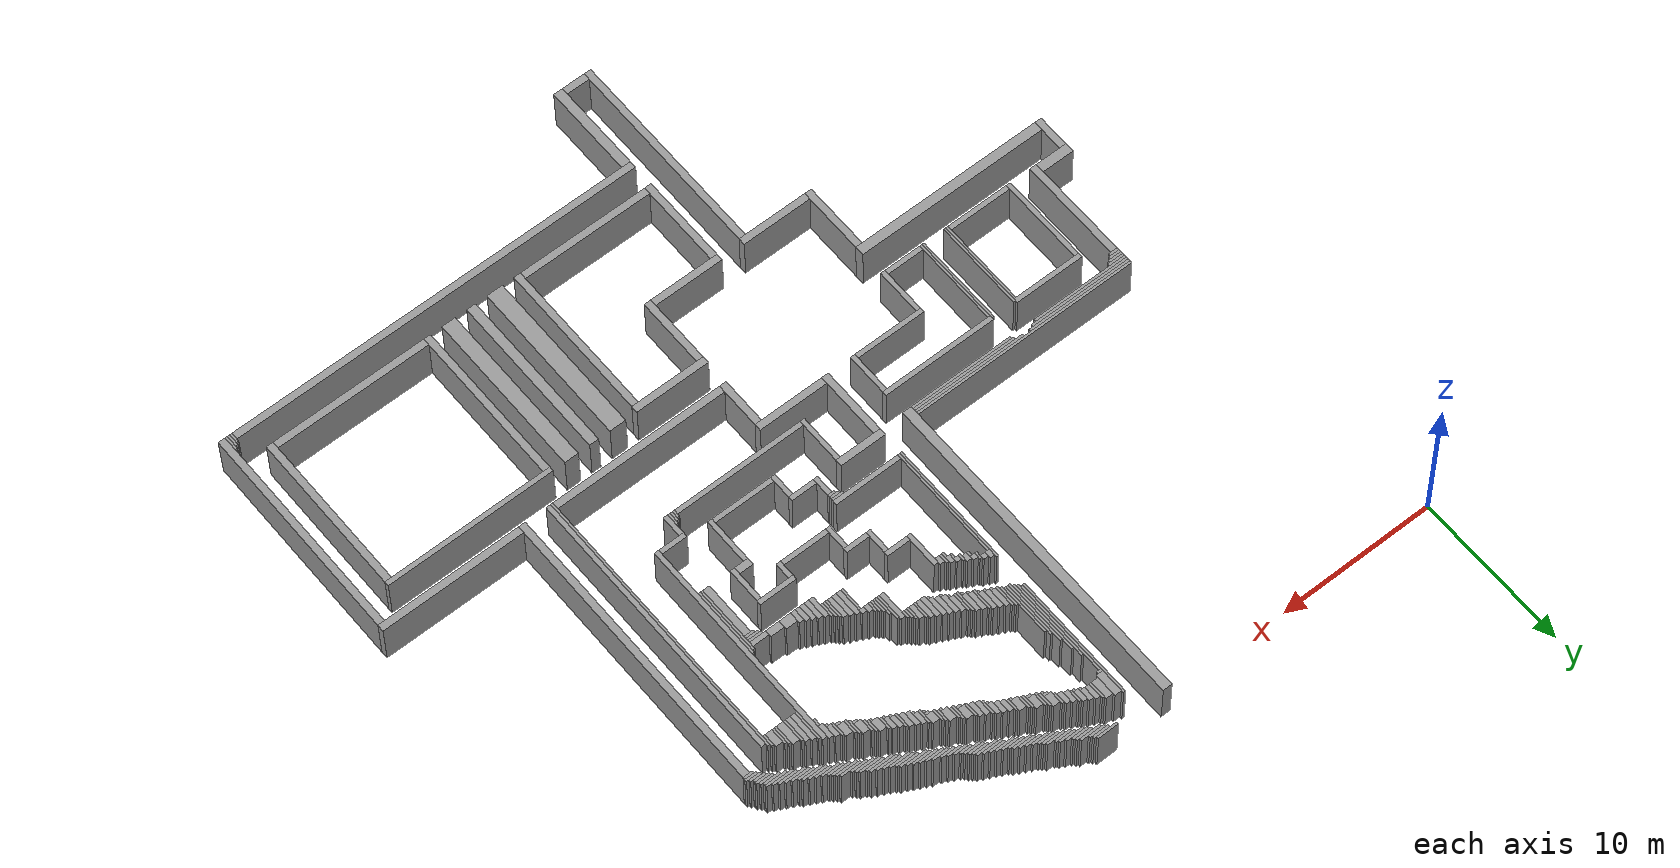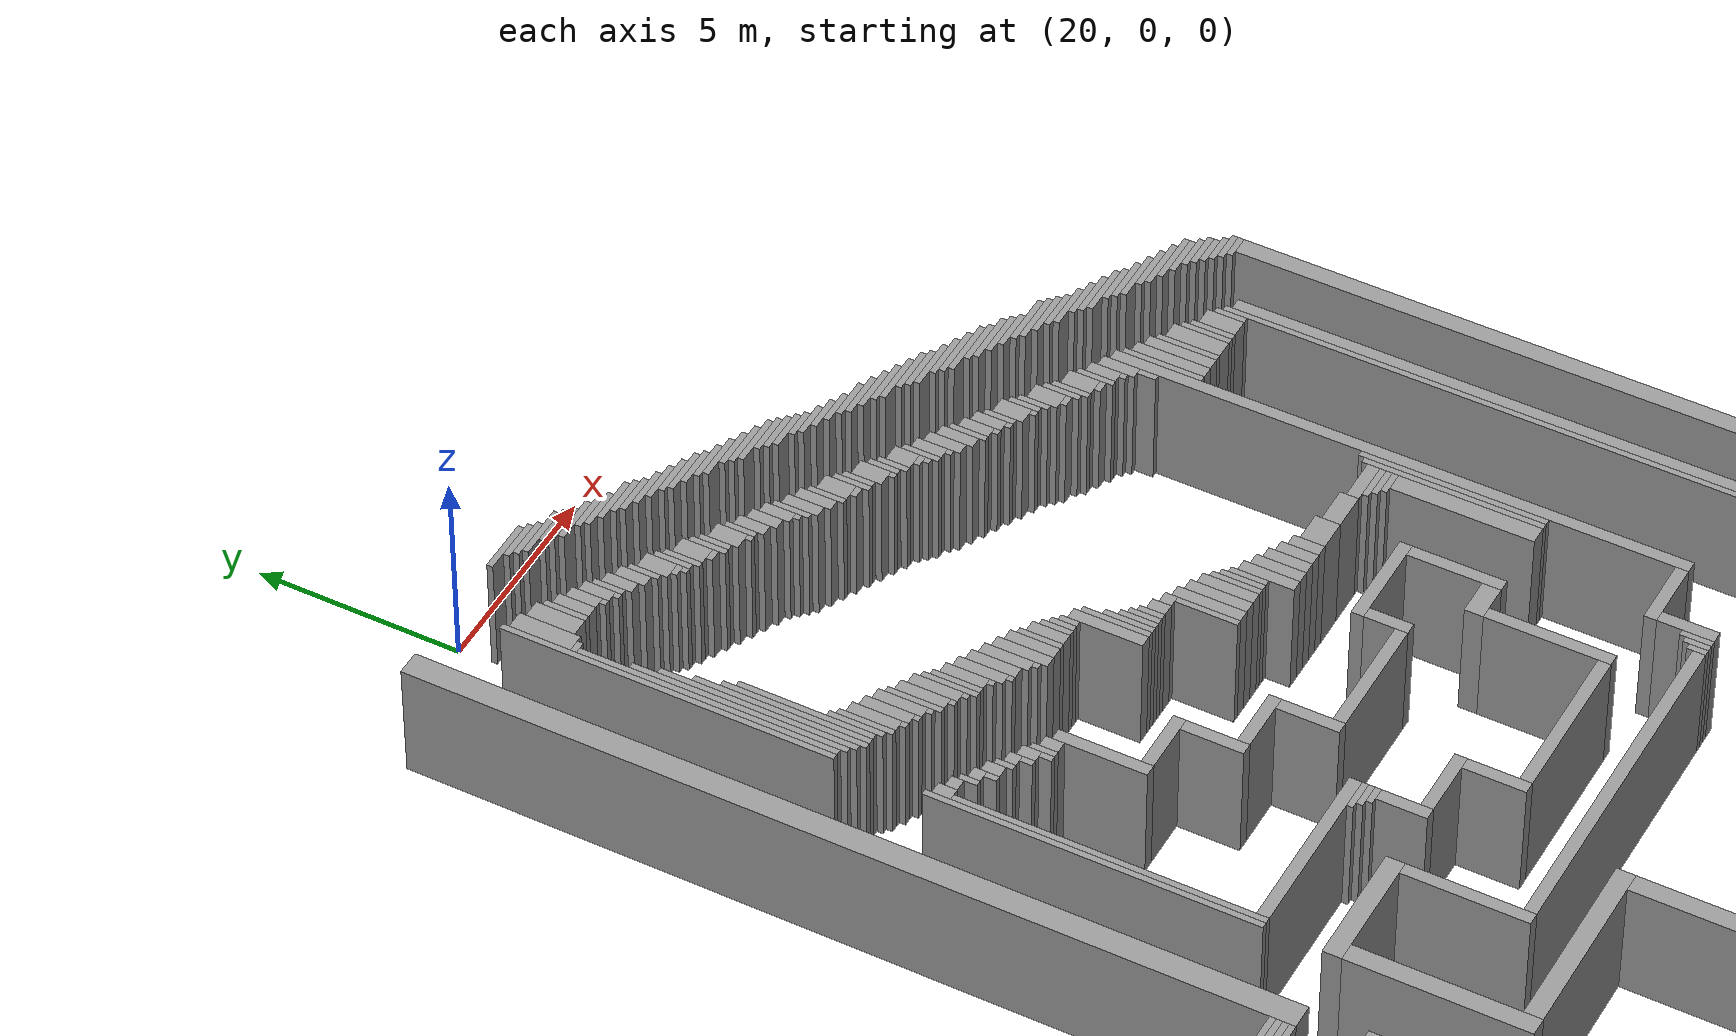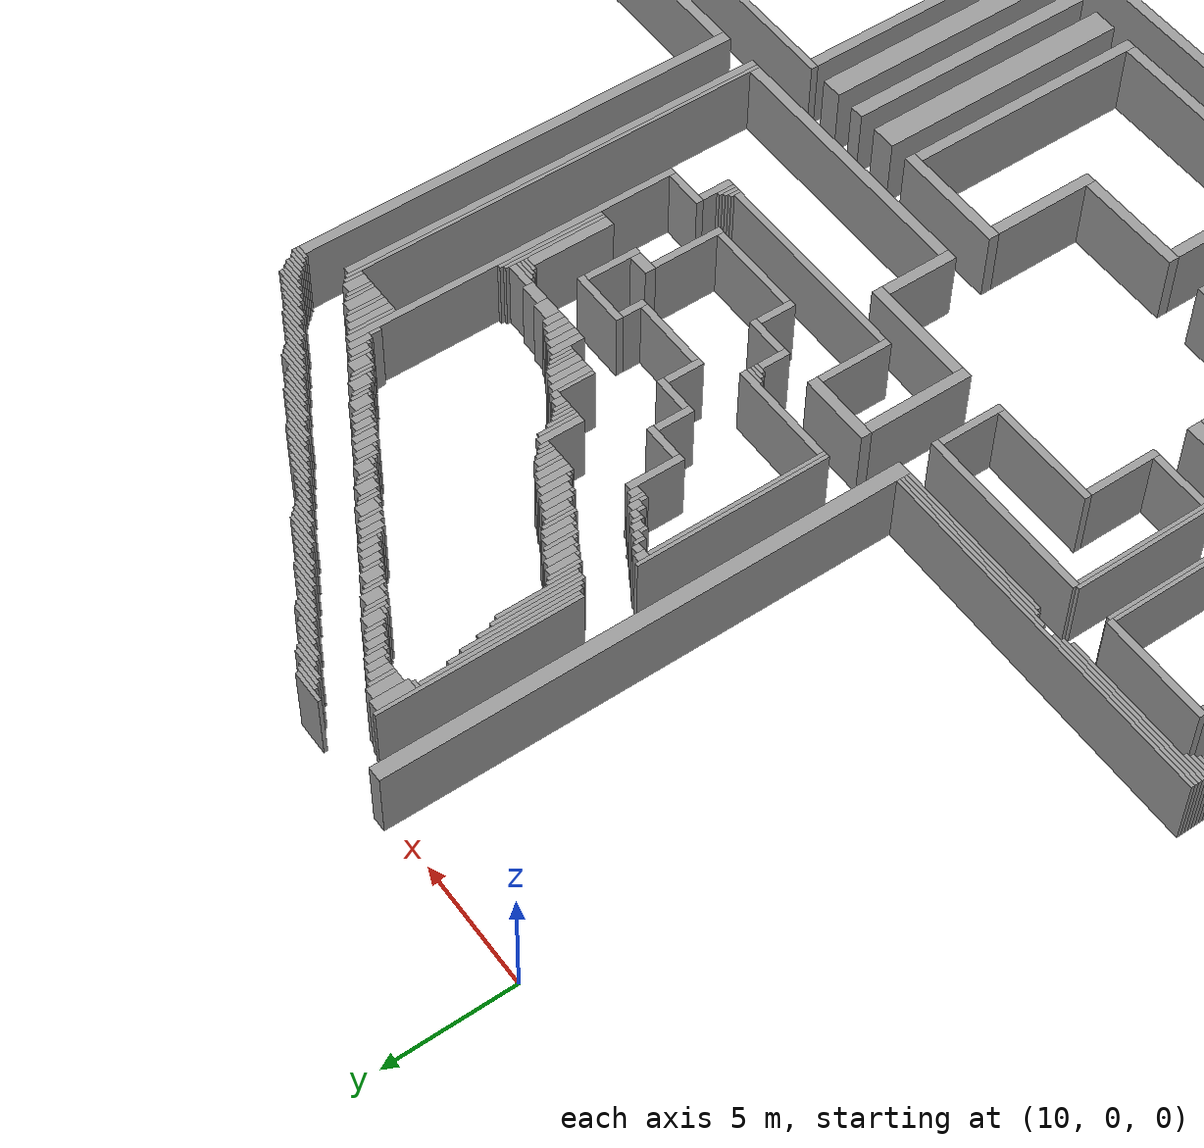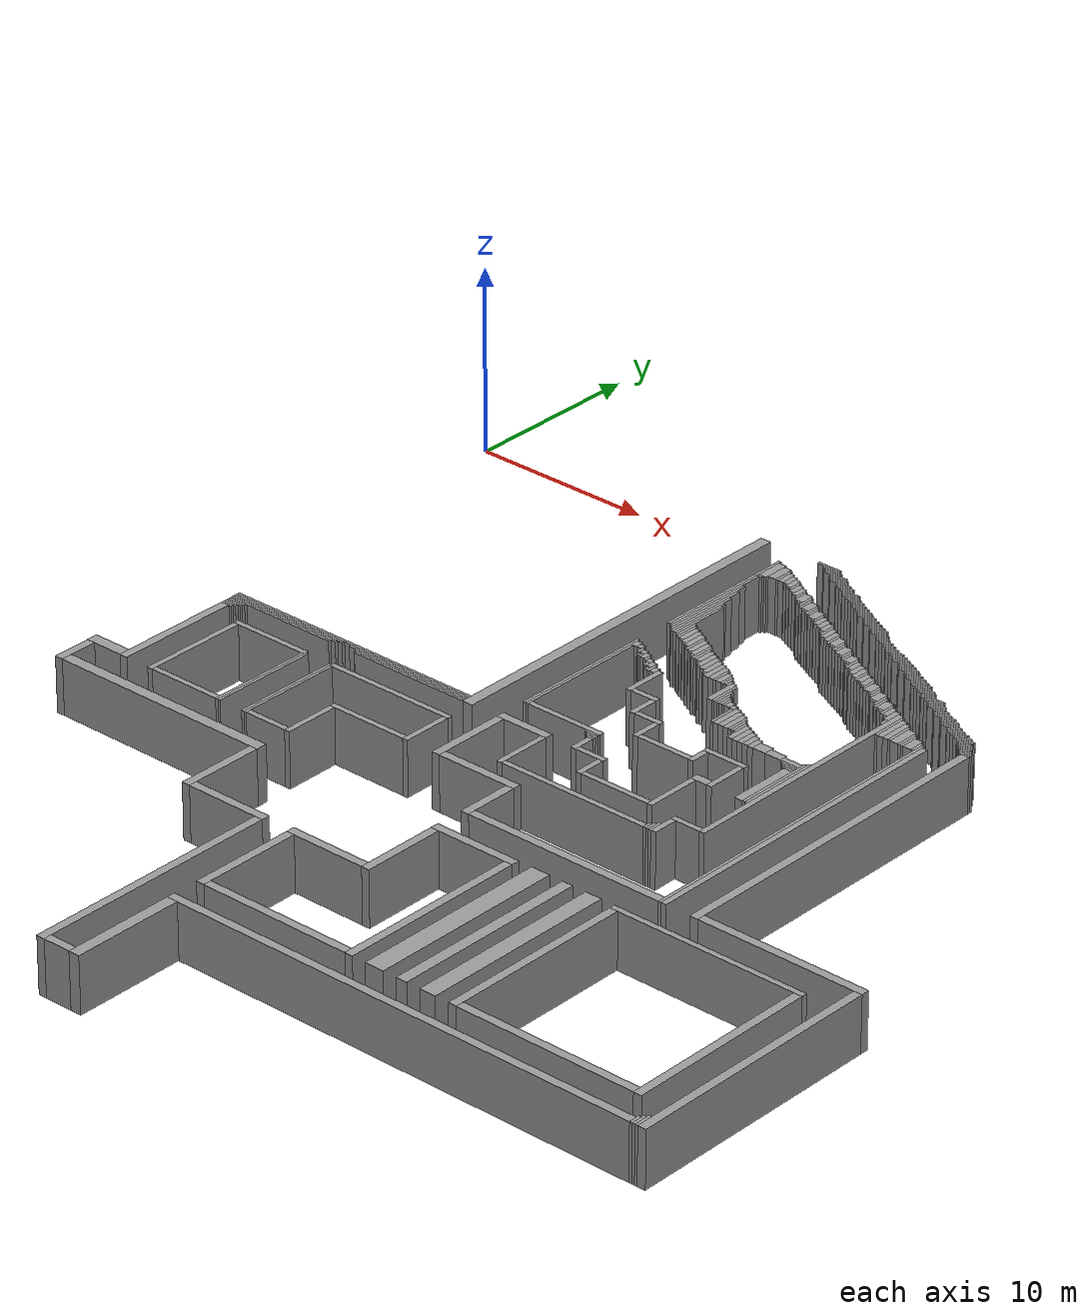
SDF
<?xml version="1.0" ?>
<sdf version="1.4">
  <model name="FunWorld1">
    <static>1</static>
    <link name="Wall_0">
      <collision name="Wall_0_Collision">
        <geometry>
          <box>
            <size>0.60000 21.15000 3.00000</size>
          </box>
        </geometry>
        <pose>18.00000 -10.57500 0 0 0 0.00000</pose>
      </collision>
      <visual name="Wall_0_Visual">
        <geometry>
          <box>
            <size>0.60000 21.15000 3.00000</size>
          </box>
        </geometry>
        <material>
          <script>
            <uri>file://media/materials/scripts/gazebo.material</uri>
            <name>Gazebo/Grey</name>
          </script>
        </material>
        <pose>18.00000 -10.57500 0 0 0 0.00000</pose>
      </visual>
    </link>
    <link name="Wall_1">
      <collision name="Wall_1_Collision">
        <geometry>
          <box>
            <size>1.35000 0.15000 3.00000</size>
          </box>
        </geometry>
        <pose>21.97500 -0.07500 0 0 0 0.00000</pose>
      </collision>
      <visual name="Wall_1_Visual">
        <geometry>
          <box>
            <size>1.35000 0.15000 3.00000</size>
          </box>
        </geometry>
        <material>
          <script>
            <uri>file://media/materials/scripts/gazebo.material</uri>
            <name>Gazebo/Grey</name>
          </script>
        </material>
        <pose>21.97500 -0.07500 0 0 0 0.00000</pose>
      </visual>
    </link>
    <link name="Wall_2">
      <collision name="Wall_2_Collision">
        <geometry>
          <box>
            <size>1.05000 0.15000 3.00000</size>
          </box>
        </geometry>
        <pose>22.27500 -0.22500 0 0 0 0.00000</pose>
      </collision>
      <visual name="Wall_2_Visual">
        <geometry>
          <box>
            <size>1.05000 0.15000 3.00000</size>
          </box>
        </geometry>
        <material>
          <script>
            <uri>file://media/materials/scripts/gazebo.material</uri>
            <name>Gazebo/Grey</name>
          </script>
        </material>
        <pose>22.27500 -0.22500 0 0 0 0.00000</pose>
      </visual>
    </link>
    <link name="Wall_3">
      <collision name="Wall_3_Collision">
        <geometry>
          <box>
            <size>1.05000 0.15000 3.00000</size>
          </box>
        </geometry>
        <pose>22.42500 -0.37500 0 0 0 0.00000</pose>
      </collision>
      <visual name="Wall_3_Visual">
        <geometry>
          <box>
            <size>1.05000 0.15000 3.00000</size>
          </box>
        </geometry>
        <material>
          <script>
            <uri>file://media/materials/scripts/gazebo.material</uri>
            <name>Gazebo/Grey</name>
          </script>
        </material>
        <pose>22.42500 -0.37500 0 0 0 0.00000</pose>
      </visual>
    </link>
    <link name="Wall_4">
      <collision name="Wall_4_Collision">
        <geometry>
          <box>
            <size>1.35000 0.15000 3.00000</size>
          </box>
        </geometry>
        <pose>22.72500 -0.52500 0 0 0 0.00000</pose>
      </collision>
      <visual name="Wall_4_Visual">
        <geometry>
          <box>
            <size>1.35000 0.15000 3.00000</size>
          </box>
        </geometry>
        <material>
          <script>
            <uri>file://media/materials/scripts/gazebo.material</uri>
            <name>Gazebo/Grey</name>
          </script>
        </material>
        <pose>22.72500 -0.52500 0 0 0 0.00000</pose>
      </visual>
    </link>
    <link name="Wall_5">
      <collision name="Wall_5_Collision">
        <geometry>
          <box>
            <size>1.05000 0.15000 3.00000</size>
          </box>
        </geometry>
        <pose>23.02500 -0.67500 0 0 0 0.00000</pose>
      </collision>
      <visual name="Wall_5_Visual">
        <geometry>
          <box>
            <size>1.05000 0.15000 3.00000</size>
          </box>
        </geometry>
        <material>
          <script>
            <uri>file://media/materials/scripts/gazebo.material</uri>
            <name>Gazebo/Grey</name>
          </script>
        </material>
        <pose>23.02500 -0.67500 0 0 0 0.00000</pose>
      </visual>
    </link>
    <link name="Wall_6">
      <collision name="Wall_6_Collision">
        <geometry>
          <box>
            <size>1.05000 0.15000 3.00000</size>
          </box>
        </geometry>
        <pose>23.17500 -0.82500 0 0 0 0.00000</pose>
      </collision>
      <visual name="Wall_6_Visual">
        <geometry>
          <box>
            <size>1.05000 0.15000 3.00000</size>
          </box>
        </geometry>
        <material>
          <script>
            <uri>file://media/materials/scripts/gazebo.material</uri>
            <name>Gazebo/Grey</name>
          </script>
        </material>
        <pose>23.17500 -0.82500 0 0 0 0.00000</pose>
      </visual>
    </link>
    <link name="Wall_7">
      <collision name="Wall_7_Collision">
        <geometry>
          <box>
            <size>1.20000 0.15000 3.00000</size>
          </box>
        </geometry>
        <pose>23.40000 -0.97500 0 0 0 0.00000</pose>
      </collision>
      <visual name="Wall_7_Visual">
        <geometry>
          <box>
            <size>1.20000 0.15000 3.00000</size>
          </box>
        </geometry>
        <material>
          <script>
            <uri>file://media/materials/scripts/gazebo.material</uri>
            <name>Gazebo/Grey</name>
          </script>
        </material>
        <pose>23.40000 -0.97500 0 0 0 0.00000</pose>
      </visual>
    </link>
    <link name="Wall_8">
      <collision name="Wall_8_Collision">
        <geometry>
          <box>
            <size>1.05000 0.15000 3.00000</size>
          </box>
        </geometry>
        <pose>23.77500 -1.12500 0 0 0 0.00000</pose>
      </collision>
      <visual name="Wall_8_Visual">
        <geometry>
          <box>
            <size>1.05000 0.15000 3.00000</size>
          </box>
        </geometry>
        <material>
          <script>
            <uri>file://media/materials/scripts/gazebo.material</uri>
            <name>Gazebo/Grey</name>
          </script>
        </material>
        <pose>23.77500 -1.12500 0 0 0 0.00000</pose>
      </visual>
    </link>
    <link name="Wall_9">
      <collision name="Wall_9_Collision">
        <geometry>
          <box>
            <size>0.15000 8.10000 3.00000</size>
          </box>
        </geometry>
        <pose>19.87500 -5.25000 0 0 0 0.00000</pose>
      </collision>
      <visual name="Wall_9_Visual">
        <geometry>
          <box>
            <size>0.15000 8.10000 3.00000</size>
          </box>
        </geometry>
        <material>
          <script>
            <uri>file://media/materials/scripts/gazebo.material</uri>
            <name>Gazebo/Grey</name>
          </script>
        </material>
        <pose>19.87500 -5.25000 0 0 0 0.00000</pose>
      </visual>
    </link>
    <link name="Wall_10">
      <collision name="Wall_10_Collision">
        <geometry>
          <box>
            <size>1.05000 0.15000 3.00000</size>
          </box>
        </geometry>
        <pose>23.92500 -1.27500 0 0 0 0.00000</pose>
      </collision>
      <visual name="Wall_10_Visual">
        <geometry>
          <box>
            <size>1.05000 0.15000 3.00000</size>
          </box>
        </geometry>
        <material>
          <script>
            <uri>file://media/materials/scripts/gazebo.material</uri>
            <name>Gazebo/Grey</name>
          </script>
        </material>
        <pose>23.92500 -1.27500 0 0 0 0.00000</pose>
      </visual>
    </link>
    <link name="Wall_11">
      <collision name="Wall_11_Collision">
        <geometry>
          <box>
            <size>0.45000 1.50000 3.00000</size>
          </box>
        </geometry>
        <pose>20.17500 -2.10000 0 0 0 0.00000</pose>
      </collision>
      <visual name="Wall_11_Visual">
        <geometry>
          <box>
            <size>0.45000 1.50000 3.00000</size>
          </box>
        </geometry>
        <material>
          <script>
            <uri>file://media/materials/scripts/gazebo.material</uri>
            <name>Gazebo/Grey</name>
          </script>
        </material>
        <pose>20.17500 -2.10000 0 0 0 0.00000</pose>
      </visual>
    </link>
    <link name="Wall_12">
      <collision name="Wall_12_Collision">
        <geometry>
          <box>
            <size>1.20000 0.15000 3.00000</size>
          </box>
        </geometry>
        <pose>24.30000 -1.42500 0 0 0 0.00000</pose>
      </collision>
      <visual name="Wall_12_Visual">
        <geometry>
          <box>
            <size>1.20000 0.15000 3.00000</size>
          </box>
        </geometry>
        <material>
          <script>
            <uri>file://media/materials/scripts/gazebo.material</uri>
            <name>Gazebo/Grey</name>
          </script>
        </material>
        <pose>24.30000 -1.42500 0 0 0 0.00000</pose>
      </visual>
    </link>
    <link name="Wall_13">
      <collision name="Wall_13_Collision">
        <geometry>
          <box>
            <size>0.45000 1.20000 3.00000</size>
          </box>
        </geometry>
        <pose>20.62500 -2.10000 0 0 0 0.00000</pose>
      </collision>
      <visual name="Wall_13_Visual">
        <geometry>
          <box>
            <size>0.45000 1.20000 3.00000</size>
          </box>
        </geometry>
        <material>
          <script>
            <uri>file://media/materials/scripts/gazebo.material</uri>
            <name>Gazebo/Grey</name>
          </script>
        </material>
        <pose>20.62500 -2.10000 0 0 0 0.00000</pose>
      </visual>
    </link>
    <link name="Wall_14">
      <collision name="Wall_14_Collision">
        <geometry>
          <box>
            <size>1.05000 0.15000 3.00000</size>
          </box>
        </geometry>
        <pose>24.52500 -1.57500 0 0 0 0.00000</pose>
      </collision>
      <visual name="Wall_14_Visual">
        <geometry>
          <box>
            <size>1.05000 0.15000 3.00000</size>
          </box>
        </geometry>
        <material>
          <script>
            <uri>file://media/materials/scripts/gazebo.material</uri>
            <name>Gazebo/Grey</name>
          </script>
        </material>
        <pose>24.52500 -1.57500 0 0 0 0.00000</pose>
      </visual>
    </link>
    <link name="Wall_15">
      <collision name="Wall_15_Collision">
        <geometry>
          <box>
            <size>0.15000 1.05000 3.00000</size>
          </box>
        </geometry>
        <pose>20.92500 -2.17500 0 0 0 0.00000</pose>
      </collision>
      <visual name="Wall_15_Visual">
        <geometry>
          <box>
            <size>0.15000 1.05000 3.00000</size>
          </box>
        </geometry>
        <material>
          <script>
            <uri>file://media/materials/scripts/gazebo.material</uri>
            <name>Gazebo/Grey</name>
          </script>
        </material>
        <pose>20.92500 -2.17500 0 0 0 0.00000</pose>
      </visual>
    </link>
    <link name="Wall_16">
      <collision name="Wall_16_Collision">
        <geometry>
          <box>
            <size>1.05000 0.15000 3.00000</size>
          </box>
        </geometry>
        <pose>24.67500 -1.72500 0 0 0 0.00000</pose>
      </collision>
      <visual name="Wall_16_Visual">
        <geometry>
          <box>
            <size>1.05000 0.15000 3.00000</size>
          </box>
        </geometry>
        <material>
          <script>
            <uri>file://media/materials/scripts/gazebo.material</uri>
            <name>Gazebo/Grey</name>
          </script>
        </material>
        <pose>24.67500 -1.72500 0 0 0 0.00000</pose>
      </visual>
    </link>
    <link name="Wall_17">
      <collision name="Wall_17_Collision">
        <geometry>
          <box>
            <size>0.30000 0.90000 3.00000</size>
          </box>
        </geometry>
        <pose>21.15000 -2.25000 0 0 0 0.00000</pose>
      </collision>
      <visual name="Wall_17_Visual">
        <geometry>
          <box>
            <size>0.30000 0.90000 3.00000</size>
          </box>
        </geometry>
        <material>
          <script>
            <uri>file://media/materials/scripts/gazebo.material</uri>
            <name>Gazebo/Grey</name>
          </script>
        </material>
        <pose>21.15000 -2.25000 0 0 0 0.00000</pose>
      </visual>
    </link>
    <link name="Wall_18">
      <collision name="Wall_18_Collision">
        <geometry>
          <box>
            <size>1.05000 0.15000 3.00000</size>
          </box>
        </geometry>
        <pose>24.97500 -1.87500 0 0 0 0.00000</pose>
      </collision>
      <visual name="Wall_18_Visual">
        <geometry>
          <box>
            <size>1.05000 0.15000 3.00000</size>
          </box>
        </geometry>
        <material>
          <script>
            <uri>file://media/materials/scripts/gazebo.material</uri>
            <name>Gazebo/Grey</name>
          </script>
        </material>
        <pose>24.97500 -1.87500 0 0 0 0.00000</pose>
      </visual>
    </link>
    <link name="Wall_19">
      <collision name="Wall_19_Collision">
        <geometry>
          <box>
            <size>0.30000 0.75000 3.00000</size>
          </box>
        </geometry>
        <pose>21.45000 -2.32500 0 0 0 0.00000</pose>
      </collision>
      <visual name="Wall_19_Visual">
        <geometry>
          <box>
            <size>0.30000 0.75000 3.00000</size>
          </box>
        </geometry>
        <material>
          <script>
            <uri>file://media/materials/scripts/gazebo.material</uri>
            <name>Gazebo/Grey</name>
          </script>
        </material>
        <pose>21.45000 -2.32500 0 0 0 0.00000</pose>
      </visual>
    </link>
    <link name="Wall_20">
      <collision name="Wall_20_Collision">
        <geometry>
          <box>
            <size>1.05000 0.15000 3.00000</size>
          </box>
        </geometry>
        <pose>25.27500 -2.02500 0 0 0 0.00000</pose>
      </collision>
      <visual name="Wall_20_Visual">
        <geometry>
          <box>
            <size>1.05000 0.15000 3.00000</size>
          </box>
        </geometry>
        <material>
          <script>
            <uri>file://media/materials/scripts/gazebo.material</uri>
            <name>Gazebo/Grey</name>
          </script>
        </material>
        <pose>25.27500 -2.02500 0 0 0 0.00000</pose>
      </visual>
    </link>
    <link name="Wall_21">
      <collision name="Wall_21_Collision">
        <geometry>
          <box>
            <size>0.30000 0.75000 3.00000</size>
          </box>
        </geometry>
        <pose>21.75000 -2.47500 0 0 0 0.00000</pose>
      </collision>
      <visual name="Wall_21_Visual">
        <geometry>
          <box>
            <size>0.30000 0.75000 3.00000</size>
          </box>
        </geometry>
        <material>
          <script>
            <uri>file://media/materials/scripts/gazebo.material</uri>
            <name>Gazebo/Grey</name>
          </script>
        </material>
        <pose>21.75000 -2.47500 0 0 0 0.00000</pose>
      </visual>
    </link>
    <link name="Wall_22">
      <collision name="Wall_22_Collision">
        <geometry>
          <box>
            <size>1.05000 0.15000 3.00000</size>
          </box>
        </geometry>
        <pose>25.57500 -2.17500 0 0 0 0.00000</pose>
      </collision>
      <visual name="Wall_22_Visual">
        <geometry>
          <box>
            <size>1.05000 0.15000 3.00000</size>
          </box>
        </geometry>
        <material>
          <script>
            <uri>file://media/materials/scripts/gazebo.material</uri>
            <name>Gazebo/Grey</name>
          </script>
        </material>
        <pose>25.57500 -2.17500 0 0 0 0.00000</pose>
      </visual>
    </link>
    <link name="Wall_23">
      <collision name="Wall_23_Collision">
        <geometry>
          <box>
            <size>0.15000 0.75000 3.00000</size>
          </box>
        </geometry>
        <pose>21.97500 -2.62500 0 0 0 0.00000</pose>
      </collision>
      <visual name="Wall_23_Visual">
        <geometry>
          <box>
            <size>0.15000 0.75000 3.00000</size>
          </box>
        </geometry>
        <material>
          <script>
            <uri>file://media/materials/scripts/gazebo.material</uri>
            <name>Gazebo/Grey</name>
          </script>
        </material>
        <pose>21.97500 -2.62500 0 0 0 0.00000</pose>
      </visual>
    </link>
    <link name="Wall_24">
      <collision name="Wall_24_Collision">
        <geometry>
          <box>
            <size>1.20000 0.15000 3.00000</size>
          </box>
        </geometry>
        <pose>25.80000 -2.32500 0 0 0 0.00000</pose>
      </collision>
      <visual name="Wall_24_Visual">
        <geometry>
          <box>
            <size>1.20000 0.15000 3.00000</size>
          </box>
        </geometry>
        <material>
          <script>
            <uri>file://media/materials/scripts/gazebo.material</uri>
            <name>Gazebo/Grey</name>
          </script>
        </material>
        <pose>25.80000 -2.32500 0 0 0 0.00000</pose>
      </visual>
    </link>
    <link name="Wall_25">
      <collision name="Wall_25_Collision">
        <geometry>
          <box>
            <size>0.30000 0.75000 3.00000</size>
          </box>
        </geometry>
        <pose>22.20000 -2.77500 0 0 0 0.00000</pose>
      </collision>
      <visual name="Wall_25_Visual">
        <geometry>
          <box>
            <size>0.30000 0.75000 3.00000</size>
          </box>
        </geometry>
        <material>
          <script>
            <uri>file://media/materials/scripts/gazebo.material</uri>
            <name>Gazebo/Grey</name>
          </script>
        </material>
        <pose>22.20000 -2.77500 0 0 0 0.00000</pose>
      </visual>
    </link>
    <link name="Wall_26">
      <collision name="Wall_26_Collision">
        <geometry>
          <box>
            <size>1.05000 0.15000 3.00000</size>
          </box>
        </geometry>
        <pose>26.02500 -2.47500 0 0 0 0.00000</pose>
      </collision>
      <visual name="Wall_26_Visual">
        <geometry>
          <box>
            <size>1.05000 0.15000 3.00000</size>
          </box>
        </geometry>
        <material>
          <script>
            <uri>file://media/materials/scripts/gazebo.material</uri>
            <name>Gazebo/Grey</name>
          </script>
        </material>
        <pose>26.02500 -2.47500 0 0 0 0.00000</pose>
      </visual>
    </link>
    <link name="Wall_27">
      <collision name="Wall_27_Collision">
        <geometry>
          <box>
            <size>0.30000 0.75000 3.00000</size>
          </box>
        </geometry>
        <pose>22.50000 -2.92500 0 0 0 0.00000</pose>
      </collision>
      <visual name="Wall_27_Visual">
        <geometry>
          <box>
            <size>0.30000 0.75000 3.00000</size>
          </box>
        </geometry>
        <material>
          <script>
            <uri>file://media/materials/scripts/gazebo.material</uri>
            <name>Gazebo/Grey</name>
          </script>
        </material>
        <pose>22.50000 -2.92500 0 0 0 0.00000</pose>
      </visual>
    </link>
    <link name="Wall_28">
      <collision name="Wall_28_Collision">
        <geometry>
          <box>
            <size>1.05000 0.15000 3.00000</size>
          </box>
        </geometry>
        <pose>26.32500 -2.62500 0 0 0 0.00000</pose>
      </collision>
      <visual name="Wall_28_Visual">
        <geometry>
          <box>
            <size>1.05000 0.15000 3.00000</size>
          </box>
        </geometry>
        <material>
          <script>
            <uri>file://media/materials/scripts/gazebo.material</uri>
            <name>Gazebo/Grey</name>
          </script>
        </material>
        <pose>26.32500 -2.62500 0 0 0 0.00000</pose>
      </visual>
    </link>
    <link name="Wall_29">
      <collision name="Wall_29_Collision">
        <geometry>
          <box>
            <size>0.15000 0.15000 3.00000</size>
          </box>
        </geometry>
        <pose>21.52500 -2.77500 0 0 0 0.00000</pose>
      </collision>
      <visual name="Wall_29_Visual">
        <geometry>
          <box>
            <size>0.15000 0.15000 3.00000</size>
          </box>
        </geometry>
        <material>
          <script>
            <uri>file://media/materials/scripts/gazebo.material</uri>
            <name>Gazebo/Grey</name>
          </script>
        </material>
        <pose>21.52500 -2.77500 0 0 0 0.00000</pose>
      </visual>
    </link>
    <link name="Wall_30">
      <collision name="Wall_30_Collision">
        <geometry>
          <box>
            <size>0.15000 0.75000 3.00000</size>
          </box>
        </geometry>
        <pose>22.72500 -3.07500 0 0 0 0.00000</pose>
      </collision>
      <visual name="Wall_30_Visual">
        <geometry>
          <box>
            <size>0.15000 0.75000 3.00000</size>
          </box>
        </geometry>
        <material>
          <script>
            <uri>file://media/materials/scripts/gazebo.material</uri>
            <name>Gazebo/Grey</name>
          </script>
        </material>
        <pose>22.72500 -3.07500 0 0 0 0.00000</pose>
      </visual>
    </link>
    <link name="Wall_31">
      <collision name="Wall_31_Collision">
        <geometry>
          <box>
            <size>1.20000 0.15000 3.00000</size>
          </box>
        </geometry>
        <pose>26.55000 -2.77500 0 0 0 0.00000</pose>
      </collision>
      <visual name="Wall_31_Visual">
        <geometry>
          <box>
            <size>1.20000 0.15000 3.00000</size>
          </box>
        </geometry>
        <material>
          <script>
            <uri>file://media/materials/scripts/gazebo.material</uri>
            <name>Gazebo/Grey</name>
          </script>
        </material>
        <pose>26.55000 -2.77500 0 0 0 0.00000</pose>
      </visual>
    </link>
    <link name="Wall_32">
      <collision name="Wall_32_Collision">
        <geometry>
          <box>
            <size>0.30000 0.15000 3.00000</size>
          </box>
        </geometry>
        <pose>20.10000 -2.92500 0 0 0 0.00000</pose>
      </collision>
      <visual name="Wall_32_Visual">
        <geometry>
          <box>
            <size>0.30000 0.15000 3.00000</size>
          </box>
        </geometry>
        <material>
          <script>
            <uri>file://media/materials/scripts/gazebo.material</uri>
            <name>Gazebo/Grey</name>
          </script>
        </material>
        <pose>20.10000 -2.92500 0 0 0 0.00000</pose>
      </visual>
    </link>
    <link name="Wall_33">
      <collision name="Wall_33_Collision">
        <geometry>
          <box>
            <size>0.15000 0.15000 3.00000</size>
          </box>
        </geometry>
        <pose>21.82500 -2.92500 0 0 0 0.00000</pose>
      </collision>
      <visual name="Wall_33_Visual">
        <geometry>
          <box>
            <size>0.15000 0.15000 3.00000</size>
          </box>
        </geometry>
        <material>
          <script>
            <uri>file://media/materials/scripts/gazebo.material</uri>
            <name>Gazebo/Grey</name>
          </script>
        </material>
        <pose>21.82500 -2.92500 0 0 0 0.00000</pose>
      </visual>
    </link>
    <link name="Wall_34">
      <collision name="Wall_34_Collision">
        <geometry>
          <box>
            <size>0.45000 0.75000 3.00000</size>
          </box>
        </geometry>
        <pose>23.02500 -3.22500 0 0 0 0.00000</pose>
      </collision>
      <visual name="Wall_34_Visual">
        <geometry>
          <box>
            <size>0.45000 0.75000 3.00000</size>
          </box>
        </geometry>
        <material>
          <script>
            <uri>file://media/materials/scripts/gazebo.material</uri>
            <name>Gazebo/Grey</name>
          </script>
        </material>
        <pose>23.02500 -3.22500 0 0 0 0.00000</pose>
      </visual>
    </link>
    <link name="Wall_35">
      <collision name="Wall_35_Collision">
        <geometry>
          <box>
            <size>1.05000 0.15000 3.00000</size>
          </box>
        </geometry>
        <pose>26.92500 -2.92500 0 0 0 0.00000</pose>
      </collision>
      <visual name="Wall_35_Visual">
        <geometry>
          <box>
            <size>1.05000 0.15000 3.00000</size>
          </box>
        </geometry>
        <material>
          <script>
            <uri>file://media/materials/scripts/gazebo.material</uri>
            <name>Gazebo/Grey</name>
          </script>
        </material>
        <pose>26.92500 -2.92500 0 0 0 0.00000</pose>
      </visual>
    </link>
    <link name="Wall_36">
      <collision name="Wall_36_Collision">
        <geometry>
          <box>
            <size>0.15000 6.30000 3.00000</size>
          </box>
        </geometry>
        <pose>20.02500 -6.15000 0 0 0 0.00000</pose>
      </collision>
      <visual name="Wall_36_Visual">
        <geometry>
          <box>
            <size>0.15000 6.30000 3.00000</size>
          </box>
        </geometry>
        <material>
          <script>
            <uri>file://media/materials/scripts/gazebo.material</uri>
            <name>Gazebo/Grey</name>
          </script>
        </material>
        <pose>20.02500 -6.15000 0 0 0 0.00000</pose>
      </visual>
    </link>
    <link name="Wall_37">
      <collision name="Wall_37_Collision">
        <geometry>
          <box>
            <size>0.15000 0.90000 3.00000</size>
          </box>
        </geometry>
        <pose>23.32500 -3.45000 0 0 0 0.00000</pose>
      </collision>
      <visual name="Wall_37_Visual">
        <geometry>
          <box>
            <size>0.15000 0.90000 3.00000</size>
          </box>
        </geometry>
        <material>
          <script>
            <uri>file://media/materials/scripts/gazebo.material</uri>
            <name>Gazebo/Grey</name>
          </script>
        </material>
        <pose>23.32500 -3.45000 0 0 0 0.00000</pose>
      </visual>
    </link>
    <link name="Wall_38">
      <collision name="Wall_38_Collision">
        <geometry>
          <box>
            <size>1.20000 0.15000 3.00000</size>
          </box>
        </geometry>
        <pose>27.15000 -3.07500 0 0 0 0.00000</pose>
      </collision>
      <visual name="Wall_38_Visual">
        <geometry>
          <box>
            <size>1.20000 0.15000 3.00000</size>
          </box>
        </geometry>
        <material>
          <script>
            <uri>file://media/materials/scripts/gazebo.material</uri>
            <name>Gazebo/Grey</name>
          </script>
        </material>
        <pose>27.15000 -3.07500 0 0 0 0.00000</pose>
      </visual>
    </link>
    <link name="Wall_39">
      <collision name="Wall_39_Collision">
        <geometry>
          <box>
            <size>0.15000 0.90000 3.00000</size>
          </box>
        </geometry>
        <pose>23.47500 -3.60000 0 0 0 0.00000</pose>
      </collision>
      <visual name="Wall_39_Visual">
        <geometry>
          <box>
            <size>0.15000 0.90000 3.00000</size>
          </box>
        </geometry>
        <material>
          <script>
            <uri>file://media/materials/scripts/gazebo.material</uri>
            <name>Gazebo/Grey</name>
          </script>
        </material>
        <pose>23.47500 -3.60000 0 0 0 0.00000</pose>
      </visual>
    </link>
    <link name="Wall_40">
      <collision name="Wall_40_Collision">
        <geometry>
          <box>
            <size>1.35000 0.15000 3.00000</size>
          </box>
        </geometry>
        <pose>27.37500 -3.22500 0 0 0 0.00000</pose>
      </collision>
      <visual name="Wall_40_Visual">
        <geometry>
          <box>
            <size>1.35000 0.15000 3.00000</size>
          </box>
        </geometry>
        <material>
          <script>
            <uri>file://media/materials/scripts/gazebo.material</uri>
            <name>Gazebo/Grey</name>
          </script>
        </material>
        <pose>27.37500 -3.22500 0 0 0 0.00000</pose>
      </visual>
    </link>
    <link name="Wall_41">
      <collision name="Wall_41_Collision">
        <geometry>
          <box>
            <size>0.45000 0.75000 3.00000</size>
          </box>
        </geometry>
        <pose>23.77500 -3.67500 0 0 0 0.00000</pose>
      </collision>
      <visual name="Wall_41_Visual">
        <geometry>
          <box>
            <size>0.45000 0.75000 3.00000</size>
          </box>
        </geometry>
        <material>
          <script>
            <uri>file://media/materials/scripts/gazebo.material</uri>
            <name>Gazebo/Grey</name>
          </script>
        </material>
        <pose>23.77500 -3.67500 0 0 0 0.00000</pose>
      </visual>
    </link>
    <link name="Wall_42">
      <collision name="Wall_42_Collision">
        <geometry>
          <box>
            <size>1.05000 0.15000 3.00000</size>
          </box>
        </geometry>
        <pose>27.67500 -3.37500 0 0 0 0.00000</pose>
      </collision>
      <visual name="Wall_42_Visual">
        <geometry>
          <box>
            <size>1.05000 0.15000 3.00000</size>
          </box>
        </geometry>
        <material>
          <script>
            <uri>file://media/materials/scripts/gazebo.material</uri>
            <name>Gazebo/Grey</name>
          </script>
        </material>
        <pose>27.67500 -3.37500 0 0 0 0.00000</pose>
      </visual>
    </link>
    <link name="Wall_43">
      <collision name="Wall_43_Collision">
        <geometry>
          <box>
            <size>0.15000 0.90000 3.00000</size>
          </box>
        </geometry>
        <pose>24.07500 -3.90000 0 0 0 0.00000</pose>
      </collision>
      <visual name="Wall_43_Visual">
        <geometry>
          <box>
            <size>0.15000 0.90000 3.00000</size>
          </box>
        </geometry>
        <material>
          <script>
            <uri>file://media/materials/scripts/gazebo.material</uri>
            <name>Gazebo/Grey</name>
          </script>
        </material>
        <pose>24.07500 -3.90000 0 0 0 0.00000</pose>
      </visual>
    </link>
    <link name="Wall_44">
      <collision name="Wall_44_Collision">
        <geometry>
          <box>
            <size>1.05000 0.15000 3.00000</size>
          </box>
        </geometry>
        <pose>27.82500 -3.52500 0 0 0 0.00000</pose>
      </collision>
      <visual name="Wall_44_Visual">
        <geometry>
          <box>
            <size>1.05000 0.15000 3.00000</size>
          </box>
        </geometry>
        <material>
          <script>
            <uri>file://media/materials/scripts/gazebo.material</uri>
            <name>Gazebo/Grey</name>
          </script>
        </material>
        <pose>27.82500 -3.52500 0 0 0 0.00000</pose>
      </visual>
    </link>
    <link name="Wall_45">
      <collision name="Wall_45_Collision">
        <geometry>
          <box>
            <size>0.30000 0.15000 3.00000</size>
          </box>
        </geometry>
        <pose>23.10000 -3.67500 0 0 0 0.00000</pose>
      </collision>
      <visual name="Wall_45_Visual">
        <geometry>
          <box>
            <size>0.30000 0.15000 3.00000</size>
          </box>
        </geometry>
        <material>
          <script>
            <uri>file://media/materials/scripts/gazebo.material</uri>
            <name>Gazebo/Grey</name>
          </script>
        </material>
        <pose>23.10000 -3.67500 0 0 0 0.00000</pose>
      </visual>
    </link>
    <link name="Wall_46">
      <collision name="Wall_46_Collision">
        <geometry>
          <box>
            <size>0.15000 0.75000 3.00000</size>
          </box>
        </geometry>
        <pose>24.22500 -3.97500 0 0 0 0.00000</pose>
      </collision>
      <visual name="Wall_46_Visual">
        <geometry>
          <box>
            <size>0.15000 0.75000 3.00000</size>
          </box>
        </geometry>
        <material>
          <script>
            <uri>file://media/materials/scripts/gazebo.material</uri>
            <name>Gazebo/Grey</name>
          </script>
        </material>
        <pose>24.22500 -3.97500 0 0 0 0.00000</pose>
      </visual>
    </link>
    <link name="Wall_47">
      <collision name="Wall_47_Collision">
        <geometry>
          <box>
            <size>1.05000 0.15000 3.00000</size>
          </box>
        </geometry>
        <pose>27.97500 -3.67500 0 0 0 0.00000</pose>
      </collision>
      <visual name="Wall_47_Visual">
        <geometry>
          <box>
            <size>1.05000 0.15000 3.00000</size>
          </box>
        </geometry>
        <material>
          <script>
            <uri>file://media/materials/scripts/gazebo.material</uri>
            <name>Gazebo/Grey</name>
          </script>
        </material>
        <pose>27.97500 -3.67500 0 0 0 0.00000</pose>
      </visual>
    </link>
    <link name="Wall_48">
      <collision name="Wall_48_Collision">
        <geometry>
          <box>
            <size>0.15000 0.15000 3.00000</size>
          </box>
        </geometry>
        <pose>23.17500 -3.82500 0 0 0 0.00000</pose>
      </collision>
      <visual name="Wall_48_Visual">
        <geometry>
          <box>
            <size>0.15000 0.15000 3.00000</size>
          </box>
        </geometry>
        <material>
          <script>
            <uri>file://media/materials/scripts/gazebo.material</uri>
            <name>Gazebo/Grey</name>
          </script>
        </material>
        <pose>23.17500 -3.82500 0 0 0 0.00000</pose>
      </visual>
    </link>
    <link name="Wall_49">
      <collision name="Wall_49_Collision">
        <geometry>
          <box>
            <size>0.45000 0.75000 3.00000</size>
          </box>
        </geometry>
        <pose>24.52500 -4.12500 0 0 0 0.00000</pose>
      </collision>
      <visual name="Wall_49_Visual">
        <geometry>
          <box>
            <size>0.45000 0.75000 3.00000</size>
          </box>
        </geometry>
        <material>
          <script>
            <uri>file://media/materials/scripts/gazebo.material</uri>
            <name>Gazebo/Grey</name>
          </script>
        </material>
        <pose>24.52500 -4.12500 0 0 0 0.00000</pose>
      </visual>
    </link>
    <link name="Wall_50">
      <collision name="Wall_50_Collision">
        <geometry>
          <box>
            <size>0.75000 0.15000 3.00000</size>
          </box>
        </geometry>
        <pose>28.27500 -3.82500 0 0 0 0.00000</pose>
      </collision>
      <visual name="Wall_50_Visual">
        <geometry>
          <box>
            <size>0.75000 0.15000 3.00000</size>
          </box>
        </geometry>
        <material>
          <script>
            <uri>file://media/materials/scripts/gazebo.material</uri>
            <name>Gazebo/Grey</name>
          </script>
        </material>
        <pose>28.27500 -3.82500 0 0 0 0.00000</pose>
      </visual>
    </link>
    <link name="Wall_51">
      <collision name="Wall_51_Collision">
        <geometry>
          <box>
            <size>0.15000 0.75000 3.00000</size>
          </box>
        </geometry>
        <pose>24.82500 -4.27500 0 0 0 0.00000</pose>
      </collision>
      <visual name="Wall_51_Visual">
        <geometry>
          <box>
            <size>0.15000 0.75000 3.00000</size>
          </box>
        </geometry>
        <material>
          <script>
            <uri>file://media/materials/scripts/gazebo.material</uri>
            <name>Gazebo/Grey</name>
          </script>
        </material>
        <pose>24.82500 -4.27500 0 0 0 0.00000</pose>
      </visual>
    </link>
    <link name="Wall_52">
      <collision name="Wall_52_Collision">
        <geometry>
          <box>
            <size>0.90000 0.15000 3.00000</size>
          </box>
        </geometry>
        <pose>28.50000 -3.97500 0 0 0 0.00000</pose>
      </collision>
      <visual name="Wall_52_Visual">
        <geometry>
          <box>
            <size>0.90000 0.15000 3.00000</size>
          </box>
        </geometry>
        <material>
          <script>
            <uri>file://media/materials/scripts/gazebo.material</uri>
            <name>Gazebo/Grey</name>
          </script>
        </material>
        <pose>28.50000 -3.97500 0 0 0 0.00000</pose>
      </visual>
    </link>
    <link name="Wall_53">
      <collision name="Wall_53_Collision">
        <geometry>
          <box>
            <size>0.30000 0.15000 3.00000</size>
          </box>
        </geometry>
        <pose>23.85000 -4.12500 0 0 0 0.00000</pose>
      </collision>
      <visual name="Wall_53_Visual">
        <geometry>
          <box>
            <size>0.30000 0.15000 3.00000</size>
          </box>
        </geometry>
        <material>
          <script>
            <uri>file://media/materials/scripts/gazebo.material</uri>
            <name>Gazebo/Grey</name>
          </script>
        </material>
        <pose>23.85000 -4.12500 0 0 0 0.00000</pose>
      </visual>
    </link>
    <link name="Wall_54">
      <collision name="Wall_54_Collision">
        <geometry>
          <box>
            <size>0.30000 0.75000 3.00000</size>
          </box>
        </geometry>
        <pose>25.05000 -4.42500 0 0 0 0.00000</pose>
      </collision>
      <visual name="Wall_54_Visual">
        <geometry>
          <box>
            <size>0.30000 0.75000 3.00000</size>
          </box>
        </geometry>
        <material>
          <script>
            <uri>file://media/materials/scripts/gazebo.material</uri>
            <name>Gazebo/Grey</name>
          </script>
        </material>
        <pose>25.05000 -4.42500 0 0 0 0.00000</pose>
      </visual>
    </link>
    <link name="Wall_55">
      <collision name="Wall_55_Collision">
        <geometry>
          <box>
            <size>0.90000 0.15000 3.00000</size>
          </box>
        </geometry>
        <pose>28.80000 -4.12500 0 0 0 0.00000</pose>
      </collision>
      <visual name="Wall_55_Visual">
        <geometry>
          <box>
            <size>0.90000 0.15000 3.00000</size>
          </box>
        </geometry>
        <material>
          <script>
            <uri>file://media/materials/scripts/gazebo.material</uri>
            <name>Gazebo/Grey</name>
          </script>
        </material>
        <pose>28.80000 -4.12500 0 0 0 0.00000</pose>
      </visual>
    </link>
    <link name="Wall_56">
      <collision name="Wall_56_Collision">
        <geometry>
          <box>
            <size>0.15000 5.25000 3.00000</size>
          </box>
        </geometry>
        <pose>20.17500 -6.82500 0 0 0 0.00000</pose>
      </collision>
      <visual name="Wall_56_Visual">
        <geometry>
          <box>
            <size>0.15000 5.25000 3.00000</size>
          </box>
        </geometry>
        <material>
          <script>
            <uri>file://media/materials/scripts/gazebo.material</uri>
            <name>Gazebo/Grey</name>
          </script>
        </material>
        <pose>20.17500 -6.82500 0 0 0 0.00000</pose>
      </visual>
    </link>
    <link name="Wall_57">
      <collision name="Wall_57_Collision">
        <geometry>
          <box>
            <size>0.30000 0.75000 3.00000</size>
          </box>
        </geometry>
        <pose>25.35000 -4.57500 0 0 0 0.00000</pose>
      </collision>
      <visual name="Wall_57_Visual">
        <geometry>
          <box>
            <size>0.30000 0.75000 3.00000</size>
          </box>
        </geometry>
        <material>
          <script>
            <uri>file://media/materials/scripts/gazebo.material</uri>
            <name>Gazebo/Grey</name>
          </script>
        </material>
        <pose>25.35000 -4.57500 0 0 0 0.00000</pose>
      </visual>
    </link>
    <link name="Wall_58">
      <collision name="Wall_58_Collision">
        <geometry>
          <box>
            <size>0.90000 0.15000 3.00000</size>
          </box>
        </geometry>
        <pose>29.10000 -4.27500 0 0 0 0.00000</pose>
      </collision>
      <visual name="Wall_58_Visual">
        <geometry>
          <box>
            <size>0.90000 0.15000 3.00000</size>
          </box>
        </geometry>
        <material>
          <script>
            <uri>file://media/materials/scripts/gazebo.material</uri>
            <name>Gazebo/Grey</name>
          </script>
        </material>
        <pose>29.10000 -4.27500 0 0 0 0.00000</pose>
      </visual>
    </link>
    <link name="Wall_59">
      <collision name="Wall_59_Collision">
        <geometry>
          <box>
            <size>0.30000 0.75000 3.00000</size>
          </box>
        </geometry>
        <pose>25.65000 -4.72500 0 0 0 0.00000</pose>
      </collision>
      <visual name="Wall_59_Visual">
        <geometry>
          <box>
            <size>0.30000 0.75000 3.00000</size>
          </box>
        </geometry>
        <material>
          <script>
            <uri>file://media/materials/scripts/gazebo.material</uri>
            <name>Gazebo/Grey</name>
          </script>
        </material>
        <pose>25.65000 -4.72500 0 0 0 0.00000</pose>
      </visual>
    </link>
    <link name="Wall_60">
      <collision name="Wall_60_Collision">
        <geometry>
          <box>
            <size>1.05000 0.15000 3.00000</size>
          </box>
        </geometry>
        <pose>29.47500 -4.42500 0 0 0 0.00000</pose>
      </collision>
      <visual name="Wall_60_Visual">
        <geometry>
          <box>
            <size>1.05000 0.15000 3.00000</size>
          </box>
        </geometry>
        <material>
          <script>
            <uri>file://media/materials/scripts/gazebo.material</uri>
            <name>Gazebo/Grey</name>
          </script>
        </material>
        <pose>29.47500 -4.42500 0 0 0 0.00000</pose>
      </visual>
    </link>
    <link name="Wall_61">
      <collision name="Wall_61_Collision">
        <geometry>
          <box>
            <size>0.15000 0.15000 3.00000</size>
          </box>
        </geometry>
        <pose>24.67500 -4.57500 0 0 0 0.00000</pose>
      </collision>
      <visual name="Wall_61_Visual">
        <geometry>
          <box>
            <size>0.15000 0.15000 3.00000</size>
          </box>
        </geometry>
        <material>
          <script>
            <uri>file://media/materials/scripts/gazebo.material</uri>
            <name>Gazebo/Grey</name>
          </script>
        </material>
        <pose>24.67500 -4.57500 0 0 0 0.00000</pose>
      </visual>
    </link>
    <link name="Wall_62">
      <collision name="Wall_62_Collision">
        <geometry>
          <box>
            <size>0.15000 0.90000 3.00000</size>
          </box>
        </geometry>
        <pose>25.87500 -4.95000 0 0 0 0.00000</pose>
      </collision>
      <visual name="Wall_62_Visual">
        <geometry>
          <box>
            <size>0.15000 0.90000 3.00000</size>
          </box>
        </geometry>
        <material>
          <script>
            <uri>file://media/materials/scripts/gazebo.material</uri>
            <name>Gazebo/Grey</name>
          </script>
        </material>
        <pose>25.87500 -4.95000 0 0 0 0.00000</pose>
      </visual>
    </link>
    <link name="Wall_63">
      <collision name="Wall_63_Collision">
        <geometry>
          <box>
            <size>1.20000 0.15000 3.00000</size>
          </box>
        </geometry>
        <pose>29.70000 -4.57500 0 0 0 0.00000</pose>
      </collision>
      <visual name="Wall_63_Visual">
        <geometry>
          <box>
            <size>1.20000 0.15000 3.00000</size>
          </box>
        </geometry>
        <material>
          <script>
            <uri>file://media/materials/scripts/gazebo.material</uri>
            <name>Gazebo/Grey</name>
          </script>
        </material>
        <pose>29.70000 -4.57500 0 0 0 0.00000</pose>
      </visual>
    </link>
    <link name="Wall_64">
      <collision name="Wall_64_Collision">
        <geometry>
          <box>
            <size>0.30000 0.90000 3.00000</size>
          </box>
        </geometry>
        <pose>26.10000 -5.10000 0 0 0 0.00000</pose>
      </collision>
      <visual name="Wall_64_Visual">
        <geometry>
          <box>
            <size>0.30000 0.90000 3.00000</size>
          </box>
        </geometry>
        <material>
          <script>
            <uri>file://media/materials/scripts/gazebo.material</uri>
            <name>Gazebo/Grey</name>
          </script>
        </material>
        <pose>26.10000 -5.10000 0 0 0 0.00000</pose>
      </visual>
    </link>
    <link name="Wall_65">
      <collision name="Wall_65_Collision">
        <geometry>
          <box>
            <size>1.20000 0.15000 3.00000</size>
          </box>
        </geometry>
        <pose>30.00000 -4.72500 0 0 0 0.00000</pose>
      </collision>
      <visual name="Wall_65_Visual">
        <geometry>
          <box>
            <size>1.20000 0.15000 3.00000</size>
          </box>
        </geometry>
        <material>
          <script>
            <uri>file://media/materials/scripts/gazebo.material</uri>
            <name>Gazebo/Grey</name>
          </script>
        </material>
        <pose>30.00000 -4.72500 0 0 0 0.00000</pose>
      </visual>
    </link>
    <link name="Wall_66">
      <collision name="Wall_66_Collision">
        <geometry>
          <box>
            <size>0.15000 4.80000 3.00000</size>
          </box>
        </geometry>
        <pose>20.32500 -7.20000 0 0 0 0.00000</pose>
      </collision>
      <visual name="Wall_66_Visual">
        <geometry>
          <box>
            <size>0.15000 4.80000 3.00000</size>
          </box>
        </geometry>
        <material>
          <script>
            <uri>file://media/materials/scripts/gazebo.material</uri>
            <name>Gazebo/Grey</name>
          </script>
        </material>
        <pose>20.32500 -7.20000 0 0 0 0.00000</pose>
      </visual>
    </link>
    <link name="Wall_67">
      <collision name="Wall_67_Collision">
        <geometry>
          <box>
            <size>0.30000 0.90000 3.00000</size>
          </box>
        </geometry>
        <pose>26.40000 -5.25000 0 0 0 0.00000</pose>
      </collision>
      <visual name="Wall_67_Visual">
        <geometry>
          <box>
            <size>0.30000 0.90000 3.00000</size>
          </box>
        </geometry>
        <material>
          <script>
            <uri>file://media/materials/scripts/gazebo.material</uri>
            <name>Gazebo/Grey</name>
          </script>
        </material>
        <pose>26.40000 -5.25000 0 0 0 0.00000</pose>
      </visual>
    </link>
    <link name="Wall_68">
      <collision name="Wall_68_Collision">
        <geometry>
          <box>
            <size>1.20000 0.15000 3.00000</size>
          </box>
        </geometry>
        <pose>30.30000 -4.87500 0 0 0 0.00000</pose>
      </collision>
      <visual name="Wall_68_Visual">
        <geometry>
          <box>
            <size>1.20000 0.15000 3.00000</size>
          </box>
        </geometry>
        <material>
          <script>
            <uri>file://media/materials/scripts/gazebo.material</uri>
            <name>Gazebo/Grey</name>
          </script>
        </material>
        <pose>30.30000 -4.87500 0 0 0 0.00000</pose>
      </visual>
    </link>
    <link name="Wall_69">
      <collision name="Wall_69_Collision">
        <geometry>
          <box>
            <size>0.15000 0.90000 3.00000</size>
          </box>
        </geometry>
        <pose>26.62500 -5.40000 0 0 0 0.00000</pose>
      </collision>
      <visual name="Wall_69_Visual">
        <geometry>
          <box>
            <size>0.15000 0.90000 3.00000</size>
          </box>
        </geometry>
        <material>
          <script>
            <uri>file://media/materials/scripts/gazebo.material</uri>
            <name>Gazebo/Grey</name>
          </script>
        </material>
        <pose>26.62500 -5.40000 0 0 0 0.00000</pose>
      </visual>
    </link>
    <link name="Wall_70">
      <collision name="Wall_70_Collision">
        <geometry>
          <box>
            <size>1.35000 0.15000 3.00000</size>
          </box>
        </geometry>
        <pose>30.52500 -5.02500 0 0 0 0.00000</pose>
      </collision>
      <visual name="Wall_70_Visual">
        <geometry>
          <box>
            <size>1.35000 0.15000 3.00000</size>
          </box>
        </geometry>
        <material>
          <script>
            <uri>file://media/materials/scripts/gazebo.material</uri>
            <name>Gazebo/Grey</name>
          </script>
        </material>
        <pose>30.52500 -5.02500 0 0 0 0.00000</pose>
      </visual>
    </link>
    <link name="Wall_71">
      <collision name="Wall_71_Collision">
        <geometry>
          <box>
            <size>0.15000 0.15000 3.00000</size>
          </box>
        </geometry>
        <pose>25.72500 -5.17500 0 0 0 0.00000</pose>
      </collision>
      <visual name="Wall_71_Visual">
        <geometry>
          <box>
            <size>0.15000 0.15000 3.00000</size>
          </box>
        </geometry>
        <material>
          <script>
            <uri>file://media/materials/scripts/gazebo.material</uri>
            <name>Gazebo/Grey</name>
          </script>
        </material>
        <pose>25.72500 -5.17500 0 0 0 0.00000</pose>
      </visual>
    </link>
    <link name="Wall_72">
      <collision name="Wall_72_Collision">
        <geometry>
          <box>
            <size>0.45000 0.75000 3.00000</size>
          </box>
        </geometry>
        <pose>26.92500 -5.47500 0 0 0 0.00000</pose>
      </collision>
      <visual name="Wall_72_Visual">
        <geometry>
          <box>
            <size>0.45000 0.75000 3.00000</size>
          </box>
        </geometry>
        <material>
          <script>
            <uri>file://media/materials/scripts/gazebo.material</uri>
            <name>Gazebo/Grey</name>
          </script>
        </material>
        <pose>26.92500 -5.47500 0 0 0 0.00000</pose>
      </visual>
    </link>
    <link name="Wall_73">
      <collision name="Wall_73_Collision">
        <geometry>
          <box>
            <size>1.20000 0.15000 3.00000</size>
          </box>
        </geometry>
        <pose>30.90000 -5.17500 0 0 0 0.00000</pose>
      </collision>
      <visual name="Wall_73_Visual">
        <geometry>
          <box>
            <size>1.20000 0.15000 3.00000</size>
          </box>
        </geometry>
        <material>
          <script>
            <uri>file://media/materials/scripts/gazebo.material</uri>
            <name>Gazebo/Grey</name>
          </script>
        </material>
        <pose>30.90000 -5.17500 0 0 0 0.00000</pose>
      </visual>
    </link>
    <link name="Wall_74">
      <collision name="Wall_74_Collision">
        <geometry>
          <box>
            <size>0.15000 0.90000 3.00000</size>
          </box>
        </geometry>
        <pose>27.22500 -5.70000 0 0 0 0.00000</pose>
      </collision>
      <visual name="Wall_74_Visual">
        <geometry>
          <box>
            <size>0.15000 0.90000 3.00000</size>
          </box>
        </geometry>
        <material>
          <script>
            <uri>file://media/materials/scripts/gazebo.material</uri>
            <name>Gazebo/Grey</name>
          </script>
        </material>
        <pose>27.22500 -5.70000 0 0 0 0.00000</pose>
      </visual>
    </link>
    <link name="Wall_75">
      <collision name="Wall_75_Collision">
        <geometry>
          <box>
            <size>1.20000 0.15000 3.00000</size>
          </box>
        </geometry>
        <pose>31.05000 -5.32500 0 0 0 0.00000</pose>
      </collision>
      <visual name="Wall_75_Visual">
        <geometry>
          <box>
            <size>1.20000 0.15000 3.00000</size>
          </box>
        </geometry>
        <material>
          <script>
            <uri>file://media/materials/scripts/gazebo.material</uri>
            <name>Gazebo/Grey</name>
          </script>
        </material>
        <pose>31.05000 -5.32500 0 0 0 0.00000</pose>
      </visual>
    </link>
    <link name="Wall_76">
      <collision name="Wall_76_Collision">
        <geometry>
          <box>
            <size>0.15000 0.75000 3.00000</size>
          </box>
        </geometry>
        <pose>27.37500 -5.77500 0 0 0 0.00000</pose>
      </collision>
      <visual name="Wall_76_Visual">
        <geometry>
          <box>
            <size>0.15000 0.75000 3.00000</size>
          </box>
        </geometry>
        <material>
          <script>
            <uri>file://media/materials/scripts/gazebo.material</uri>
            <name>Gazebo/Grey</name>
          </script>
        </material>
        <pose>27.37500 -5.77500 0 0 0 0.00000</pose>
      </visual>
    </link>
    <link name="Wall_77">
      <collision name="Wall_77_Collision">
        <geometry>
          <box>
            <size>1.35000 0.15000 3.00000</size>
          </box>
        </geometry>
        <pose>31.27500 -5.47500 0 0 0 0.00000</pose>
      </collision>
      <visual name="Wall_77_Visual">
        <geometry>
          <box>
            <size>1.35000 0.15000 3.00000</size>
          </box>
        </geometry>
        <material>
          <script>
            <uri>file://media/materials/scripts/gazebo.material</uri>
            <name>Gazebo/Grey</name>
          </script>
        </material>
        <pose>31.27500 -5.47500 0 0 0 0.00000</pose>
      </visual>
    </link>
    <link name="Wall_78">
      <collision name="Wall_78_Collision">
        <geometry>
          <box>
            <size>0.15000 4.20000 3.00000</size>
          </box>
        </geometry>
        <pose>20.47500 -7.65000 0 0 0 0.00000</pose>
      </collision>
      <visual name="Wall_78_Visual">
        <geometry>
          <box>
            <size>0.15000 4.20000 3.00000</size>
          </box>
        </geometry>
        <material>
          <script>
            <uri>file://media/materials/scripts/gazebo.material</uri>
            <name>Gazebo/Grey</name>
          </script>
        </material>
        <pose>20.47500 -7.65000 0 0 0 0.00000</pose>
      </visual>
    </link>
    <link name="Wall_79">
      <collision name="Wall_79_Collision">
        <geometry>
          <box>
            <size>0.45000 0.75000 3.00000</size>
          </box>
        </geometry>
        <pose>27.67500 -5.92500 0 0 0 0.00000</pose>
      </collision>
      <visual name="Wall_79_Visual">
        <geometry>
          <box>
            <size>0.45000 0.75000 3.00000</size>
          </box>
        </geometry>
        <material>
          <script>
            <uri>file://media/materials/scripts/gazebo.material</uri>
            <name>Gazebo/Grey</name>
          </script>
        </material>
        <pose>27.67500 -5.92500 0 0 0 0.00000</pose>
      </visual>
    </link>
    <link name="Wall_80">
      <collision name="Wall_80_Collision">
        <geometry>
          <box>
            <size>1.20000 0.15000 3.00000</size>
          </box>
        </geometry>
        <pose>31.65000 -5.62500 0 0 0 0.00000</pose>
      </collision>
      <visual name="Wall_80_Visual">
        <geometry>
          <box>
            <size>1.20000 0.15000 3.00000</size>
          </box>
        </geometry>
        <material>
          <script>
            <uri>file://media/materials/scripts/gazebo.material</uri>
            <name>Gazebo/Grey</name>
          </script>
        </material>
        <pose>31.65000 -5.62500 0 0 0 0.00000</pose>
      </visual>
    </link>
    <link name="Wall_81">
      <collision name="Wall_81_Collision">
        <geometry>
          <box>
            <size>0.15000 0.75000 3.00000</size>
          </box>
        </geometry>
        <pose>27.97500 -6.07500 0 0 0 0.00000</pose>
      </collision>
      <visual name="Wall_81_Visual">
        <geometry>
          <box>
            <size>0.15000 0.75000 3.00000</size>
          </box>
        </geometry>
        <material>
          <script>
            <uri>file://media/materials/scripts/gazebo.material</uri>
            <name>Gazebo/Grey</name>
          </script>
        </material>
        <pose>27.97500 -6.07500 0 0 0 0.00000</pose>
      </visual>
    </link>
    <link name="Wall_82">
      <collision name="Wall_82_Collision">
        <geometry>
          <box>
            <size>1.35000 0.15000 3.00000</size>
          </box>
        </geometry>
        <pose>31.87500 -5.77500 0 0 0 0.00000</pose>
      </collision>
      <visual name="Wall_82_Visual">
        <geometry>
          <box>
            <size>1.35000 0.15000 3.00000</size>
          </box>
        </geometry>
        <material>
          <script>
            <uri>file://media/materials/scripts/gazebo.material</uri>
            <name>Gazebo/Grey</name>
          </script>
        </material>
        <pose>31.87500 -5.77500 0 0 0 0.00000</pose>
      </visual>
    </link>
    <link name="Wall_83">
      <collision name="Wall_83_Collision">
        <geometry>
          <box>
            <size>0.30000 0.15000 3.00000</size>
          </box>
        </geometry>
        <pose>27.00000 -5.92500 0 0 0 0.00000</pose>
      </collision>
      <visual name="Wall_83_Visual">
        <geometry>
          <box>
            <size>0.30000 0.15000 3.00000</size>
          </box>
        </geometry>
        <material>
          <script>
            <uri>file://media/materials/scripts/gazebo.material</uri>
            <name>Gazebo/Grey</name>
          </script>
        </material>
        <pose>27.00000 -5.92500 0 0 0 0.00000</pose>
      </visual>
    </link>
    <link name="Wall_84">
      <collision name="Wall_84_Collision">
        <geometry>
          <box>
            <size>0.15000 0.75000 3.00000</size>
          </box>
        </geometry>
        <pose>28.12500 -6.22500 0 0 0 0.00000</pose>
      </collision>
      <visual name="Wall_84_Visual">
        <geometry>
          <box>
            <size>0.15000 0.75000 3.00000</size>
          </box>
        </geometry>
        <material>
          <script>
            <uri>file://media/materials/scripts/gazebo.material</uri>
            <name>Gazebo/Grey</name>
          </script>
        </material>
        <pose>28.12500 -6.22500 0 0 0 0.00000</pose>
      </visual>
    </link>
    <link name="Wall_85">
      <collision name="Wall_85_Collision">
        <geometry>
          <box>
            <size>1.50000 0.15000 3.00000</size>
          </box>
        </geometry>
        <pose>32.10000 -5.92500 0 0 0 0.00000</pose>
      </collision>
      <visual name="Wall_85_Visual">
        <geometry>
          <box>
            <size>1.50000 0.15000 3.00000</size>
          </box>
        </geometry>
        <material>
          <script>
            <uri>file://media/materials/scripts/gazebo.material</uri>
            <name>Gazebo/Grey</name>
          </script>
        </material>
        <pose>32.10000 -5.92500 0 0 0 0.00000</pose>
      </visual>
    </link>
    <link name="Wall_86">
      <collision name="Wall_86_Collision">
        <geometry>
          <box>
            <size>0.45000 0.60000 3.00000</size>
          </box>
        </geometry>
        <pose>28.42500 -6.30000 0 0 0 0.00000</pose>
      </collision>
      <visual name="Wall_86_Visual">
        <geometry>
          <box>
            <size>0.45000 0.60000 3.00000</size>
          </box>
        </geometry>
        <material>
          <script>
            <uri>file://media/materials/scripts/gazebo.material</uri>
            <name>Gazebo/Grey</name>
          </script>
        </material>
        <pose>28.42500 -6.30000 0 0 0 0.00000</pose>
      </visual>
    </link>
    <link name="Wall_87">
      <collision name="Wall_87_Collision">
        <geometry>
          <box>
            <size>1.20000 0.15000 3.00000</size>
          </box>
        </geometry>
        <pose>32.40000 -6.07500 0 0 0 0.00000</pose>
      </collision>
      <visual name="Wall_87_Visual">
        <geometry>
          <box>
            <size>1.20000 0.15000 3.00000</size>
          </box>
        </geometry>
        <material>
          <script>
            <uri>file://media/materials/scripts/gazebo.material</uri>
            <name>Gazebo/Grey</name>
          </script>
        </material>
        <pose>32.40000 -6.07500 0 0 0 0.00000</pose>
      </visual>
    </link>
    <link name="Wall_88">
      <collision name="Wall_88_Collision">
        <geometry>
          <box>
            <size>0.15000 3.60000 3.00000</size>
          </box>
        </geometry>
        <pose>20.62500 -7.95000 0 0 0 0.00000</pose>
      </collision>
      <visual name="Wall_88_Visual">
        <geometry>
          <box>
            <size>0.15000 3.60000 3.00000</size>
          </box>
        </geometry>
        <material>
          <script>
            <uri>file://media/materials/scripts/gazebo.material</uri>
            <name>Gazebo/Grey</name>
          </script>
        </material>
        <pose>20.62500 -7.95000 0 0 0 0.00000</pose>
      </visual>
    </link>
    <link name="Wall_89">
      <collision name="Wall_89_Collision">
        <geometry>
          <box>
            <size>0.15000 0.90000 3.00000</size>
          </box>
        </geometry>
        <pose>28.72500 -6.60000 0 0 0 0.00000</pose>
      </collision>
      <visual name="Wall_89_Visual">
        <geometry>
          <box>
            <size>0.15000 0.90000 3.00000</size>
          </box>
        </geometry>
        <material>
          <script>
            <uri>file://media/materials/scripts/gazebo.material</uri>
            <name>Gazebo/Grey</name>
          </script>
        </material>
        <pose>28.72500 -6.60000 0 0 0 0.00000</pose>
      </visual>
    </link>
    <link name="Wall_90">
      <collision name="Wall_90_Collision">
        <geometry>
          <box>
            <size>1.35000 0.15000 3.00000</size>
          </box>
        </geometry>
        <pose>32.62500 -6.22500 0 0 0 0.00000</pose>
      </collision>
      <visual name="Wall_90_Visual">
        <geometry>
          <box>
            <size>1.35000 0.15000 3.00000</size>
          </box>
        </geometry>
        <material>
          <script>
            <uri>file://media/materials/scripts/gazebo.material</uri>
            <name>Gazebo/Grey</name>
          </script>
        </material>
        <pose>32.62500 -6.22500 0 0 0 0.00000</pose>
      </visual>
    </link>
    <link name="Wall_91">
      <collision name="Wall_91_Collision">
        <geometry>
          <box>
            <size>0.15000 0.15000 3.00000</size>
          </box>
        </geometry>
        <pose>27.82500 -6.37500 0 0 0 0.00000</pose>
      </collision>
      <visual name="Wall_91_Visual">
        <geometry>
          <box>
            <size>0.15000 0.15000 3.00000</size>
          </box>
        </geometry>
        <material>
          <script>
            <uri>file://media/materials/scripts/gazebo.material</uri>
            <name>Gazebo/Grey</name>
          </script>
        </material>
        <pose>27.82500 -6.37500 0 0 0 0.00000</pose>
      </visual>
    </link>
    <link name="Wall_92">
      <collision name="Wall_92_Collision">
        <geometry>
          <box>
            <size>0.30000 0.75000 3.00000</size>
          </box>
        </geometry>
        <pose>28.95000 -6.67500 0 0 0 0.00000</pose>
      </collision>
      <visual name="Wall_92_Visual">
        <geometry>
          <box>
            <size>0.30000 0.75000 3.00000</size>
          </box>
        </geometry>
        <material>
          <script>
            <uri>file://media/materials/scripts/gazebo.material</uri>
            <name>Gazebo/Grey</name>
          </script>
        </material>
        <pose>28.95000 -6.67500 0 0 0 0.00000</pose>
      </visual>
    </link>
    <link name="Wall_93">
      <collision name="Wall_93_Collision">
        <geometry>
          <box>
            <size>1.20000 0.15000 3.00000</size>
          </box>
        </geometry>
        <pose>32.85000 -6.37500 0 0 0 0.00000</pose>
      </collision>
      <visual name="Wall_93_Visual">
        <geometry>
          <box>
            <size>1.20000 0.15000 3.00000</size>
          </box>
        </geometry>
        <material>
          <script>
            <uri>file://media/materials/scripts/gazebo.material</uri>
            <name>Gazebo/Grey</name>
          </script>
        </material>
        <pose>32.85000 -6.37500 0 0 0 0.00000</pose>
      </visual>
    </link>
    <link name="Wall_94">
      <collision name="Wall_94_Collision">
        <geometry>
          <box>
            <size>0.15000 3.30000 3.00000</size>
          </box>
        </geometry>
        <pose>20.77500 -8.10000 0 0 0 0.00000</pose>
      </collision>
      <visual name="Wall_94_Visual">
        <geometry>
          <box>
            <size>0.15000 3.30000 3.00000</size>
          </box>
        </geometry>
        <material>
          <script>
            <uri>file://media/materials/scripts/gazebo.material</uri>
            <name>Gazebo/Grey</name>
          </script>
        </material>
        <pose>20.77500 -8.10000 0 0 0 0.00000</pose>
      </visual>
    </link>
    <link name="Wall_95">
      <collision name="Wall_95_Collision">
        <geometry>
          <box>
            <size>0.30000 0.90000 3.00000</size>
          </box>
        </geometry>
        <pose>29.25000 -6.90000 0 0 0 0.00000</pose>
      </collision>
      <visual name="Wall_95_Visual">
        <geometry>
          <box>
            <size>0.30000 0.90000 3.00000</size>
          </box>
        </geometry>
        <material>
          <script>
            <uri>file://media/materials/scripts/gazebo.material</uri>
            <name>Gazebo/Grey</name>
          </script>
        </material>
        <pose>29.25000 -6.90000 0 0 0 0.00000</pose>
      </visual>
    </link>
    <link name="Wall_96">
      <collision name="Wall_96_Collision">
        <geometry>
          <box>
            <size>1.05000 0.15000 3.00000</size>
          </box>
        </geometry>
        <pose>33.07500 -6.52500 0 0 0 0.00000</pose>
      </collision>
      <visual name="Wall_96_Visual">
        <geometry>
          <box>
            <size>1.05000 0.15000 3.00000</size>
          </box>
        </geometry>
        <material>
          <script>
            <uri>file://media/materials/scripts/gazebo.material</uri>
            <name>Gazebo/Grey</name>
          </script>
        </material>
        <pose>33.07500 -6.52500 0 0 0 0.00000</pose>
      </visual>
    </link>
    <link name="Wall_97">
      <collision name="Wall_97_Collision">
        <geometry>
          <box>
            <size>0.30000 0.15000 3.00000</size>
          </box>
        </geometry>
        <pose>28.50000 -6.67500 0 0 0 0.00000</pose>
      </collision>
      <visual name="Wall_97_Visual">
        <geometry>
          <box>
            <size>0.30000 0.15000 3.00000</size>
          </box>
        </geometry>
        <material>
          <script>
            <uri>file://media/materials/scripts/gazebo.material</uri>
            <name>Gazebo/Grey</name>
          </script>
        </material>
        <pose>28.50000 -6.67500 0 0 0 0.00000</pose>
      </visual>
    </link>
    <link name="Wall_98">
      <collision name="Wall_98_Collision">
        <geometry>
          <box>
            <size>0.30000 0.90000 3.00000</size>
          </box>
        </geometry>
        <pose>29.55000 -7.05000 0 0 0 0.00000</pose>
      </collision>
      <visual name="Wall_98_Visual">
        <geometry>
          <box>
            <size>0.30000 0.90000 3.00000</size>
          </box>
        </geometry>
        <material>
          <script>
            <uri>file://media/materials/scripts/gazebo.material</uri>
            <name>Gazebo/Grey</name>
          </script>
        </material>
        <pose>29.55000 -7.05000 0 0 0 0.00000</pose>
      </visual>
    </link>
    <link name="Wall_99">
      <collision name="Wall_99_Collision">
        <geometry>
          <box>
            <size>1.35000 0.15000 3.00000</size>
          </box>
        </geometry>
        <pose>33.52500 -6.67500 0 0 0 0.00000</pose>
      </collision>
      <visual name="Wall_99_Visual">
        <geometry>
          <box>
            <size>1.35000 0.15000 3.00000</size>
          </box>
        </geometry>
        <material>
          <script>
            <uri>file://media/materials/scripts/gazebo.material</uri>
            <name>Gazebo/Grey</name>
          </script>
        </material>
        <pose>33.52500 -6.67500 0 0 0 0.00000</pose>
      </visual>
    </link>
    <link name="Wall_100">
      <collision name="Wall_100_Collision">
        <geometry>
          <box>
            <size>0.15000 0.15000 3.00000</size>
          </box>
        </geometry>
        <pose>28.57500 -6.82500 0 0 0 0.00000</pose>
      </collision>
      <visual name="Wall_100_Visual">
        <geometry>
          <box>
            <size>0.15000 0.15000 3.00000</size>
          </box>
        </geometry>
        <material>
          <script>
            <uri>file://media/materials/scripts/gazebo.material</uri>
            <name>Gazebo/Grey</name>
          </script>
        </material>
        <pose>28.57500 -6.82500 0 0 0 0.00000</pose>
      </visual>
    </link>
    <link name="Wall_101">
      <collision name="Wall_101_Collision">
        <geometry>
          <box>
            <size>0.15000 0.90000 3.00000</size>
          </box>
        </geometry>
        <pose>29.77500 -7.20000 0 0 0 0.00000</pose>
      </collision>
      <visual name="Wall_101_Visual">
        <geometry>
          <box>
            <size>0.15000 0.90000 3.00000</size>
          </box>
        </geometry>
        <material>
          <script>
            <uri>file://media/materials/scripts/gazebo.material</uri>
            <name>Gazebo/Grey</name>
          </script>
        </material>
        <pose>29.77500 -7.20000 0 0 0 0.00000</pose>
      </visual>
    </link>
    <link name="Wall_102">
      <collision name="Wall_102_Collision">
        <geometry>
          <box>
            <size>1.35000 0.15000 3.00000</size>
          </box>
        </geometry>
        <pose>33.67500 -6.82500 0 0 0 0.00000</pose>
      </collision>
      <visual name="Wall_102_Visual">
        <geometry>
          <box>
            <size>1.35000 0.15000 3.00000</size>
          </box>
        </geometry>
        <material>
          <script>
            <uri>file://media/materials/scripts/gazebo.material</uri>
            <name>Gazebo/Grey</name>
          </script>
        </material>
        <pose>33.67500 -6.82500 0 0 0 0.00000</pose>
      </visual>
    </link>
    <link name="Wall_103">
      <collision name="Wall_103_Collision">
        <geometry>
          <box>
            <size>0.30000 0.75000 3.00000</size>
          </box>
        </geometry>
        <pose>30.00000 -7.27500 0 0 0 0.00000</pose>
      </collision>
      <visual name="Wall_103_Visual">
        <geometry>
          <box>
            <size>0.30000 0.75000 3.00000</size>
          </box>
        </geometry>
        <material>
          <script>
            <uri>file://media/materials/scripts/gazebo.material</uri>
            <name>Gazebo/Grey</name>
          </script>
        </material>
        <pose>30.00000 -7.27500 0 0 0 0.00000</pose>
      </visual>
    </link>
    <link name="Wall_104">
      <collision name="Wall_104_Collision">
        <geometry>
          <box>
            <size>1.20000 0.15000 3.00000</size>
          </box>
        </geometry>
        <pose>33.90000 -6.97500 0 0 0 0.00000</pose>
      </collision>
      <visual name="Wall_104_Visual">
        <geometry>
          <box>
            <size>1.20000 0.15000 3.00000</size>
          </box>
        </geometry>
        <material>
          <script>
            <uri>file://media/materials/scripts/gazebo.material</uri>
            <name>Gazebo/Grey</name>
          </script>
        </material>
        <pose>33.90000 -6.97500 0 0 0 0.00000</pose>
      </visual>
    </link>
    <link name="Wall_105">
      <collision name="Wall_105_Collision">
        <geometry>
          <box>
            <size>0.15000 0.15000 3.00000</size>
          </box>
        </geometry>
        <pose>29.02500 -7.12500 0 0 0 0.00000</pose>
      </collision>
      <visual name="Wall_105_Visual">
        <geometry>
          <box>
            <size>0.15000 0.15000 3.00000</size>
          </box>
        </geometry>
        <material>
          <script>
            <uri>file://media/materials/scripts/gazebo.material</uri>
            <name>Gazebo/Grey</name>
          </script>
        </material>
        <pose>29.02500 -7.12500 0 0 0 0.00000</pose>
      </visual>
    </link>
    <link name="Wall_106">
      <collision name="Wall_106_Collision">
        <geometry>
          <box>
            <size>0.30000 0.75000 3.00000</size>
          </box>
        </geometry>
        <pose>30.30000 -7.42500 0 0 0 0.00000</pose>
      </collision>
      <visual name="Wall_106_Visual">
        <geometry>
          <box>
            <size>0.30000 0.75000 3.00000</size>
          </box>
        </geometry>
        <material>
          <script>
            <uri>file://media/materials/scripts/gazebo.material</uri>
            <name>Gazebo/Grey</name>
          </script>
        </material>
        <pose>30.30000 -7.42500 0 0 0 0.00000</pose>
      </visual>
    </link>
    <link name="Wall_107">
      <collision name="Wall_107_Collision">
        <geometry>
          <box>
            <size>1.05000 0.15000 3.00000</size>
          </box>
        </geometry>
        <pose>34.12500 -7.12500 0 0 0 0.00000</pose>
      </collision>
      <visual name="Wall_107_Visual">
        <geometry>
          <box>
            <size>1.05000 0.15000 3.00000</size>
          </box>
        </geometry>
        <material>
          <script>
            <uri>file://media/materials/scripts/gazebo.material</uri>
            <name>Gazebo/Grey</name>
          </script>
        </material>
        <pose>34.12500 -7.12500 0 0 0 0.00000</pose>
      </visual>
    </link>
    <link name="Wall_108">
      <collision name="Wall_108_Collision">
        <geometry>
          <box>
            <size>0.15000 0.75000 3.00000</size>
          </box>
        </geometry>
        <pose>30.52500 -7.57500 0 0 0 0.00000</pose>
      </collision>
      <visual name="Wall_108_Visual">
        <geometry>
          <box>
            <size>0.15000 0.75000 3.00000</size>
          </box>
        </geometry>
        <material>
          <script>
            <uri>file://media/materials/scripts/gazebo.material</uri>
            <name>Gazebo/Grey</name>
          </script>
        </material>
        <pose>30.52500 -7.57500 0 0 0 0.00000</pose>
      </visual>
    </link>
    <link name="Wall_109">
      <collision name="Wall_109_Collision">
        <geometry>
          <box>
            <size>1.20000 0.15000 3.00000</size>
          </box>
        </geometry>
        <pose>34.35000 -7.27500 0 0 0 0.00000</pose>
      </collision>
      <visual name="Wall_109_Visual">
        <geometry>
          <box>
            <size>1.20000 0.15000 3.00000</size>
          </box>
        </geometry>
        <material>
          <script>
            <uri>file://media/materials/scripts/gazebo.material</uri>
            <name>Gazebo/Grey</name>
          </script>
        </material>
        <pose>34.35000 -7.27500 0 0 0 0.00000</pose>
      </visual>
    </link>
    <link name="Wall_110">
      <collision name="Wall_110_Collision">
        <geometry>
          <box>
            <size>0.45000 0.75000 3.00000</size>
          </box>
        </geometry>
        <pose>30.82500 -7.72500 0 0 0 0.00000</pose>
      </collision>
      <visual name="Wall_110_Visual">
        <geometry>
          <box>
            <size>0.45000 0.75000 3.00000</size>
          </box>
        </geometry>
        <material>
          <script>
            <uri>file://media/materials/scripts/gazebo.material</uri>
            <name>Gazebo/Grey</name>
          </script>
        </material>
        <pose>30.82500 -7.72500 0 0 0 0.00000</pose>
      </visual>
    </link>
    <link name="Wall_111">
      <collision name="Wall_111_Collision">
        <geometry>
          <box>
            <size>1.05000 0.15000 3.00000</size>
          </box>
        </geometry>
        <pose>34.72500 -7.42500 0 0 0 0.00000</pose>
      </collision>
      <visual name="Wall_111_Visual">
        <geometry>
          <box>
            <size>1.05000 0.15000 3.00000</size>
          </box>
        </geometry>
        <material>
          <script>
            <uri>file://media/materials/scripts/gazebo.material</uri>
            <name>Gazebo/Grey</name>
          </script>
        </material>
        <pose>34.72500 -7.42500 0 0 0 0.00000</pose>
      </visual>
    </link>
    <link name="Wall_112">
      <collision name="Wall_112_Collision">
        <geometry>
          <box>
            <size>0.15000 0.75000 3.00000</size>
          </box>
        </geometry>
        <pose>31.12500 -7.87500 0 0 0 0.00000</pose>
      </collision>
      <visual name="Wall_112_Visual">
        <geometry>
          <box>
            <size>0.15000 0.75000 3.00000</size>
          </box>
        </geometry>
        <material>
          <script>
            <uri>file://media/materials/scripts/gazebo.material</uri>
            <name>Gazebo/Grey</name>
          </script>
        </material>
        <pose>31.12500 -7.87500 0 0 0 0.00000</pose>
      </visual>
    </link>
    <link name="Wall_113">
      <collision name="Wall_113_Collision">
        <geometry>
          <box>
            <size>1.20000 0.15000 3.00000</size>
          </box>
        </geometry>
        <pose>34.95000 -7.57500 0 0 0 0.00000</pose>
      </collision>
      <visual name="Wall_113_Visual">
        <geometry>
          <box>
            <size>1.20000 0.15000 3.00000</size>
          </box>
        </geometry>
        <material>
          <script>
            <uri>file://media/materials/scripts/gazebo.material</uri>
            <name>Gazebo/Grey</name>
          </script>
        </material>
        <pose>34.95000 -7.57500 0 0 0 0.00000</pose>
      </visual>
    </link>
    <link name="Wall_114">
      <collision name="Wall_114_Collision">
        <geometry>
          <box>
            <size>0.15000 0.15000 3.00000</size>
          </box>
        </geometry>
        <pose>30.07500 -7.72500 0 0 0 0.00000</pose>
      </collision>
      <visual name="Wall_114_Visual">
        <geometry>
          <box>
            <size>0.15000 0.15000 3.00000</size>
          </box>
        </geometry>
        <material>
          <script>
            <uri>file://media/materials/scripts/gazebo.material</uri>
            <name>Gazebo/Grey</name>
          </script>
        </material>
        <pose>30.07500 -7.72500 0 0 0 0.00000</pose>
      </visual>
    </link>
    <link name="Wall_115">
      <collision name="Wall_115_Collision">
        <geometry>
          <box>
            <size>0.15000 0.75000 3.00000</size>
          </box>
        </geometry>
        <pose>31.27500 -8.02500 0 0 0 0.00000</pose>
      </collision>
      <visual name="Wall_115_Visual">
        <geometry>
          <box>
            <size>0.15000 0.75000 3.00000</size>
          </box>
        </geometry>
        <material>
          <script>
            <uri>file://media/materials/scripts/gazebo.material</uri>
            <name>Gazebo/Grey</name>
          </script>
        </material>
        <pose>31.27500 -8.02500 0 0 0 0.00000</pose>
      </visual>
    </link>
    <link name="Wall_116">
      <collision name="Wall_116_Collision">
        <geometry>
          <box>
            <size>1.35000 0.15000 3.00000</size>
          </box>
        </geometry>
        <pose>35.17500 -7.72500 0 0 0 0.00000</pose>
      </collision>
      <visual name="Wall_116_Visual">
        <geometry>
          <box>
            <size>1.35000 0.15000 3.00000</size>
          </box>
        </geometry>
        <material>
          <script>
            <uri>file://media/materials/scripts/gazebo.material</uri>
            <name>Gazebo/Grey</name>
          </script>
        </material>
        <pose>35.17500 -7.72500 0 0 0 0.00000</pose>
      </visual>
    </link>
    <link name="Wall_117">
      <collision name="Wall_117_Collision">
        <geometry>
          <box>
            <size>0.15000 0.15000 3.00000</size>
          </box>
        </geometry>
        <pose>30.37500 -7.87500 0 0 0 0.00000</pose>
      </collision>
      <visual name="Wall_117_Visual">
        <geometry>
          <box>
            <size>0.15000 0.15000 3.00000</size>
          </box>
        </geometry>
        <material>
          <script>
            <uri>file://media/materials/scripts/gazebo.material</uri>
            <name>Gazebo/Grey</name>
          </script>
        </material>
        <pose>30.37500 -7.87500 0 0 0 0.00000</pose>
      </visual>
    </link>
    <link name="Wall_118">
      <collision name="Wall_118_Collision">
        <geometry>
          <box>
            <size>0.45000 0.75000 3.00000</size>
          </box>
        </geometry>
        <pose>31.57500 -8.17500 0 0 0 0.00000</pose>
      </collision>
      <visual name="Wall_118_Visual">
        <geometry>
          <box>
            <size>0.45000 0.75000 3.00000</size>
          </box>
        </geometry>
        <material>
          <script>
            <uri>file://media/materials/scripts/gazebo.material</uri>
            <name>Gazebo/Grey</name>
          </script>
        </material>
        <pose>31.57500 -8.17500 0 0 0 0.00000</pose>
      </visual>
    </link>
    <link name="Wall_119">
      <collision name="Wall_119_Collision">
        <geometry>
          <box>
            <size>1.05000 0.15000 3.00000</size>
          </box>
        </geometry>
        <pose>35.47500 -7.87500 0 0 0 0.00000</pose>
      </collision>
      <visual name="Wall_119_Visual">
        <geometry>
          <box>
            <size>1.05000 0.15000 3.00000</size>
          </box>
        </geometry>
        <material>
          <script>
            <uri>file://media/materials/scripts/gazebo.material</uri>
            <name>Gazebo/Grey</name>
          </script>
        </material>
        <pose>35.47500 -7.87500 0 0 0 0.00000</pose>
      </visual>
    </link>
    <link name="Wall_120">
      <collision name="Wall_120_Collision">
        <geometry>
          <box>
            <size>0.15000 0.90000 3.00000</size>
          </box>
        </geometry>
        <pose>31.87500 -8.40000 0 0 0 0.00000</pose>
      </collision>
      <visual name="Wall_120_Visual">
        <geometry>
          <box>
            <size>0.15000 0.90000 3.00000</size>
          </box>
        </geometry>
        <material>
          <script>
            <uri>file://media/materials/scripts/gazebo.material</uri>
            <name>Gazebo/Grey</name>
          </script>
        </material>
        <pose>31.87500 -8.40000 0 0 0 0.00000</pose>
      </visual>
    </link>
    <link name="Wall_121">
      <collision name="Wall_121_Collision">
        <geometry>
          <box>
            <size>1.20000 0.15000 3.00000</size>
          </box>
        </geometry>
        <pose>35.70000 -8.02500 0 0 0 0.00000</pose>
      </collision>
      <visual name="Wall_121_Visual">
        <geometry>
          <box>
            <size>1.20000 0.15000 3.00000</size>
          </box>
        </geometry>
        <material>
          <script>
            <uri>file://media/materials/scripts/gazebo.material</uri>
            <name>Gazebo/Grey</name>
          </script>
        </material>
        <pose>35.70000 -8.02500 0 0 0 0.00000</pose>
      </visual>
    </link>
    <link name="Wall_122">
      <collision name="Wall_122_Collision">
        <geometry>
          <box>
            <size>0.15000 0.15000 3.00000</size>
          </box>
        </geometry>
        <pose>30.97500 -8.17500 0 0 0 0.00000</pose>
      </collision>
      <visual name="Wall_122_Visual">
        <geometry>
          <box>
            <size>0.15000 0.15000 3.00000</size>
          </box>
        </geometry>
        <material>
          <script>
            <uri>file://media/materials/scripts/gazebo.material</uri>
            <name>Gazebo/Grey</name>
          </script>
        </material>
        <pose>30.97500 -8.17500 0 0 0 0.00000</pose>
      </visual>
    </link>
    <link name="Wall_123">
      <collision name="Wall_123_Collision">
        <geometry>
          <box>
            <size>0.15000 0.90000 3.00000</size>
          </box>
        </geometry>
        <pose>32.02500 -8.55000 0 0 0 0.00000</pose>
      </collision>
      <visual name="Wall_123_Visual">
        <geometry>
          <box>
            <size>0.15000 0.90000 3.00000</size>
          </box>
        </geometry>
        <material>
          <script>
            <uri>file://media/materials/scripts/gazebo.material</uri>
            <name>Gazebo/Grey</name>
          </script>
        </material>
        <pose>32.02500 -8.55000 0 0 0 0.00000</pose>
      </visual>
    </link>
    <link name="Wall_124">
      <collision name="Wall_124_Collision">
        <geometry>
          <box>
            <size>1.35000 0.15000 3.00000</size>
          </box>
        </geometry>
        <pose>35.92500 -8.17500 0 0 0 0.00000</pose>
      </collision>
      <visual name="Wall_124_Visual">
        <geometry>
          <box>
            <size>1.35000 0.15000 3.00000</size>
          </box>
        </geometry>
        <material>
          <script>
            <uri>file://media/materials/scripts/gazebo.material</uri>
            <name>Gazebo/Grey</name>
          </script>
        </material>
        <pose>35.92500 -8.17500 0 0 0 0.00000</pose>
      </visual>
    </link>
    <link name="Wall_125">
      <collision name="Wall_125_Collision">
        <geometry>
          <box>
            <size>0.45000 0.75000 3.00000</size>
          </box>
        </geometry>
        <pose>32.32500 -8.62500 0 0 0 0.00000</pose>
      </collision>
      <visual name="Wall_125_Visual">
        <geometry>
          <box>
            <size>0.45000 0.75000 3.00000</size>
          </box>
        </geometry>
        <material>
          <script>
            <uri>file://media/materials/scripts/gazebo.material</uri>
            <name>Gazebo/Grey</name>
          </script>
        </material>
        <pose>32.32500 -8.62500 0 0 0 0.00000</pose>
      </visual>
    </link>
    <link name="Wall_126">
      <collision name="Wall_126_Collision">
        <geometry>
          <box>
            <size>1.20000 0.15000 3.00000</size>
          </box>
        </geometry>
        <pose>36.30000 -8.32500 0 0 0 0.00000</pose>
      </collision>
      <visual name="Wall_126_Visual">
        <geometry>
          <box>
            <size>1.20000 0.15000 3.00000</size>
          </box>
        </geometry>
        <material>
          <script>
            <uri>file://media/materials/scripts/gazebo.material</uri>
            <name>Gazebo/Grey</name>
          </script>
        </material>
        <pose>36.30000 -8.32500 0 0 0 0.00000</pose>
      </visual>
    </link>
    <link name="Wall_127">
      <collision name="Wall_127_Collision">
        <geometry>
          <box>
            <size>0.15000 0.90000 3.00000</size>
          </box>
        </geometry>
        <pose>32.62500 -8.85000 0 0 0 0.00000</pose>
      </collision>
      <visual name="Wall_127_Visual">
        <geometry>
          <box>
            <size>0.15000 0.90000 3.00000</size>
          </box>
        </geometry>
        <material>
          <script>
            <uri>file://media/materials/scripts/gazebo.material</uri>
            <name>Gazebo/Grey</name>
          </script>
        </material>
        <pose>32.62500 -8.85000 0 0 0 0.00000</pose>
      </visual>
    </link>
    <link name="Wall_128">
      <collision name="Wall_128_Collision">
        <geometry>
          <box>
            <size>1.35000 0.15000 3.00000</size>
          </box>
        </geometry>
        <pose>36.52500 -8.47500 0 0 0 0.00000</pose>
      </collision>
      <visual name="Wall_128_Visual">
        <geometry>
          <box>
            <size>1.35000 0.15000 3.00000</size>
          </box>
        </geometry>
        <material>
          <script>
            <uri>file://media/materials/scripts/gazebo.material</uri>
            <name>Gazebo/Grey</name>
          </script>
        </material>
        <pose>36.52500 -8.47500 0 0 0 0.00000</pose>
      </visual>
    </link>
    <link name="Wall_129">
      <collision name="Wall_129_Collision">
        <geometry>
          <box>
            <size>0.15000 1.35000 3.00000</size>
          </box>
        </geometry>
        <pose>20.92500 -9.22500 0 0 0 0.00000</pose>
      </collision>
      <visual name="Wall_129_Visual">
        <geometry>
          <box>
            <size>0.15000 1.35000 3.00000</size>
          </box>
        </geometry>
        <material>
          <script>
            <uri>file://media/materials/scripts/gazebo.material</uri>
            <name>Gazebo/Grey</name>
          </script>
        </material>
        <pose>20.92500 -9.22500 0 0 0 0.00000</pose>
      </visual>
    </link>
    <link name="Wall_130">
      <collision name="Wall_130_Collision">
        <geometry>
          <box>
            <size>0.30000 0.15000 3.00000</size>
          </box>
        </geometry>
        <pose>31.65000 -8.62500 0 0 0 0.00000</pose>
      </collision>
      <visual name="Wall_130_Visual">
        <geometry>
          <box>
            <size>0.30000 0.15000 3.00000</size>
          </box>
        </geometry>
        <material>
          <script>
            <uri>file://media/materials/scripts/gazebo.material</uri>
            <name>Gazebo/Grey</name>
          </script>
        </material>
        <pose>31.65000 -8.62500 0 0 0 0.00000</pose>
      </visual>
    </link>
    <link name="Wall_131">
      <collision name="Wall_131_Collision">
        <geometry>
          <box>
            <size>0.30000 0.75000 3.00000</size>
          </box>
        </geometry>
        <pose>32.85000 -8.92500 0 0 0 0.00000</pose>
      </collision>
      <visual name="Wall_131_Visual">
        <geometry>
          <box>
            <size>0.30000 0.75000 3.00000</size>
          </box>
        </geometry>
        <material>
          <script>
            <uri>file://media/materials/scripts/gazebo.material</uri>
            <name>Gazebo/Grey</name>
          </script>
        </material>
        <pose>32.85000 -8.92500 0 0 0 0.00000</pose>
      </visual>
    </link>
    <link name="Wall_132">
      <collision name="Wall_132_Collision">
        <geometry>
          <box>
            <size>1.35000 0.15000 3.00000</size>
          </box>
        </geometry>
        <pose>36.82500 -8.62500 0 0 0 0.00000</pose>
      </collision>
      <visual name="Wall_132_Visual">
        <geometry>
          <box>
            <size>1.35000 0.15000 3.00000</size>
          </box>
        </geometry>
        <material>
          <script>
            <uri>file://media/materials/scripts/gazebo.material</uri>
            <name>Gazebo/Grey</name>
          </script>
        </material>
        <pose>36.82500 -8.62500 0 0 0 0.00000</pose>
      </visual>
    </link>
    <link name="Wall_133">
      <collision name="Wall_133_Collision">
        <geometry>
          <box>
            <size>0.15000 1.35000 3.00000</size>
          </box>
        </geometry>
        <pose>21.07500 -9.37500 0 0 0 0.00000</pose>
      </collision>
      <visual name="Wall_133_Visual">
        <geometry>
          <box>
            <size>0.15000 1.35000 3.00000</size>
          </box>
        </geometry>
        <material>
          <script>
            <uri>file://media/materials/scripts/gazebo.material</uri>
            <name>Gazebo/Grey</name>
          </script>
        </material>
        <pose>21.07500 -9.37500 0 0 0 0.00000</pose>
      </visual>
    </link>
    <link name="Wall_134">
      <collision name="Wall_134_Collision">
        <geometry>
          <box>
            <size>0.30000 0.90000 3.00000</size>
          </box>
        </geometry>
        <pose>33.15000 -9.15000 0 0 0 0.00000</pose>
      </collision>
      <visual name="Wall_134_Visual">
        <geometry>
          <box>
            <size>0.30000 0.90000 3.00000</size>
          </box>
        </geometry>
        <material>
          <script>
            <uri>file://media/materials/scripts/gazebo.material</uri>
            <name>Gazebo/Grey</name>
          </script>
        </material>
        <pose>33.15000 -9.15000 0 0 0 0.00000</pose>
      </visual>
    </link>
    <link name="Wall_135">
      <collision name="Wall_135_Collision">
        <geometry>
          <box>
            <size>1.05000 0.15000 3.00000</size>
          </box>
        </geometry>
        <pose>36.97500 -8.77500 0 0 0 0.00000</pose>
      </collision>
      <visual name="Wall_135_Visual">
        <geometry>
          <box>
            <size>1.05000 0.15000 3.00000</size>
          </box>
        </geometry>
        <material>
          <script>
            <uri>file://media/materials/scripts/gazebo.material</uri>
            <name>Gazebo/Grey</name>
          </script>
        </material>
        <pose>36.97500 -8.77500 0 0 0 0.00000</pose>
      </visual>
    </link>
    <link name="Wall_136">
      <collision name="Wall_136_Collision">
        <geometry>
          <box>
            <size>0.30000 1.20000 3.00000</size>
          </box>
        </geometry>
        <pose>21.30000 -9.45000 0 0 0 0.00000</pose>
      </collision>
      <visual name="Wall_136_Visual">
        <geometry>
          <box>
            <size>0.30000 1.20000 3.00000</size>
          </box>
        </geometry>
        <material>
          <script>
            <uri>file://media/materials/scripts/gazebo.material</uri>
            <name>Gazebo/Grey</name>
          </script>
        </material>
        <pose>21.30000 -9.45000 0 0 0 0.00000</pose>
      </visual>
    </link>
    <link name="Wall_137">
      <collision name="Wall_137_Collision">
        <geometry>
          <box>
            <size>0.30000 13.95000 3.00000</size>
          </box>
        </geometry>
        <pose>33.45000 -15.82500 0 0 0 0.00000</pose>
      </collision>
      <visual name="Wall_137_Visual">
        <geometry>
          <box>
            <size>0.30000 13.95000 3.00000</size>
          </box>
        </geometry>
        <material>
          <script>
            <uri>file://media/materials/scripts/gazebo.material</uri>
            <name>Gazebo/Grey</name>
          </script>
        </material>
        <pose>33.45000 -15.82500 0 0 0 0.00000</pose>
      </visual>
    </link>
    <link name="Wall_138">
      <collision name="Wall_138_Collision">
        <geometry>
          <box>
            <size>0.90000 0.15000 3.00000</size>
          </box>
        </geometry>
        <pose>37.20000 -8.92500 0 0 0 0.00000</pose>
      </collision>
      <visual name="Wall_138_Visual">
        <geometry>
          <box>
            <size>0.90000 0.15000 3.00000</size>
          </box>
        </geometry>
        <material>
          <script>
            <uri>file://media/materials/scripts/gazebo.material</uri>
            <name>Gazebo/Grey</name>
          </script>
        </material>
        <pose>37.20000 -8.92500 0 0 0 0.00000</pose>
      </visual>
    </link>
    <link name="Wall_139">
      <collision name="Wall_139_Collision">
        <geometry>
          <box>
            <size>0.30000 1.20000 3.00000</size>
          </box>
        </geometry>
        <pose>21.60000 -9.60000 0 0 0 0.00000</pose>
      </collision>
      <visual name="Wall_139_Visual">
        <geometry>
          <box>
            <size>0.30000 1.20000 3.00000</size>
          </box>
        </geometry>
        <material>
          <script>
            <uri>file://media/materials/scripts/gazebo.material</uri>
            <name>Gazebo/Grey</name>
          </script>
        </material>
        <pose>21.60000 -9.60000 0 0 0 0.00000</pose>
      </visual>
    </link>
    <link name="Wall_140">
      <collision name="Wall_140_Collision">
        <geometry>
          <box>
            <size>0.30000 0.15000 3.00000</size>
          </box>
        </geometry>
        <pose>32.40000 -9.07500 0 0 0 0.00000</pose>
      </collision>
      <visual name="Wall_140_Visual">
        <geometry>
          <box>
            <size>0.30000 0.15000 3.00000</size>
          </box>
        </geometry>
        <material>
          <script>
            <uri>file://media/materials/scripts/gazebo.material</uri>
            <name>Gazebo/Grey</name>
          </script>
        </material>
        <pose>32.40000 -9.07500 0 0 0 0.00000</pose>
      </visual>
    </link>
    <link name="Wall_141">
      <collision name="Wall_141_Collision">
        <geometry>
          <box>
            <size>0.15000 1.95000 3.00000</size>
          </box>
        </geometry>
        <pose>33.67500 -9.97500 0 0 0 0.00000</pose>
      </collision>
      <visual name="Wall_141_Visual">
        <geometry>
          <box>
            <size>0.15000 1.95000 3.00000</size>
          </box>
        </geometry>
        <material>
          <script>
            <uri>file://media/materials/scripts/gazebo.material</uri>
            <name>Gazebo/Grey</name>
          </script>
        </material>
        <pose>33.67500 -9.97500 0 0 0 0.00000</pose>
      </visual>
    </link>
    <link name="Wall_142">
      <collision name="Wall_142_Collision">
        <geometry>
          <box>
            <size>0.90000 0.15000 3.00000</size>
          </box>
        </geometry>
        <pose>37.35000 -9.07500 0 0 0 0.00000</pose>
      </collision>
      <visual name="Wall_142_Visual">
        <geometry>
          <box>
            <size>0.90000 0.15000 3.00000</size>
          </box>
        </geometry>
        <material>
          <script>
            <uri>file://media/materials/scripts/gazebo.material</uri>
            <name>Gazebo/Grey</name>
          </script>
        </material>
        <pose>37.35000 -9.07500 0 0 0 0.00000</pose>
      </visual>
    </link>
    <link name="Wall_143">
      <collision name="Wall_143_Collision">
        <geometry>
          <box>
            <size>0.30000 1.20000 3.00000</size>
          </box>
        </geometry>
        <pose>21.90000 -9.75000 0 0 0 0.00000</pose>
      </collision>
      <visual name="Wall_143_Visual">
        <geometry>
          <box>
            <size>0.30000 1.20000 3.00000</size>
          </box>
        </geometry>
        <material>
          <script>
            <uri>file://media/materials/scripts/gazebo.material</uri>
            <name>Gazebo/Grey</name>
          </script>
        </material>
        <pose>21.90000 -9.75000 0 0 0 0.00000</pose>
      </visual>
    </link>
    <link name="Wall_144">
      <collision name="Wall_144_Collision">
        <geometry>
          <box>
            <size>0.30000 1.80000 3.00000</size>
          </box>
        </geometry>
        <pose>33.90000 -10.05000 0 0 0 0.00000</pose>
      </collision>
      <visual name="Wall_144_Visual">
        <geometry>
          <box>
            <size>0.30000 1.80000 3.00000</size>
          </box>
        </geometry>
        <material>
          <script>
            <uri>file://media/materials/scripts/gazebo.material</uri>
            <name>Gazebo/Grey</name>
          </script>
        </material>
        <pose>33.90000 -10.05000 0 0 0 0.00000</pose>
      </visual>
    </link>
    <link name="Wall_145">
      <collision name="Wall_145_Collision">
        <geometry>
          <box>
            <size>0.75000 0.15000 3.00000</size>
          </box>
        </geometry>
        <pose>37.42500 -9.22500 0 0 0 0.00000</pose>
      </collision>
      <visual name="Wall_145_Visual">
        <geometry>
          <box>
            <size>0.75000 0.15000 3.00000</size>
          </box>
        </geometry>
        <material>
          <script>
            <uri>file://media/materials/scripts/gazebo.material</uri>
            <name>Gazebo/Grey</name>
          </script>
        </material>
        <pose>37.42500 -9.22500 0 0 0 0.00000</pose>
      </visual>
    </link>
    <link name="Wall_146">
      <collision name="Wall_146_Collision">
        <geometry>
          <box>
            <size>0.15000 1.35000 3.00000</size>
          </box>
        </geometry>
        <pose>22.12500 -9.97500 0 0 0 0.00000</pose>
      </collision>
      <visual name="Wall_146_Visual">
        <geometry>
          <box>
            <size>0.15000 1.35000 3.00000</size>
          </box>
        </geometry>
        <material>
          <script>
            <uri>file://media/materials/scripts/gazebo.material</uri>
            <name>Gazebo/Grey</name>
          </script>
        </material>
        <pose>22.12500 -9.97500 0 0 0 0.00000</pose>
      </visual>
    </link>
    <link name="Wall_147">
      <collision name="Wall_147_Collision">
        <geometry>
          <box>
            <size>0.15000 0.15000 3.00000</size>
          </box>
        </geometry>
        <pose>32.92500 -9.37500 0 0 0 0.00000</pose>
      </collision>
      <visual name="Wall_147_Visual">
        <geometry>
          <box>
            <size>0.15000 0.15000 3.00000</size>
          </box>
        </geometry>
        <material>
          <script>
            <uri>file://media/materials/scripts/gazebo.material</uri>
            <name>Gazebo/Grey</name>
          </script>
        </material>
        <pose>32.92500 -9.37500 0 0 0 0.00000</pose>
      </visual>
    </link>
    <link name="Wall_148">
      <collision name="Wall_148_Collision">
        <geometry>
          <box>
            <size>0.30000 1.65000 3.00000</size>
          </box>
        </geometry>
        <pose>34.20000 -10.12500 0 0 0 0.00000</pose>
      </collision>
      <visual name="Wall_148_Visual">
        <geometry>
          <box>
            <size>0.30000 1.65000 3.00000</size>
          </box>
        </geometry>
        <material>
          <script>
            <uri>file://media/materials/scripts/gazebo.material</uri>
            <name>Gazebo/Grey</name>
          </script>
        </material>
        <pose>34.20000 -10.12500 0 0 0 0.00000</pose>
      </visual>
    </link>
    <link name="Wall_149">
      <collision name="Wall_149_Collision">
        <geometry>
          <box>
            <size>0.75000 0.15000 3.00000</size>
          </box>
        </geometry>
        <pose>37.57500 -9.37500 0 0 0 0.00000</pose>
      </collision>
      <visual name="Wall_149_Visual">
        <geometry>
          <box>
            <size>0.75000 0.15000 3.00000</size>
          </box>
        </geometry>
        <material>
          <script>
            <uri>file://media/materials/scripts/gazebo.material</uri>
            <name>Gazebo/Grey</name>
          </script>
        </material>
        <pose>37.57500 -9.37500 0 0 0 0.00000</pose>
      </visual>
    </link>
    <link name="Wall_150">
      <collision name="Wall_150_Collision">
        <geometry>
          <box>
            <size>0.30000 1.20000 3.00000</size>
          </box>
        </geometry>
        <pose>22.35000 -10.05000 0 0 0 0.00000</pose>
      </collision>
      <visual name="Wall_150_Visual">
        <geometry>
          <box>
            <size>0.30000 1.20000 3.00000</size>
          </box>
        </geometry>
        <material>
          <script>
            <uri>file://media/materials/scripts/gazebo.material</uri>
            <name>Gazebo/Grey</name>
          </script>
        </material>
        <pose>22.35000 -10.05000 0 0 0 0.00000</pose>
      </visual>
    </link>
    <link name="Wall_151">
      <collision name="Wall_151_Collision">
        <geometry>
          <box>
            <size>0.15000 1.50000 3.00000</size>
          </box>
        </geometry>
        <pose>34.42500 -10.20000 0 0 0 0.00000</pose>
      </collision>
      <visual name="Wall_151_Visual">
        <geometry>
          <box>
            <size>0.15000 1.50000 3.00000</size>
          </box>
        </geometry>
        <material>
          <script>
            <uri>file://media/materials/scripts/gazebo.material</uri>
            <name>Gazebo/Grey</name>
          </script>
        </material>
        <pose>34.42500 -10.20000 0 0 0 0.00000</pose>
      </visual>
    </link>
    <link name="Wall_152">
      <collision name="Wall_152_Collision">
        <geometry>
          <box>
            <size>0.75000 0.15000 3.00000</size>
          </box>
        </geometry>
        <pose>37.72500 -9.52500 0 0 0 0.00000</pose>
      </collision>
      <visual name="Wall_152_Visual">
        <geometry>
          <box>
            <size>0.75000 0.15000 3.00000</size>
          </box>
        </geometry>
        <material>
          <script>
            <uri>file://media/materials/scripts/gazebo.material</uri>
            <name>Gazebo/Grey</name>
          </script>
        </material>
        <pose>37.72500 -9.52500 0 0 0 0.00000</pose>
      </visual>
    </link>
    <link name="Wall_153">
      <collision name="Wall_153_Collision">
        <geometry>
          <box>
            <size>0.30000 1.20000 3.00000</size>
          </box>
        </geometry>
        <pose>22.65000 -10.20000 0 0 0 0.00000</pose>
      </collision>
      <visual name="Wall_153_Visual">
        <geometry>
          <box>
            <size>0.30000 1.20000 3.00000</size>
          </box>
        </geometry>
        <material>
          <script>
            <uri>file://media/materials/scripts/gazebo.material</uri>
            <name>Gazebo/Grey</name>
          </script>
        </material>
        <pose>22.65000 -10.20000 0 0 0 0.00000</pose>
      </visual>
    </link>
    <link name="Wall_154">
      <collision name="Wall_154_Collision">
        <geometry>
          <box>
            <size>0.15000 0.45000 3.00000</size>
          </box>
        </geometry>
        <pose>33.22500 -9.82500 0 0 0 0.00000</pose>
      </collision>
      <visual name="Wall_154_Visual">
        <geometry>
          <box>
            <size>0.15000 0.45000 3.00000</size>
          </box>
        </geometry>
        <material>
          <script>
            <uri>file://media/materials/scripts/gazebo.material</uri>
            <name>Gazebo/Grey</name>
          </script>
        </material>
        <pose>33.22500 -9.82500 0 0 0 0.00000</pose>
      </visual>
    </link>
    <link name="Wall_155">
      <collision name="Wall_155_Collision">
        <geometry>
          <box>
            <size>0.45000 1.35000 3.00000</size>
          </box>
        </geometry>
        <pose>34.72500 -10.27500 0 0 0 0.00000</pose>
      </collision>
      <visual name="Wall_155_Visual">
        <geometry>
          <box>
            <size>0.45000 1.35000 3.00000</size>
          </box>
        </geometry>
        <material>
          <script>
            <uri>file://media/materials/scripts/gazebo.material</uri>
            <name>Gazebo/Grey</name>
          </script>
        </material>
        <pose>34.72500 -10.27500 0 0 0 0.00000</pose>
      </visual>
    </link>
    <link name="Wall_156">
      <collision name="Wall_156_Collision">
        <geometry>
          <box>
            <size>0.60000 0.15000 3.00000</size>
          </box>
        </geometry>
        <pose>37.80000 -9.67500 0 0 0 0.00000</pose>
      </collision>
      <visual name="Wall_156_Visual">
        <geometry>
          <box>
            <size>0.60000 0.15000 3.00000</size>
          </box>
        </geometry>
        <material>
          <script>
            <uri>file://media/materials/scripts/gazebo.material</uri>
            <name>Gazebo/Grey</name>
          </script>
        </material>
        <pose>37.80000 -9.67500 0 0 0 0.00000</pose>
      </visual>
    </link>
    <link name="Wall_157">
      <collision name="Wall_157_Collision">
        <geometry>
          <box>
            <size>0.15000 1.35000 3.00000</size>
          </box>
        </geometry>
        <pose>22.87500 -10.42500 0 0 0 0.00000</pose>
      </collision>
      <visual name="Wall_157_Visual">
        <geometry>
          <box>
            <size>0.15000 1.35000 3.00000</size>
          </box>
        </geometry>
        <material>
          <script>
            <uri>file://media/materials/scripts/gazebo.material</uri>
            <name>Gazebo/Grey</name>
          </script>
        </material>
        <pose>22.87500 -10.42500 0 0 0 0.00000</pose>
      </visual>
    </link>
    <link name="Wall_158">
      <collision name="Wall_158_Collision">
        <geometry>
          <box>
            <size>0.15000 1.20000 3.00000</size>
          </box>
        </geometry>
        <pose>35.02500 -10.35000 0 0 0 0.00000</pose>
      </collision>
      <visual name="Wall_158_Visual">
        <geometry>
          <box>
            <size>0.15000 1.20000 3.00000</size>
          </box>
        </geometry>
        <material>
          <script>
            <uri>file://media/materials/scripts/gazebo.material</uri>
            <name>Gazebo/Grey</name>
          </script>
        </material>
        <pose>35.02500 -10.35000 0 0 0 0.00000</pose>
      </visual>
    </link>
    <link name="Wall_159">
      <collision name="Wall_159_Collision">
        <geometry>
          <box>
            <size>0.45000 18.75000 3.00000</size>
          </box>
        </geometry>
        <pose>37.87500 -19.12500 0 0 0 0.00000</pose>
      </collision>
      <visual name="Wall_159_Visual">
        <geometry>
          <box>
            <size>0.45000 18.75000 3.00000</size>
          </box>
        </geometry>
        <material>
          <script>
            <uri>file://media/materials/scripts/gazebo.material</uri>
            <name>Gazebo/Grey</name>
          </script>
        </material>
        <pose>37.87500 -19.12500 0 0 0 0.00000</pose>
      </visual>
    </link>
    <link name="Wall_160">
      <collision name="Wall_160_Collision">
        <geometry>
          <box>
            <size>0.15000 1.20000 3.00000</size>
          </box>
        </geometry>
        <pose>23.02500 -10.50000 0 0 0 0.00000</pose>
      </collision>
      <visual name="Wall_160_Visual">
        <geometry>
          <box>
            <size>0.15000 1.20000 3.00000</size>
          </box>
        </geometry>
        <material>
          <script>
            <uri>file://media/materials/scripts/gazebo.material</uri>
            <name>Gazebo/Grey</name>
          </script>
        </material>
        <pose>23.02500 -10.50000 0 0 0 0.00000</pose>
      </visual>
    </link>
    <link name="Wall_161">
      <collision name="Wall_161_Collision">
        <geometry>
          <box>
            <size>0.15000 1.05000 3.00000</size>
          </box>
        </geometry>
        <pose>35.17500 -10.42500 0 0 0 0.00000</pose>
      </collision>
      <visual name="Wall_161_Visual">
        <geometry>
          <box>
            <size>0.15000 1.05000 3.00000</size>
          </box>
        </geometry>
        <material>
          <script>
            <uri>file://media/materials/scripts/gazebo.material</uri>
            <name>Gazebo/Grey</name>
          </script>
        </material>
        <pose>35.17500 -10.42500 0 0 0 0.00000</pose>
      </visual>
    </link>
    <link name="Wall_162">
      <collision name="Wall_162_Collision">
        <geometry>
          <box>
            <size>0.15000 0.15000 3.00000</size>
          </box>
        </geometry>
        <pose>21.37500 -10.12500 0 0 0 0.00000</pose>
      </collision>
      <visual name="Wall_162_Visual">
        <geometry>
          <box>
            <size>0.15000 0.15000 3.00000</size>
          </box>
        </geometry>
        <material>
          <script>
            <uri>file://media/materials/scripts/gazebo.material</uri>
            <name>Gazebo/Grey</name>
          </script>
        </material>
        <pose>21.37500 -10.12500 0 0 0 0.00000</pose>
      </visual>
    </link>
    <link name="Wall_163">
      <collision name="Wall_163_Collision">
        <geometry>
          <box>
            <size>0.30000 1.05000 3.00000</size>
          </box>
        </geometry>
        <pose>23.25000 -10.57500 0 0 0 0.00000</pose>
      </collision>
      <visual name="Wall_163_Visual">
        <geometry>
          <box>
            <size>0.30000 1.05000 3.00000</size>
          </box>
        </geometry>
        <material>
          <script>
            <uri>file://media/materials/scripts/gazebo.material</uri>
            <name>Gazebo/Grey</name>
          </script>
        </material>
        <pose>23.25000 -10.57500 0 0 0 0.00000</pose>
      </visual>
    </link>
    <link name="Wall_164">
      <collision name="Wall_164_Collision">
        <geometry>
          <box>
            <size>0.45000 0.90000 3.00000</size>
          </box>
        </geometry>
        <pose>35.47500 -10.50000 0 0 0 0.00000</pose>
      </collision>
      <visual name="Wall_164_Visual">
        <geometry>
          <box>
            <size>0.45000 0.90000 3.00000</size>
          </box>
        </geometry>
        <material>
          <script>
            <uri>file://media/materials/scripts/gazebo.material</uri>
            <name>Gazebo/Grey</name>
          </script>
        </material>
        <pose>35.47500 -10.50000 0 0 0 0.00000</pose>
      </visual>
    </link>
    <link name="Wall_165">
      <collision name="Wall_165_Collision">
        <geometry>
          <box>
            <size>0.15000 0.15000 3.00000</size>
          </box>
        </geometry>
        <pose>21.67500 -10.27500 0 0 0 0.00000</pose>
      </collision>
      <visual name="Wall_165_Visual">
        <geometry>
          <box>
            <size>0.15000 0.15000 3.00000</size>
          </box>
        </geometry>
        <material>
          <script>
            <uri>file://media/materials/scripts/gazebo.material</uri>
            <name>Gazebo/Grey</name>
          </script>
        </material>
        <pose>21.67500 -10.27500 0 0 0 0.00000</pose>
      </visual>
    </link>
    <link name="Wall_166">
      <collision name="Wall_166_Collision">
        <geometry>
          <box>
            <size>0.30000 1.20000 3.00000</size>
          </box>
        </geometry>
        <pose>23.55000 -10.80000 0 0 0 0.00000</pose>
      </collision>
      <visual name="Wall_166_Visual">
        <geometry>
          <box>
            <size>0.30000 1.20000 3.00000</size>
          </box>
        </geometry>
        <material>
          <script>
            <uri>file://media/materials/scripts/gazebo.material</uri>
            <name>Gazebo/Grey</name>
          </script>
        </material>
        <pose>23.55000 -10.80000 0 0 0 0.00000</pose>
      </visual>
    </link>
    <link name="Wall_167">
      <collision name="Wall_167_Collision">
        <geometry>
          <box>
            <size>0.15000 0.75000 3.00000</size>
          </box>
        </geometry>
        <pose>35.77500 -10.57500 0 0 0 0.00000</pose>
      </collision>
      <visual name="Wall_167_Visual">
        <geometry>
          <box>
            <size>0.15000 0.75000 3.00000</size>
          </box>
        </geometry>
        <material>
          <script>
            <uri>file://media/materials/scripts/gazebo.material</uri>
            <name>Gazebo/Grey</name>
          </script>
        </material>
        <pose>35.77500 -10.57500 0 0 0 0.00000</pose>
      </visual>
    </link>
    <link name="Wall_168">
      <collision name="Wall_168_Collision">
        <geometry>
          <box>
            <size>0.15000 0.15000 3.00000</size>
          </box>
        </geometry>
        <pose>21.97500 -10.42500 0 0 0 0.00000</pose>
      </collision>
      <visual name="Wall_168_Visual">
        <geometry>
          <box>
            <size>0.15000 0.15000 3.00000</size>
          </box>
        </geometry>
        <material>
          <script>
            <uri>file://media/materials/scripts/gazebo.material</uri>
            <name>Gazebo/Grey</name>
          </script>
        </material>
        <pose>21.97500 -10.42500 0 0 0 0.00000</pose>
      </visual>
    </link>
    <link name="Wall_169">
      <collision name="Wall_169_Collision">
        <geometry>
          <box>
            <size>0.30000 1.20000 3.00000</size>
          </box>
        </geometry>
        <pose>23.85000 -10.95000 0 0 0 0.00000</pose>
      </collision>
      <visual name="Wall_169_Visual">
        <geometry>
          <box>
            <size>0.30000 1.20000 3.00000</size>
          </box>
        </geometry>
        <material>
          <script>
            <uri>file://media/materials/scripts/gazebo.material</uri>
            <name>Gazebo/Grey</name>
          </script>
        </material>
        <pose>23.85000 -10.95000 0 0 0 0.00000</pose>
      </visual>
    </link>
    <link name="Wall_170">
      <collision name="Wall_170_Collision">
        <geometry>
          <box>
            <size>0.15000 18.15000 3.00000</size>
          </box>
        </geometry>
        <pose>35.92500 -19.42500 0 0 0 0.00000</pose>
      </collision>
      <visual name="Wall_170_Visual">
        <geometry>
          <box>
            <size>0.15000 18.15000 3.00000</size>
          </box>
        </geometry>
        <material>
          <script>
            <uri>file://media/materials/scripts/gazebo.material</uri>
            <name>Gazebo/Grey</name>
          </script>
        </material>
        <pose>35.92500 -19.42500 0 0 0 0.00000</pose>
      </visual>
    </link>
    <link name="Wall_171">
      <collision name="Wall_171_Collision">
        <geometry>
          <box>
            <size>0.30000 1.20000 3.00000</size>
          </box>
        </geometry>
        <pose>24.15000 -11.10000 0 0 0 0.00000</pose>
      </collision>
      <visual name="Wall_171_Visual">
        <geometry>
          <box>
            <size>0.30000 1.20000 3.00000</size>
          </box>
        </geometry>
        <material>
          <script>
            <uri>file://media/materials/scripts/gazebo.material</uri>
            <name>Gazebo/Grey</name>
          </script>
        </material>
        <pose>24.15000 -11.10000 0 0 0 0.00000</pose>
      </visual>
    </link>
    <link name="Wall_172">
      <collision name="Wall_172_Collision">
        <geometry>
          <box>
            <size>0.30000 18.00000 3.00000</size>
          </box>
        </geometry>
        <pose>36.15000 -19.50000 0 0 0 0.00000</pose>
      </collision>
      <visual name="Wall_172_Visual">
        <geometry>
          <box>
            <size>0.30000 18.00000 3.00000</size>
          </box>
        </geometry>
        <material>
          <script>
            <uri>file://media/materials/scripts/gazebo.material</uri>
            <name>Gazebo/Grey</name>
          </script>
        </material>
        <pose>36.15000 -19.50000 0 0 0 0.00000</pose>
      </visual>
    </link>
    <link name="Wall_173">
      <collision name="Wall_173_Collision">
        <geometry>
          <box>
            <size>0.15000 0.15000 3.00000</size>
          </box>
        </geometry>
        <pose>22.42500 -10.72500 0 0 0 0.00000</pose>
      </collision>
      <visual name="Wall_173_Visual">
        <geometry>
          <box>
            <size>0.15000 0.15000 3.00000</size>
          </box>
        </geometry>
        <material>
          <script>
            <uri>file://media/materials/scripts/gazebo.material</uri>
            <name>Gazebo/Grey</name>
          </script>
        </material>
        <pose>22.42500 -10.72500 0 0 0 0.00000</pose>
      </visual>
    </link>
    <link name="Wall_174">
      <collision name="Wall_174_Collision">
        <geometry>
          <box>
            <size>0.30000 1.35000 3.00000</size>
          </box>
        </geometry>
        <pose>24.45000 -11.32500 0 0 0 0.00000</pose>
      </collision>
      <visual name="Wall_174_Visual">
        <geometry>
          <box>
            <size>0.30000 1.35000 3.00000</size>
          </box>
        </geometry>
        <material>
          <script>
            <uri>file://media/materials/scripts/gazebo.material</uri>
            <name>Gazebo/Grey</name>
          </script>
        </material>
        <pose>24.45000 -11.32500 0 0 0 0.00000</pose>
      </visual>
    </link>
    <link name="Wall_175">
      <collision name="Wall_175_Collision">
        <geometry>
          <box>
            <size>0.15000 0.15000 3.00000</size>
          </box>
        </geometry>
        <pose>22.72500 -10.87500 0 0 0 0.00000</pose>
      </collision>
      <visual name="Wall_175_Visual">
        <geometry>
          <box>
            <size>0.15000 0.15000 3.00000</size>
          </box>
        </geometry>
        <material>
          <script>
            <uri>file://media/materials/scripts/gazebo.material</uri>
            <name>Gazebo/Grey</name>
          </script>
        </material>
        <pose>22.72500 -10.87500 0 0 0 0.00000</pose>
      </visual>
    </link>
    <link name="Wall_176">
      <collision name="Wall_176_Collision">
        <geometry>
          <box>
            <size>0.30000 1.20000 3.00000</size>
          </box>
        </geometry>
        <pose>24.75000 -11.40000 0 0 0 0.00000</pose>
      </collision>
      <visual name="Wall_176_Visual">
        <geometry>
          <box>
            <size>0.30000 1.20000 3.00000</size>
          </box>
        </geometry>
        <material>
          <script>
            <uri>file://media/materials/scripts/gazebo.material</uri>
            <name>Gazebo/Grey</name>
          </script>
        </material>
        <pose>24.75000 -11.40000 0 0 0 0.00000</pose>
      </visual>
    </link>
    <link name="Wall_177">
      <collision name="Wall_177_Collision">
        <geometry>
          <box>
            <size>0.15000 1.05000 3.00000</size>
          </box>
        </geometry>
        <pose>24.97500 -11.47500 0 0 0 0.00000</pose>
      </collision>
      <visual name="Wall_177_Visual">
        <geometry>
          <box>
            <size>0.15000 1.05000 3.00000</size>
          </box>
        </geometry>
        <material>
          <script>
            <uri>file://media/materials/scripts/gazebo.material</uri>
            <name>Gazebo/Grey</name>
          </script>
        </material>
        <pose>24.97500 -11.47500 0 0 0 0.00000</pose>
      </visual>
    </link>
    <link name="Wall_178">
      <collision name="Wall_178_Collision">
        <geometry>
          <box>
            <size>0.15000 0.15000 3.00000</size>
          </box>
        </geometry>
        <pose>23.32500 -11.17500 0 0 0 0.00000</pose>
      </collision>
      <visual name="Wall_178_Visual">
        <geometry>
          <box>
            <size>0.15000 0.15000 3.00000</size>
          </box>
        </geometry>
        <material>
          <script>
            <uri>file://media/materials/scripts/gazebo.material</uri>
            <name>Gazebo/Grey</name>
          </script>
        </material>
        <pose>23.32500 -11.17500 0 0 0 0.00000</pose>
      </visual>
    </link>
    <link name="Wall_179">
      <collision name="Wall_179_Collision">
        <geometry>
          <box>
            <size>0.30000 0.90000 3.00000</size>
          </box>
        </geometry>
        <pose>25.20000 -11.55000 0 0 0 0.00000</pose>
      </collision>
      <visual name="Wall_179_Visual">
        <geometry>
          <box>
            <size>0.30000 0.90000 3.00000</size>
          </box>
        </geometry>
        <material>
          <script>
            <uri>file://media/materials/scripts/gazebo.material</uri>
            <name>Gazebo/Grey</name>
          </script>
        </material>
        <pose>25.20000 -11.55000 0 0 0 0.00000</pose>
      </visual>
    </link>
    <link name="Wall_180">
      <collision name="Wall_180_Collision">
        <geometry>
          <box>
            <size>0.15000 0.75000 3.00000</size>
          </box>
        </geometry>
        <pose>25.42500 -11.62500 0 0 0 0.00000</pose>
      </collision>
      <visual name="Wall_180_Visual">
        <geometry>
          <box>
            <size>0.15000 0.75000 3.00000</size>
          </box>
        </geometry>
        <material>
          <script>
            <uri>file://media/materials/scripts/gazebo.material</uri>
            <name>Gazebo/Grey</name>
          </script>
        </material>
        <pose>25.42500 -11.62500 0 0 0 0.00000</pose>
      </visual>
    </link>
    <link name="Wall_181">
      <collision name="Wall_181_Collision">
        <geometry>
          <box>
            <size>0.15000 7.95000 3.00000</size>
          </box>
        </geometry>
        <pose>19.87500 -15.37500 0 0 0 0.00000</pose>
      </collision>
      <visual name="Wall_181_Visual">
        <geometry>
          <box>
            <size>0.15000 7.95000 3.00000</size>
          </box>
        </geometry>
        <material>
          <script>
            <uri>file://media/materials/scripts/gazebo.material</uri>
            <name>Gazebo/Grey</name>
          </script>
        </material>
        <pose>19.87500 -15.37500 0 0 0 0.00000</pose>
      </visual>
    </link>
    <link name="Wall_182">
      <collision name="Wall_182_Collision">
        <geometry>
          <box>
            <size>0.15000 0.15000 3.00000</size>
          </box>
        </geometry>
        <pose>23.62500 -11.47500 0 0 0 0.00000</pose>
      </collision>
      <visual name="Wall_182_Visual">
        <geometry>
          <box>
            <size>0.15000 0.15000 3.00000</size>
          </box>
        </geometry>
        <material>
          <script>
            <uri>file://media/materials/scripts/gazebo.material</uri>
            <name>Gazebo/Grey</name>
          </script>
        </material>
        <pose>23.62500 -11.47500 0 0 0 0.00000</pose>
      </visual>
    </link>
    <link name="Wall_183">
      <collision name="Wall_183_Collision">
        <geometry>
          <box>
            <size>0.15000 0.60000 3.00000</size>
          </box>
        </geometry>
        <pose>25.57500 -11.70000 0 0 0 0.00000</pose>
      </collision>
      <visual name="Wall_183_Visual">
        <geometry>
          <box>
            <size>0.15000 0.60000 3.00000</size>
          </box>
        </geometry>
        <material>
          <script>
            <uri>file://media/materials/scripts/gazebo.material</uri>
            <name>Gazebo/Grey</name>
          </script>
        </material>
        <pose>25.57500 -11.70000 0 0 0 0.00000</pose>
      </visual>
    </link>
    <link name="Wall_184">
      <collision name="Wall_184_Collision">
        <geometry>
          <box>
            <size>0.30000 0.45000 3.00000</size>
          </box>
        </geometry>
        <pose>20.10000 -11.77500 0 0 0 0.00000</pose>
      </collision>
      <visual name="Wall_184_Visual">
        <geometry>
          <box>
            <size>0.30000 0.45000 3.00000</size>
          </box>
        </geometry>
        <material>
          <script>
            <uri>file://media/materials/scripts/gazebo.material</uri>
            <name>Gazebo/Grey</name>
          </script>
        </material>
        <pose>20.10000 -11.77500 0 0 0 0.00000</pose>
      </visual>
    </link>
    <link name="Wall_185">
      <collision name="Wall_185_Collision">
        <geometry>
          <box>
            <size>0.15000 0.45000 3.00000</size>
          </box>
        </geometry>
        <pose>25.72500 -11.77500 0 0 0 0.00000</pose>
      </collision>
      <visual name="Wall_185_Visual">
        <geometry>
          <box>
            <size>0.15000 0.45000 3.00000</size>
          </box>
        </geometry>
        <material>
          <script>
            <uri>file://media/materials/scripts/gazebo.material</uri>
            <name>Gazebo/Grey</name>
          </script>
        </material>
        <pose>25.72500 -11.77500 0 0 0 0.00000</pose>
      </visual>
    </link>
    <link name="Wall_186">
      <collision name="Wall_186_Collision">
        <geometry>
          <box>
            <size>0.30000 0.30000 3.00000</size>
          </box>
        </geometry>
        <pose>20.40000 -11.85000 0 0 0 0.00000</pose>
      </collision>
      <visual name="Wall_186_Visual">
        <geometry>
          <box>
            <size>0.30000 0.30000 3.00000</size>
          </box>
        </geometry>
        <material>
          <script>
            <uri>file://media/materials/scripts/gazebo.material</uri>
            <name>Gazebo/Grey</name>
          </script>
        </material>
        <pose>20.40000 -11.85000 0 0 0 0.00000</pose>
      </visual>
    </link>
    <link name="Wall_187">
      <collision name="Wall_187_Collision">
        <geometry>
          <box>
            <size>0.15000 0.15000 3.00000</size>
          </box>
        </geometry>
        <pose>24.22500 -11.77500 0 0 0 0.00000</pose>
      </collision>
      <visual name="Wall_187_Visual">
        <geometry>
          <box>
            <size>0.15000 0.15000 3.00000</size>
          </box>
        </geometry>
        <material>
          <script>
            <uri>file://media/materials/scripts/gazebo.material</uri>
            <name>Gazebo/Grey</name>
          </script>
        </material>
        <pose>24.22500 -11.77500 0 0 0 0.00000</pose>
      </visual>
    </link>
    <link name="Wall_188">
      <collision name="Wall_188_Collision">
        <geometry>
          <box>
            <size>0.30000 1.80000 3.00000</size>
          </box>
        </geometry>
        <pose>25.95000 -12.60000 0 0 0 0.00000</pose>
      </collision>
      <visual name="Wall_188_Visual">
        <geometry>
          <box>
            <size>0.30000 1.80000 3.00000</size>
          </box>
        </geometry>
        <material>
          <script>
            <uri>file://media/materials/scripts/gazebo.material</uri>
            <name>Gazebo/Grey</name>
          </script>
        </material>
        <pose>25.95000 -12.60000 0 0 0 0.00000</pose>
      </visual>
    </link>
    <link name="Wall_189">
      <collision name="Wall_189_Collision">
        <geometry>
          <box>
            <size>0.15000 0.45000 3.00000</size>
          </box>
        </geometry>
        <pose>20.62500 -12.07500 0 0 0 0.00000</pose>
      </collision>
      <visual name="Wall_189_Visual">
        <geometry>
          <box>
            <size>0.15000 0.45000 3.00000</size>
          </box>
        </geometry>
        <material>
          <script>
            <uri>file://media/materials/scripts/gazebo.material</uri>
            <name>Gazebo/Grey</name>
          </script>
        </material>
        <pose>20.62500 -12.07500 0 0 0 0.00000</pose>
      </visual>
    </link>
    <link name="Wall_190">
      <collision name="Wall_190_Collision">
        <geometry>
          <box>
            <size>0.15000 1.65000 3.00000</size>
          </box>
        </geometry>
        <pose>26.17500 -12.67500 0 0 0 0.00000</pose>
      </collision>
      <visual name="Wall_190_Visual">
        <geometry>
          <box>
            <size>0.15000 1.65000 3.00000</size>
          </box>
        </geometry>
        <material>
          <script>
            <uri>file://media/materials/scripts/gazebo.material</uri>
            <name>Gazebo/Grey</name>
          </script>
        </material>
        <pose>26.17500 -12.67500 0 0 0 0.00000</pose>
      </visual>
    </link>
    <link name="Wall_191">
      <collision name="Wall_191_Collision">
        <geometry>
          <box>
            <size>0.15000 7.35000 3.00000</size>
          </box>
        </geometry>
        <pose>20.02500 -15.67500 0 0 0 0.00000</pose>
      </collision>
      <visual name="Wall_191_Visual">
        <geometry>
          <box>
            <size>0.15000 7.35000 3.00000</size>
          </box>
        </geometry>
        <material>
          <script>
            <uri>file://media/materials/scripts/gazebo.material</uri>
            <name>Gazebo/Grey</name>
          </script>
        </material>
        <pose>20.02500 -15.67500 0 0 0 0.00000</pose>
      </visual>
    </link>
    <link name="Wall_192">
      <collision name="Wall_192_Collision">
        <geometry>
          <box>
            <size>0.30000 0.30000 3.00000</size>
          </box>
        </geometry>
        <pose>20.85000 -12.15000 0 0 0 0.00000</pose>
      </collision>
      <visual name="Wall_192_Visual">
        <geometry>
          <box>
            <size>0.30000 0.30000 3.00000</size>
          </box>
        </geometry>
        <material>
          <script>
            <uri>file://media/materials/scripts/gazebo.material</uri>
            <name>Gazebo/Grey</name>
          </script>
        </material>
        <pose>20.85000 -12.15000 0 0 0 0.00000</pose>
      </visual>
    </link>
    <link name="Wall_193">
      <collision name="Wall_193_Collision">
        <geometry>
          <box>
            <size>0.30000 0.45000 3.00000</size>
          </box>
        </geometry>
        <pose>21.15000 -12.37500 0 0 0 0.00000</pose>
      </collision>
      <visual name="Wall_193_Visual">
        <geometry>
          <box>
            <size>0.30000 0.45000 3.00000</size>
          </box>
        </geometry>
        <material>
          <script>
            <uri>file://media/materials/scripts/gazebo.material</uri>
            <name>Gazebo/Grey</name>
          </script>
        </material>
        <pose>21.15000 -12.37500 0 0 0 0.00000</pose>
      </visual>
    </link>
    <link name="Wall_194">
      <collision name="Wall_194_Collision">
        <geometry>
          <box>
            <size>0.15000 0.30000 3.00000</size>
          </box>
        </geometry>
        <pose>20.92500 -12.45000 0 0 0 0.00000</pose>
      </collision>
      <visual name="Wall_194_Visual">
        <geometry>
          <box>
            <size>0.15000 0.30000 3.00000</size>
          </box>
        </geometry>
        <material>
          <script>
            <uri>file://media/materials/scripts/gazebo.material</uri>
            <name>Gazebo/Grey</name>
          </script>
        </material>
        <pose>20.92500 -12.45000 0 0 0 0.00000</pose>
      </visual>
    </link>
    <link name="Wall_195">
      <collision name="Wall_195_Collision">
        <geometry>
          <box>
            <size>0.15000 0.45000 3.00000</size>
          </box>
        </geometry>
        <pose>21.37500 -12.52500 0 0 0 0.00000</pose>
      </collision>
      <visual name="Wall_195_Visual">
        <geometry>
          <box>
            <size>0.15000 0.45000 3.00000</size>
          </box>
        </geometry>
        <material>
          <script>
            <uri>file://media/materials/scripts/gazebo.material</uri>
            <name>Gazebo/Grey</name>
          </script>
        </material>
        <pose>21.37500 -12.52500 0 0 0 0.00000</pose>
      </visual>
    </link>
    <link name="Wall_196">
      <collision name="Wall_196_Collision">
        <geometry>
          <box>
            <size>0.15000 1.20000 3.00000</size>
          </box>
        </geometry>
        <pose>26.32500 -12.90000 0 0 0 0.00000</pose>
      </collision>
      <visual name="Wall_196_Visual">
        <geometry>
          <box>
            <size>0.15000 1.20000 3.00000</size>
          </box>
        </geometry>
        <material>
          <script>
            <uri>file://media/materials/scripts/gazebo.material</uri>
            <name>Gazebo/Grey</name>
          </script>
        </material>
        <pose>26.32500 -12.90000 0 0 0 0.00000</pose>
      </visual>
    </link>
    <link name="Wall_197">
      <collision name="Wall_197_Collision">
        <geometry>
          <box>
            <size>0.30000 0.30000 3.00000</size>
          </box>
        </geometry>
        <pose>21.60000 -12.60000 0 0 0 0.00000</pose>
      </collision>
      <visual name="Wall_197_Visual">
        <geometry>
          <box>
            <size>0.30000 0.30000 3.00000</size>
          </box>
        </geometry>
        <material>
          <script>
            <uri>file://media/materials/scripts/gazebo.material</uri>
            <name>Gazebo/Grey</name>
          </script>
        </material>
        <pose>21.60000 -12.60000 0 0 0 0.00000</pose>
      </visual>
    </link>
    <link name="Wall_198">
      <collision name="Wall_198_Collision">
        <geometry>
          <box>
            <size>0.30000 0.45000 3.00000</size>
          </box>
        </geometry>
        <pose>21.90000 -12.82500 0 0 0 0.00000</pose>
      </collision>
      <visual name="Wall_198_Visual">
        <geometry>
          <box>
            <size>0.30000 0.45000 3.00000</size>
          </box>
        </geometry>
        <material>
          <script>
            <uri>file://media/materials/scripts/gazebo.material</uri>
            <name>Gazebo/Grey</name>
          </script>
        </material>
        <pose>21.90000 -12.82500 0 0 0 0.00000</pose>
      </visual>
    </link>
    <link name="Wall_199">
      <collision name="Wall_199_Collision">
        <geometry>
          <box>
            <size>0.15000 0.90000 3.00000</size>
          </box>
        </geometry>
        <pose>26.47500 -13.05000 0 0 0 0.00000</pose>
      </collision>
      <visual name="Wall_199_Visual">
        <geometry>
          <box>
            <size>0.15000 0.90000 3.00000</size>
          </box>
        </geometry>
        <material>
          <script>
            <uri>file://media/materials/scripts/gazebo.material</uri>
            <name>Gazebo/Grey</name>
          </script>
        </material>
        <pose>26.47500 -13.05000 0 0 0 0.00000</pose>
      </visual>
    </link>
    <link name="Wall_200">
      <collision name="Wall_200_Collision">
        <geometry>
          <box>
            <size>0.15000 0.30000 3.00000</size>
          </box>
        </geometry>
        <pose>21.67500 -12.90000 0 0 0 0.00000</pose>
      </collision>
      <visual name="Wall_200_Visual">
        <geometry>
          <box>
            <size>0.15000 0.30000 3.00000</size>
          </box>
        </geometry>
        <material>
          <script>
            <uri>file://media/materials/scripts/gazebo.material</uri>
            <name>Gazebo/Grey</name>
          </script>
        </material>
        <pose>21.67500 -12.90000 0 0 0 0.00000</pose>
      </visual>
    </link>
    <link name="Wall_201">
      <collision name="Wall_201_Collision">
        <geometry>
          <box>
            <size>0.15000 0.60000 3.00000</size>
          </box>
        </geometry>
        <pose>22.12500 -13.05000 0 0 0 0.00000</pose>
      </collision>
      <visual name="Wall_201_Visual">
        <geometry>
          <box>
            <size>0.15000 0.60000 3.00000</size>
          </box>
        </geometry>
        <material>
          <script>
            <uri>file://media/materials/scripts/gazebo.material</uri>
            <name>Gazebo/Grey</name>
          </script>
        </material>
        <pose>22.12500 -13.05000 0 0 0 0.00000</pose>
      </visual>
    </link>
    <link name="Wall_202">
      <collision name="Wall_202_Collision">
        <geometry>
          <box>
            <size>0.15000 0.75000 3.00000</size>
          </box>
        </geometry>
        <pose>26.62500 -13.12500 0 0 0 0.00000</pose>
      </collision>
      <visual name="Wall_202_Visual">
        <geometry>
          <box>
            <size>0.15000 0.75000 3.00000</size>
          </box>
        </geometry>
        <material>
          <script>
            <uri>file://media/materials/scripts/gazebo.material</uri>
            <name>Gazebo/Grey</name>
          </script>
        </material>
        <pose>26.62500 -13.12500 0 0 0 0.00000</pose>
      </visual>
    </link>
    <link name="Wall_203">
      <collision name="Wall_203_Collision">
        <geometry>
          <box>
            <size>0.30000 0.45000 3.00000</size>
          </box>
        </geometry>
        <pose>22.35000 -13.12500 0 0 0 0.00000</pose>
      </collision>
      <visual name="Wall_203_Visual">
        <geometry>
          <box>
            <size>0.30000 0.45000 3.00000</size>
          </box>
        </geometry>
        <material>
          <script>
            <uri>file://media/materials/scripts/gazebo.material</uri>
            <name>Gazebo/Grey</name>
          </script>
        </material>
        <pose>22.35000 -13.12500 0 0 0 0.00000</pose>
      </visual>
    </link>
    <link name="Wall_204">
      <collision name="Wall_204_Collision">
        <geometry>
          <box>
            <size>0.15000 0.60000 3.00000</size>
          </box>
        </geometry>
        <pose>26.77500 -13.20000 0 0 0 0.00000</pose>
      </collision>
      <visual name="Wall_204_Visual">
        <geometry>
          <box>
            <size>0.15000 0.60000 3.00000</size>
          </box>
        </geometry>
        <material>
          <script>
            <uri>file://media/materials/scripts/gazebo.material</uri>
            <name>Gazebo/Grey</name>
          </script>
        </material>
        <pose>26.77500 -13.20000 0 0 0 0.00000</pose>
      </visual>
    </link>
    <link name="Wall_205">
      <collision name="Wall_205_Collision">
        <geometry>
          <box>
            <size>0.15000 0.30000 3.00000</size>
          </box>
        </geometry>
        <pose>21.97500 -13.20000 0 0 0 0.00000</pose>
      </collision>
      <visual name="Wall_205_Visual">
        <geometry>
          <box>
            <size>0.15000 0.30000 3.00000</size>
          </box>
        </geometry>
        <material>
          <script>
            <uri>file://media/materials/scripts/gazebo.material</uri>
            <name>Gazebo/Grey</name>
          </script>
        </material>
        <pose>21.97500 -13.20000 0 0 0 0.00000</pose>
      </visual>
    </link>
    <link name="Wall_206">
      <collision name="Wall_206_Collision">
        <geometry>
          <box>
            <size>0.30000 2.25000 3.00000</size>
          </box>
        </geometry>
        <pose>22.65000 -14.17500 0 0 0 0.00000</pose>
      </collision>
      <visual name="Wall_206_Visual">
        <geometry>
          <box>
            <size>0.30000 2.25000 3.00000</size>
          </box>
        </geometry>
        <material>
          <script>
            <uri>file://media/materials/scripts/gazebo.material</uri>
            <name>Gazebo/Grey</name>
          </script>
        </material>
        <pose>22.65000 -14.17500 0 0 0 0.00000</pose>
      </visual>
    </link>
    <link name="Wall_207">
      <collision name="Wall_207_Collision">
        <geometry>
          <box>
            <size>0.30000 0.45000 3.00000</size>
          </box>
        </geometry>
        <pose>27.00000 -13.27500 0 0 0 0.00000</pose>
      </collision>
      <visual name="Wall_207_Visual">
        <geometry>
          <box>
            <size>0.30000 0.45000 3.00000</size>
          </box>
        </geometry>
        <material>
          <script>
            <uri>file://media/materials/scripts/gazebo.material</uri>
            <name>Gazebo/Grey</name>
          </script>
        </material>
        <pose>27.00000 -13.27500 0 0 0 0.00000</pose>
      </visual>
    </link>
    <link name="Wall_208">
      <collision name="Wall_208_Collision">
        <geometry>
          <box>
            <size>0.30000 0.30000 3.00000</size>
          </box>
        </geometry>
        <pose>27.30000 -13.35000 0 0 0 0.00000</pose>
      </collision>
      <visual name="Wall_208_Visual">
        <geometry>
          <box>
            <size>0.30000 0.30000 3.00000</size>
          </box>
        </geometry>
        <material>
          <script>
            <uri>file://media/materials/scripts/gazebo.material</uri>
            <name>Gazebo/Grey</name>
          </script>
        </material>
        <pose>27.30000 -13.35000 0 0 0 0.00000</pose>
      </visual>
    </link>
    <link name="Wall_209">
      <collision name="Wall_209_Collision">
        <geometry>
          <box>
            <size>0.30000 1.65000 3.00000</size>
          </box>
        </geometry>
        <pose>27.60000 -14.17500 0 0 0 0.00000</pose>
      </collision>
      <visual name="Wall_209_Visual">
        <geometry>
          <box>
            <size>0.30000 1.65000 3.00000</size>
          </box>
        </geometry>
        <material>
          <script>
            <uri>file://media/materials/scripts/gazebo.material</uri>
            <name>Gazebo/Grey</name>
          </script>
        </material>
        <pose>27.60000 -14.17500 0 0 0 0.00000</pose>
      </visual>
    </link>
    <link name="Wall_210">
      <collision name="Wall_210_Collision">
        <geometry>
          <box>
            <size>0.15000 1.50000 3.00000</size>
          </box>
        </geometry>
        <pose>27.37500 -14.25000 0 0 0 0.00000</pose>
      </collision>
      <visual name="Wall_210_Visual">
        <geometry>
          <box>
            <size>0.15000 1.50000 3.00000</size>
          </box>
        </geometry>
        <material>
          <script>
            <uri>file://media/materials/scripts/gazebo.material</uri>
            <name>Gazebo/Grey</name>
          </script>
        </material>
        <pose>27.37500 -14.25000 0 0 0 0.00000</pose>
      </visual>
    </link>
    <link name="Wall_211">
      <collision name="Wall_211_Collision">
        <geometry>
          <box>
            <size>0.30000 1.50000 3.00000</size>
          </box>
        </geometry>
        <pose>27.90000 -14.25000 0 0 0 0.00000</pose>
      </collision>
      <visual name="Wall_211_Visual">
        <geometry>
          <box>
            <size>0.30000 1.50000 3.00000</size>
          </box>
        </geometry>
        <material>
          <script>
            <uri>file://media/materials/scripts/gazebo.material</uri>
            <name>Gazebo/Grey</name>
          </script>
        </material>
        <pose>27.90000 -14.25000 0 0 0 0.00000</pose>
      </visual>
    </link>
    <link name="Wall_212">
      <collision name="Wall_212_Collision">
        <geometry>
          <box>
            <size>0.30000 1.35000 3.00000</size>
          </box>
        </geometry>
        <pose>28.20000 -14.32500 0 0 0 0.00000</pose>
      </collision>
      <visual name="Wall_212_Visual">
        <geometry>
          <box>
            <size>0.30000 1.35000 3.00000</size>
          </box>
        </geometry>
        <material>
          <script>
            <uri>file://media/materials/scripts/gazebo.material</uri>
            <name>Gazebo/Grey</name>
          </script>
        </material>
        <pose>28.20000 -14.32500 0 0 0 0.00000</pose>
      </visual>
    </link>
    <link name="Wall_213">
      <collision name="Wall_213_Collision">
        <geometry>
          <box>
            <size>0.15000 1.20000 3.00000</size>
          </box>
        </geometry>
        <pose>28.42500 -14.40000 0 0 0 0.00000</pose>
      </collision>
      <visual name="Wall_213_Visual">
        <geometry>
          <box>
            <size>0.15000 1.20000 3.00000</size>
          </box>
        </geometry>
        <material>
          <script>
            <uri>file://media/materials/scripts/gazebo.material</uri>
            <name>Gazebo/Grey</name>
          </script>
        </material>
        <pose>28.42500 -14.40000 0 0 0 0.00000</pose>
      </visual>
    </link>
    <link name="Wall_214">
      <collision name="Wall_214_Collision">
        <geometry>
          <box>
            <size>0.15000 1.05000 3.00000</size>
          </box>
        </geometry>
        <pose>28.57500 -14.47500 0 0 0 0.00000</pose>
      </collision>
      <visual name="Wall_214_Visual">
        <geometry>
          <box>
            <size>0.15000 1.05000 3.00000</size>
          </box>
        </geometry>
        <material>
          <script>
            <uri>file://media/materials/scripts/gazebo.material</uri>
            <name>Gazebo/Grey</name>
          </script>
        </material>
        <pose>28.57500 -14.47500 0 0 0 0.00000</pose>
      </visual>
    </link>
    <link name="Wall_215">
      <collision name="Wall_215_Collision">
        <geometry>
          <box>
            <size>0.15000 0.90000 3.00000</size>
          </box>
        </geometry>
        <pose>28.72500 -14.55000 0 0 0 0.00000</pose>
      </collision>
      <visual name="Wall_215_Visual">
        <geometry>
          <box>
            <size>0.15000 0.90000 3.00000</size>
          </box>
        </geometry>
        <material>
          <script>
            <uri>file://media/materials/scripts/gazebo.material</uri>
            <name>Gazebo/Grey</name>
          </script>
        </material>
        <pose>28.72500 -14.55000 0 0 0 0.00000</pose>
      </visual>
    </link>
    <link name="Wall_216">
      <collision name="Wall_216_Collision">
        <geometry>
          <box>
            <size>0.30000 1.35000 3.00000</size>
          </box>
        </geometry>
        <pose>28.95000 -14.92500 0 0 0 0.00000</pose>
      </collision>
      <visual name="Wall_216_Visual">
        <geometry>
          <box>
            <size>0.30000 1.35000 3.00000</size>
          </box>
        </geometry>
        <material>
          <script>
            <uri>file://media/materials/scripts/gazebo.material</uri>
            <name>Gazebo/Grey</name>
          </script>
        </material>
        <pose>28.95000 -14.92500 0 0 0 0.00000</pose>
      </visual>
    </link>
    <link name="Wall_217">
      <collision name="Wall_217_Collision">
        <geometry>
          <box>
            <size>0.30000 1.20000 3.00000</size>
          </box>
        </geometry>
        <pose>29.25000 -15.00000 0 0 0 0.00000</pose>
      </collision>
      <visual name="Wall_217_Visual">
        <geometry>
          <box>
            <size>0.30000 1.20000 3.00000</size>
          </box>
        </geometry>
        <material>
          <script>
            <uri>file://media/materials/scripts/gazebo.material</uri>
            <name>Gazebo/Grey</name>
          </script>
        </material>
        <pose>29.25000 -15.00000 0 0 0 0.00000</pose>
      </visual>
    </link>
    <link name="Wall_218">
      <collision name="Wall_218_Collision">
        <geometry>
          <box>
            <size>0.30000 1.05000 3.00000</size>
          </box>
        </geometry>
        <pose>29.55000 -15.07500 0 0 0 0.00000</pose>
      </collision>
      <visual name="Wall_218_Visual">
        <geometry>
          <box>
            <size>0.30000 1.05000 3.00000</size>
          </box>
        </geometry>
        <material>
          <script>
            <uri>file://media/materials/scripts/gazebo.material</uri>
            <name>Gazebo/Grey</name>
          </script>
        </material>
        <pose>29.55000 -15.07500 0 0 0 0.00000</pose>
      </visual>
    </link>
    <link name="Wall_219">
      <collision name="Wall_219_Collision">
        <geometry>
          <box>
            <size>0.30000 0.90000 3.00000</size>
          </box>
        </geometry>
        <pose>29.85000 -15.15000 0 0 0 0.00000</pose>
      </collision>
      <visual name="Wall_219_Visual">
        <geometry>
          <box>
            <size>0.30000 0.90000 3.00000</size>
          </box>
        </geometry>
        <material>
          <script>
            <uri>file://media/materials/scripts/gazebo.material</uri>
            <name>Gazebo/Grey</name>
          </script>
        </material>
        <pose>29.85000 -15.15000 0 0 0 0.00000</pose>
      </visual>
    </link>
    <link name="Wall_220">
      <collision name="Wall_220_Collision">
        <geometry>
          <box>
            <size>0.30000 0.75000 3.00000</size>
          </box>
        </geometry>
        <pose>30.15000 -15.22500 0 0 0 0.00000</pose>
      </collision>
      <visual name="Wall_220_Visual">
        <geometry>
          <box>
            <size>0.30000 0.75000 3.00000</size>
          </box>
        </geometry>
        <material>
          <script>
            <uri>file://media/materials/scripts/gazebo.material</uri>
            <name>Gazebo/Grey</name>
          </script>
        </material>
        <pose>30.15000 -15.22500 0 0 0 0.00000</pose>
      </visual>
    </link>
    <link name="Wall_221">
      <collision name="Wall_221_Collision">
        <geometry>
          <box>
            <size>1.50000 0.30000 3.00000</size>
          </box>
        </geometry>
        <pose>23.55000 -15.15000 0 0 0 0.00000</pose>
      </collision>
      <visual name="Wall_221_Visual">
        <geometry>
          <box>
            <size>1.50000 0.30000 3.00000</size>
          </box>
        </geometry>
        <material>
          <script>
            <uri>file://media/materials/scripts/gazebo.material</uri>
            <name>Gazebo/Grey</name>
          </script>
        </material>
        <pose>23.55000 -15.15000 0 0 0 0.00000</pose>
      </visual>
    </link>
    <link name="Wall_222">
      <collision name="Wall_222_Collision">
        <geometry>
          <box>
            <size>0.75000 0.60000 3.00000</size>
          </box>
        </geometry>
        <pose>30.67500 -15.30000 0 0 0 0.00000</pose>
      </collision>
      <visual name="Wall_222_Visual">
        <geometry>
          <box>
            <size>0.75000 0.60000 3.00000</size>
          </box>
        </geometry>
        <material>
          <script>
            <uri>file://media/materials/scripts/gazebo.material</uri>
            <name>Gazebo/Grey</name>
          </script>
        </material>
        <pose>30.67500 -15.30000 0 0 0 0.00000</pose>
      </visual>
    </link>
    <link name="Wall_223">
      <collision name="Wall_223_Collision">
        <geometry>
          <box>
            <size>0.15000 4.50000 3.00000</size>
          </box>
        </geometry>
        <pose>33.22500 -17.25000 0 0 0 0.00000</pose>
      </collision>
      <visual name="Wall_223_Visual">
        <geometry>
          <box>
            <size>0.15000 4.50000 3.00000</size>
          </box>
        </geometry>
        <material>
          <script>
            <uri>file://media/materials/scripts/gazebo.material</uri>
            <name>Gazebo/Grey</name>
          </script>
        </material>
        <pose>33.22500 -17.25000 0 0 0 0.00000</pose>
      </visual>
    </link>
    <link name="Wall_224">
      <collision name="Wall_224_Collision">
        <geometry>
          <box>
            <size>0.90000 0.45000 3.00000</size>
          </box>
        </geometry>
        <pose>31.50000 -15.37500 0 0 0 0.00000</pose>
      </collision>
      <visual name="Wall_224_Visual">
        <geometry>
          <box>
            <size>0.90000 0.45000 3.00000</size>
          </box>
        </geometry>
        <material>
          <script>
            <uri>file://media/materials/scripts/gazebo.material</uri>
            <name>Gazebo/Grey</name>
          </script>
        </material>
        <pose>31.50000 -15.37500 0 0 0 0.00000</pose>
      </visual>
    </link>
    <link name="Wall_225">
      <collision name="Wall_225_Collision">
        <geometry>
          <box>
            <size>0.15000 4.35000 3.00000</size>
          </box>
        </geometry>
        <pose>33.07500 -17.32500 0 0 0 0.00000</pose>
      </collision>
      <visual name="Wall_225_Visual">
        <geometry>
          <box>
            <size>0.15000 4.35000 3.00000</size>
          </box>
        </geometry>
        <material>
          <script>
            <uri>file://media/materials/scripts/gazebo.material</uri>
            <name>Gazebo/Grey</name>
          </script>
        </material>
        <pose>33.07500 -17.32500 0 0 0 0.00000</pose>
      </visual>
    </link>
    <link name="Wall_226">
      <collision name="Wall_226_Collision">
        <geometry>
          <box>
            <size>0.30000 1.50000 3.00000</size>
          </box>
        </geometry>
        <pose>24.15000 -16.05000 0 0 0 0.00000</pose>
      </collision>
      <visual name="Wall_226_Visual">
        <geometry>
          <box>
            <size>0.30000 1.50000 3.00000</size>
          </box>
        </geometry>
        <material>
          <script>
            <uri>file://media/materials/scripts/gazebo.material</uri>
            <name>Gazebo/Grey</name>
          </script>
        </material>
        <pose>24.15000 -16.05000 0 0 0 0.00000</pose>
      </visual>
    </link>
    <link name="Wall_227">
      <collision name="Wall_227_Collision">
        <geometry>
          <box>
            <size>1.05000 0.30000 3.00000</size>
          </box>
        </geometry>
        <pose>32.47500 -15.45000 0 0 0 0.00000</pose>
      </collision>
      <visual name="Wall_227_Visual">
        <geometry>
          <box>
            <size>1.05000 0.30000 3.00000</size>
          </box>
        </geometry>
        <material>
          <script>
            <uri>file://media/materials/scripts/gazebo.material</uri>
            <name>Gazebo/Grey</name>
          </script>
        </material>
        <pose>32.47500 -15.45000 0 0 0 0.00000</pose>
      </visual>
    </link>
    <link name="Wall_228">
      <collision name="Wall_228_Collision">
        <geometry>
          <box>
            <size>0.90000 0.15000 3.00000</size>
          </box>
        </geometry>
        <pose>32.55000 -15.67500 0 0 0 0.00000</pose>
      </collision>
      <visual name="Wall_228_Visual">
        <geometry>
          <box>
            <size>0.90000 0.15000 3.00000</size>
          </box>
        </geometry>
        <material>
          <script>
            <uri>file://media/materials/scripts/gazebo.material</uri>
            <name>Gazebo/Grey</name>
          </script>
        </material>
        <pose>32.55000 -15.67500 0 0 0 0.00000</pose>
      </visual>
    </link>
    <link name="Wall_229">
      <collision name="Wall_229_Collision">
        <geometry>
          <box>
            <size>0.75000 0.15000 3.00000</size>
          </box>
        </geometry>
        <pose>32.62500 -15.82500 0 0 0 0.00000</pose>
      </collision>
      <visual name="Wall_229_Visual">
        <geometry>
          <box>
            <size>0.75000 0.15000 3.00000</size>
          </box>
        </geometry>
        <material>
          <script>
            <uri>file://media/materials/scripts/gazebo.material</uri>
            <name>Gazebo/Grey</name>
          </script>
        </material>
        <pose>32.62500 -15.82500 0 0 0 0.00000</pose>
      </visual>
    </link>
    <link name="Wall_230">
      <collision name="Wall_230_Collision">
        <geometry>
          <box>
            <size>0.60000 0.15000 3.00000</size>
          </box>
        </geometry>
        <pose>32.70000 -15.97500 0 0 0 0.00000</pose>
      </collision>
      <visual name="Wall_230_Visual">
        <geometry>
          <box>
            <size>0.60000 0.15000 3.00000</size>
          </box>
        </geometry>
        <material>
          <script>
            <uri>file://media/materials/scripts/gazebo.material</uri>
            <name>Gazebo/Grey</name>
          </script>
        </material>
        <pose>32.70000 -15.97500 0 0 0 0.00000</pose>
      </visual>
    </link>
    <link name="Wall_231">
      <collision name="Wall_231_Collision">
        <geometry>
          <box>
            <size>0.45000 3.45000 3.00000</size>
          </box>
        </geometry>
        <pose>32.77500 -17.77500 0 0 0 0.00000</pose>
      </collision>
      <visual name="Wall_231_Visual">
        <geometry>
          <box>
            <size>0.45000 3.45000 3.00000</size>
          </box>
        </geometry>
        <material>
          <script>
            <uri>file://media/materials/scripts/gazebo.material</uri>
            <name>Gazebo/Grey</name>
          </script>
        </material>
        <pose>32.77500 -17.77500 0 0 0 0.00000</pose>
      </visual>
    </link>
    <link name="Wall_232">
      <collision name="Wall_232_Collision">
        <geometry>
          <box>
            <size>1.50000 0.30000 3.00000</size>
          </box>
        </geometry>
        <pose>25.05000 -16.65000 0 0 0 0.00000</pose>
      </collision>
      <visual name="Wall_232_Visual">
        <geometry>
          <box>
            <size>1.50000 0.30000 3.00000</size>
          </box>
        </geometry>
        <material>
          <script>
            <uri>file://media/materials/scripts/gazebo.material</uri>
            <name>Gazebo/Grey</name>
          </script>
        </material>
        <pose>25.05000 -16.65000 0 0 0 0.00000</pose>
      </visual>
    </link>
    <link name="Wall_233">
      <collision name="Wall_233_Collision">
        <geometry>
          <box>
            <size>0.30000 1.50000 3.00000</size>
          </box>
        </geometry>
        <pose>25.65000 -17.55000 0 0 0 0.00000</pose>
      </collision>
      <visual name="Wall_233_Visual">
        <geometry>
          <box>
            <size>0.30000 1.50000 3.00000</size>
          </box>
        </geometry>
        <material>
          <script>
            <uri>file://media/materials/scripts/gazebo.material</uri>
            <name>Gazebo/Grey</name>
          </script>
        </material>
        <pose>25.65000 -17.55000 0 0 0 0.00000</pose>
      </visual>
    </link>
    <link name="Wall_234">
      <collision name="Wall_234_Collision">
        <geometry>
          <box>
            <size>2.40000 0.30000 3.00000</size>
          </box>
        </geometry>
        <pose>30.00000 -17.10000 0 0 0 0.00000</pose>
      </collision>
      <visual name="Wall_234_Visual">
        <geometry>
          <box>
            <size>2.40000 0.30000 3.00000</size>
          </box>
        </geometry>
        <material>
          <script>
            <uri>file://media/materials/scripts/gazebo.material</uri>
            <name>Gazebo/Grey</name>
          </script>
        </material>
        <pose>30.00000 -17.10000 0 0 0 0.00000</pose>
      </visual>
    </link>
    <link name="Wall_235">
      <collision name="Wall_235_Collision">
        <geometry>
          <box>
            <size>0.30000 1.05000 3.00000</size>
          </box>
        </geometry>
        <pose>28.95000 -17.77500 0 0 0 0.00000</pose>
      </collision>
      <visual name="Wall_235_Visual">
        <geometry>
          <box>
            <size>0.30000 1.05000 3.00000</size>
          </box>
        </geometry>
        <material>
          <script>
            <uri>file://media/materials/scripts/gazebo.material</uri>
            <name>Gazebo/Grey</name>
          </script>
        </material>
        <pose>28.95000 -17.77500 0 0 0 0.00000</pose>
      </visual>
    </link>
    <link name="Wall_236">
      <collision name="Wall_236_Collision">
        <geometry>
          <box>
            <size>0.30000 2.25000 3.00000</size>
          </box>
        </geometry>
        <pose>31.05000 -18.37500 0 0 0 0.00000</pose>
      </collision>
      <visual name="Wall_236_Visual">
        <geometry>
          <box>
            <size>0.30000 2.25000 3.00000</size>
          </box>
        </geometry>
        <material>
          <script>
            <uri>file://media/materials/scripts/gazebo.material</uri>
            <name>Gazebo/Grey</name>
          </script>
        </material>
        <pose>31.05000 -18.37500 0 0 0 0.00000</pose>
      </visual>
    </link>
    <link name="Wall_237">
      <collision name="Wall_237_Collision">
        <geometry>
          <box>
            <size>3.00000 0.30000 3.00000</size>
          </box>
        </geometry>
        <pose>27.30000 -18.15000 0 0 0 0.00000</pose>
      </collision>
      <visual name="Wall_237_Visual">
        <geometry>
          <box>
            <size>3.00000 0.30000 3.00000</size>
          </box>
        </geometry>
        <material>
          <script>
            <uri>file://media/materials/scripts/gazebo.material</uri>
            <name>Gazebo/Grey</name>
          </script>
        </material>
        <pose>27.30000 -18.15000 0 0 0 0.00000</pose>
      </visual>
    </link>
    <link name="Wall_238">
      <collision name="Wall_238_Collision">
        <geometry>
          <box>
            <size>4.35000 0.30000 3.00000</size>
          </box>
        </geometry>
        <pose>22.27500 -19.20000 0 0 0 0.00000</pose>
      </collision>
      <visual name="Wall_238_Visual">
        <geometry>
          <box>
            <size>4.35000 0.30000 3.00000</size>
          </box>
        </geometry>
        <material>
          <script>
            <uri>file://media/materials/scripts/gazebo.material</uri>
            <name>Gazebo/Grey</name>
          </script>
        </material>
        <pose>22.27500 -19.20000 0 0 0 0.00000</pose>
      </visual>
    </link>
    <link name="Wall_239">
      <collision name="Wall_239_Collision">
        <geometry>
          <box>
            <size>0.90000 0.45000 3.00000</size>
          </box>
        </geometry>
        <pose>30.45000 -19.27500 0 0 0 0.00000</pose>
      </collision>
      <visual name="Wall_239_Visual">
        <geometry>
          <box>
            <size>0.90000 0.45000 3.00000</size>
          </box>
        </geometry>
        <material>
          <script>
            <uri>file://media/materials/scripts/gazebo.material</uri>
            <name>Gazebo/Grey</name>
          </script>
        </material>
        <pose>30.45000 -19.27500 0 0 0 0.00000</pose>
      </visual>
    </link>
    <link name="Wall_240">
      <collision name="Wall_240_Collision">
        <geometry>
          <box>
            <size>0.75000 0.15000 3.00000</size>
          </box>
        </geometry>
        <pose>24.07500 -19.42500 0 0 0 0.00000</pose>
      </collision>
      <visual name="Wall_240_Visual">
        <geometry>
          <box>
            <size>0.75000 0.15000 3.00000</size>
          </box>
        </geometry>
        <material>
          <script>
            <uri>file://media/materials/scripts/gazebo.material</uri>
            <name>Gazebo/Grey</name>
          </script>
        </material>
        <pose>24.07500 -19.42500 0 0 0 0.00000</pose>
      </visual>
    </link>
    <link name="Wall_241">
      <collision name="Wall_241_Collision">
        <geometry>
          <box>
            <size>0.60000 0.15000 3.00000</size>
          </box>
        </geometry>
        <pose>24.15000 -19.57500 0 0 0 0.00000</pose>
      </collision>
      <visual name="Wall_241_Visual">
        <geometry>
          <box>
            <size>0.60000 0.15000 3.00000</size>
          </box>
        </geometry>
        <material>
          <script>
            <uri>file://media/materials/scripts/gazebo.material</uri>
            <name>Gazebo/Grey</name>
          </script>
        </material>
        <pose>24.15000 -19.57500 0 0 0 0.00000</pose>
      </visual>
    </link>
    <link name="Wall_242">
      <collision name="Wall_242_Collision">
        <geometry>
          <box>
            <size>0.30000 3.00000 3.00000</size>
          </box>
        </geometry>
        <pose>30.15000 -21.00000 0 0 0 0.00000</pose>
      </collision>
      <visual name="Wall_242_Visual">
        <geometry>
          <box>
            <size>0.30000 3.00000 3.00000</size>
          </box>
        </geometry>
        <material>
          <script>
            <uri>file://media/materials/scripts/gazebo.material</uri>
            <name>Gazebo/Grey</name>
          </script>
        </material>
        <pose>30.15000 -21.00000 0 0 0 0.00000</pose>
      </visual>
    </link>
    <link name="Wall_243">
      <collision name="Wall_243_Collision">
        <geometry>
          <box>
            <size>0.45000 0.15000 3.00000</size>
          </box>
        </geometry>
        <pose>24.22500 -19.72500 0 0 0 0.00000</pose>
      </collision>
      <visual name="Wall_243_Visual">
        <geometry>
          <box>
            <size>0.45000 0.15000 3.00000</size>
          </box>
        </geometry>
        <material>
          <script>
            <uri>file://media/materials/scripts/gazebo.material</uri>
            <name>Gazebo/Grey</name>
          </script>
        </material>
        <pose>24.22500 -19.72500 0 0 0 0.00000</pose>
      </visual>
    </link>
    <link name="Wall_244">
      <collision name="Wall_244_Collision">
        <geometry>
          <box>
            <size>0.30000 1.20000 3.00000</size>
          </box>
        </geometry>
        <pose>24.30000 -20.40000 0 0 0 0.00000</pose>
      </collision>
      <visual name="Wall_244_Visual">
        <geometry>
          <box>
            <size>0.30000 1.20000 3.00000</size>
          </box>
        </geometry>
        <material>
          <script>
            <uri>file://media/materials/scripts/gazebo.material</uri>
            <name>Gazebo/Grey</name>
          </script>
        </material>
        <pose>24.30000 -20.40000 0 0 0 0.00000</pose>
      </visual>
    </link>
    <link name="Wall_245">
      <collision name="Wall_245_Collision">
        <geometry>
          <box>
            <size>14.70000 0.15000 3.00000</size>
          </box>
        </geometry>
        <pose>10.35000 -20.62500 0 0 0 0.00000</pose>
      </collision>
      <visual name="Wall_245_Visual">
        <geometry>
          <box>
            <size>14.70000 0.15000 3.00000</size>
          </box>
        </geometry>
        <material>
          <script>
            <uri>file://media/materials/scripts/gazebo.material</uri>
            <name>Gazebo/Grey</name>
          </script>
        </material>
        <pose>10.35000 -20.62500 0 0 0 0.00000</pose>
      </visual>
    </link>
    <link name="Wall_246">
      <collision name="Wall_246_Collision">
        <geometry>
          <box>
            <size>6.90000 0.15000 3.00000</size>
          </box>
        </geometry>
        <pose>6.45000 -20.77500 0 0 0 0.00000</pose>
      </collision>
      <visual name="Wall_246_Visual">
        <geometry>
          <box>
            <size>6.90000 0.15000 3.00000</size>
          </box>
        </geometry>
        <material>
          <script>
            <uri>file://media/materials/scripts/gazebo.material</uri>
            <name>Gazebo/Grey</name>
          </script>
        </material>
        <pose>6.45000 -20.77500 0 0 0 0.00000</pose>
      </visual>
    </link>
    <link name="Wall_247">
      <collision name="Wall_247_Collision">
        <geometry>
          <box>
            <size>7.35000 0.15000 3.00000</size>
          </box>
        </geometry>
        <pose>14.02500 -20.77500 0 0 0 0.00000</pose>
      </collision>
      <visual name="Wall_247_Visual">
        <geometry>
          <box>
            <size>7.35000 0.15000 3.00000</size>
          </box>
        </geometry>
        <material>
          <script>
            <uri>file://media/materials/scripts/gazebo.material</uri>
            <name>Gazebo/Grey</name>
          </script>
        </material>
        <pose>14.02500 -20.77500 0 0 0 0.00000</pose>
      </visual>
    </link>
    <link name="Wall_248">
      <collision name="Wall_248_Collision">
        <geometry>
          <box>
            <size>3.00000 0.45000 3.00000</size>
          </box>
        </geometry>
        <pose>21.30000 -20.92500 0 0 0 0.00000</pose>
      </collision>
      <visual name="Wall_248_Visual">
        <geometry>
          <box>
            <size>3.00000 0.45000 3.00000</size>
          </box>
        </geometry>
        <material>
          <script>
            <uri>file://media/materials/scripts/gazebo.material</uri>
            <name>Gazebo/Grey</name>
          </script>
        </material>
        <pose>21.30000 -20.92500 0 0 0 0.00000</pose>
      </visual>
    </link>
    <link name="Wall_249">
      <collision name="Wall_249_Collision">
        <geometry>
          <box>
            <size>1.65000 0.30000 3.00000</size>
          </box>
        </geometry>
        <pose>25.27500 -20.85000 0 0 0 0.00000</pose>
      </collision>
      <visual name="Wall_249_Visual">
        <geometry>
          <box>
            <size>1.65000 0.30000 3.00000</size>
          </box>
        </geometry>
        <material>
          <script>
            <uri>file://media/materials/scripts/gazebo.material</uri>
            <name>Gazebo/Grey</name>
          </script>
        </material>
        <pose>25.27500 -20.85000 0 0 0 0.00000</pose>
      </visual>
    </link>
    <link name="Wall_250">
      <collision name="Wall_250_Collision">
        <geometry>
          <box>
            <size>6.60000 0.15000 3.00000</size>
          </box>
        </geometry>
        <pose>6.30000 -20.92500 0 0 0 0.00000</pose>
      </collision>
      <visual name="Wall_250_Visual">
        <geometry>
          <box>
            <size>6.60000 0.15000 3.00000</size>
          </box>
        </geometry>
        <material>
          <script>
            <uri>file://media/materials/scripts/gazebo.material</uri>
            <name>Gazebo/Grey</name>
          </script>
        </material>
        <pose>6.30000 -20.92500 0 0 0 0.00000</pose>
      </visual>
    </link>
    <link name="Wall_251">
      <collision name="Wall_251_Collision">
        <geometry>
          <box>
            <size>6.90000 0.15000 3.00000</size>
          </box>
        </geometry>
        <pose>14.25000 -20.92500 0 0 0 0.00000</pose>
      </collision>
      <visual name="Wall_251_Visual">
        <geometry>
          <box>
            <size>6.90000 0.15000 3.00000</size>
          </box>
        </geometry>
        <material>
          <script>
            <uri>file://media/materials/scripts/gazebo.material</uri>
            <name>Gazebo/Grey</name>
          </script>
        </material>
        <pose>14.25000 -20.92500 0 0 0 0.00000</pose>
      </visual>
    </link>
    <link name="Wall_252">
      <collision name="Wall_252_Collision">
        <geometry>
          <box>
            <size>6.30000 0.15000 3.00000</size>
          </box>
        </geometry>
        <pose>6.15000 -21.07500 0 0 0 0.00000</pose>
      </collision>
      <visual name="Wall_252_Visual">
        <geometry>
          <box>
            <size>6.30000 0.15000 3.00000</size>
          </box>
        </geometry>
        <material>
          <script>
            <uri>file://media/materials/scripts/gazebo.material</uri>
            <name>Gazebo/Grey</name>
          </script>
        </material>
        <pose>6.15000 -21.07500 0 0 0 0.00000</pose>
      </visual>
    </link>
    <link name="Wall_253">
      <collision name="Wall_253_Collision">
        <geometry>
          <box>
            <size>6.75000 0.15000 3.00000</size>
          </box>
        </geometry>
        <pose>14.32500 -21.07500 0 0 0 0.00000</pose>
      </collision>
      <visual name="Wall_253_Visual">
        <geometry>
          <box>
            <size>6.75000 0.15000 3.00000</size>
          </box>
        </geometry>
        <material>
          <script>
            <uri>file://media/materials/scripts/gazebo.material</uri>
            <name>Gazebo/Grey</name>
          </script>
        </material>
        <pose>14.32500 -21.07500 0 0 0 0.00000</pose>
      </visual>
    </link>
    <link name="Wall_254">
      <collision name="Wall_254_Collision">
        <geometry>
          <box>
            <size>0.30000 1.50000 3.00000</size>
          </box>
        </geometry>
        <pose>25.95000 -21.75000 0 0 0 0.00000</pose>
      </collision>
      <visual name="Wall_254_Visual">
        <geometry>
          <box>
            <size>0.30000 1.50000 3.00000</size>
          </box>
        </geometry>
        <material>
          <script>
            <uri>file://media/materials/scripts/gazebo.material</uri>
            <name>Gazebo/Grey</name>
          </script>
        </material>
        <pose>25.95000 -21.75000 0 0 0 0.00000</pose>
      </visual>
    </link>
    <link name="Wall_255">
      <collision name="Wall_255_Collision">
        <geometry>
          <box>
            <size>1.05000 0.15000 3.00000</size>
          </box>
        </geometry>
        <pose>3.52500 -21.22500 0 0 0 0.00000</pose>
      </collision>
      <visual name="Wall_255_Visual">
        <geometry>
          <box>
            <size>1.05000 0.15000 3.00000</size>
          </box>
        </geometry>
        <material>
          <script>
            <uri>file://media/materials/scripts/gazebo.material</uri>
            <name>Gazebo/Grey</name>
          </script>
        </material>
        <pose>3.52500 -21.22500 0 0 0 0.00000</pose>
      </visual>
    </link>
    <link name="Wall_256">
      <collision name="Wall_256_Collision">
        <geometry>
          <box>
            <size>0.45000 4.35000 3.00000</size>
          </box>
        </geometry>
        <pose>20.02500 -23.32500 0 0 0 0.00000</pose>
      </collision>
      <visual name="Wall_256_Visual">
        <geometry>
          <box>
            <size>0.45000 4.35000 3.00000</size>
          </box>
        </geometry>
        <material>
          <script>
            <uri>file://media/materials/scripts/gazebo.material</uri>
            <name>Gazebo/Grey</name>
          </script>
        </material>
        <pose>20.02500 -23.32500 0 0 0 0.00000</pose>
      </visual>
    </link>
    <link name="Wall_257">
      <collision name="Wall_257_Collision">
        <geometry>
          <box>
            <size>0.30000 3.00000 3.00000</size>
          </box>
        </geometry>
        <pose>22.65000 -22.65000 0 0 0 0.00000</pose>
      </collision>
      <visual name="Wall_257_Visual">
        <geometry>
          <box>
            <size>0.30000 3.00000 3.00000</size>
          </box>
        </geometry>
        <material>
          <script>
            <uri>file://media/materials/scripts/gazebo.material</uri>
            <name>Gazebo/Grey</name>
          </script>
        </material>
        <pose>22.65000 -22.65000 0 0 0 0.00000</pose>
      </visual>
    </link>
    <link name="Wall_258">
      <collision name="Wall_258_Collision">
        <geometry>
          <box>
            <size>0.90000 0.15000 3.00000</size>
          </box>
        </geometry>
        <pose>3.45000 -21.37500 0 0 0 0.00000</pose>
      </collision>
      <visual name="Wall_258_Visual">
        <geometry>
          <box>
            <size>0.90000 0.15000 3.00000</size>
          </box>
        </geometry>
        <material>
          <script>
            <uri>file://media/materials/scripts/gazebo.material</uri>
            <name>Gazebo/Grey</name>
          </script>
        </material>
        <pose>3.45000 -21.37500 0 0 0 0.00000</pose>
      </visual>
    </link>
    <link name="Wall_259">
      <collision name="Wall_259_Collision">
        <geometry>
          <box>
            <size>0.75000 0.15000 3.00000</size>
          </box>
        </geometry>
        <pose>3.37500 -21.52500 0 0 0 0.00000</pose>
      </collision>
      <visual name="Wall_259_Visual">
        <geometry>
          <box>
            <size>0.75000 0.15000 3.00000</size>
          </box>
        </geometry>
        <material>
          <script>
            <uri>file://media/materials/scripts/gazebo.material</uri>
            <name>Gazebo/Grey</name>
          </script>
        </material>
        <pose>3.37500 -21.52500 0 0 0 0.00000</pose>
      </visual>
    </link>
    <link name="Wall_260">
      <collision name="Wall_260_Collision">
        <geometry>
          <box>
            <size>0.60000 0.15000 3.00000</size>
          </box>
        </geometry>
        <pose>3.30000 -21.67500 0 0 0 0.00000</pose>
      </collision>
      <visual name="Wall_260_Visual">
        <geometry>
          <box>
            <size>0.60000 0.15000 3.00000</size>
          </box>
        </geometry>
        <material>
          <script>
            <uri>file://media/materials/scripts/gazebo.material</uri>
            <name>Gazebo/Grey</name>
          </script>
        </material>
        <pose>3.30000 -21.67500 0 0 0 0.00000</pose>
      </visual>
    </link>
    <link name="Wall_261">
      <collision name="Wall_261_Collision">
        <geometry>
          <box>
            <size>0.45000 6.75000 3.00000</size>
          </box>
        </geometry>
        <pose>3.22500 -25.12500 0 0 0 0.00000</pose>
      </collision>
      <visual name="Wall_261_Visual">
        <geometry>
          <box>
            <size>0.45000 6.75000 3.00000</size>
          </box>
        </geometry>
        <material>
          <script>
            <uri>file://media/materials/scripts/gazebo.material</uri>
            <name>Gazebo/Grey</name>
          </script>
        </material>
        <pose>3.22500 -25.12500 0 0 0 0.00000</pose>
      </visual>
    </link>
    <link name="Wall_262">
      <collision name="Wall_262_Collision">
        <geometry>
          <box>
            <size>3.90000 0.30000 3.00000</size>
          </box>
        </geometry>
        <pose>28.05000 -22.35000 0 0 0 0.00000</pose>
      </collision>
      <visual name="Wall_262_Visual">
        <geometry>
          <box>
            <size>3.90000 0.30000 3.00000</size>
          </box>
        </geometry>
        <material>
          <script>
            <uri>file://media/materials/scripts/gazebo.material</uri>
            <name>Gazebo/Grey</name>
          </script>
        </material>
        <pose>28.05000 -22.35000 0 0 0 0.00000</pose>
      </visual>
    </link>
    <link name="Wall_263">
      <collision name="Wall_263_Collision">
        <geometry>
          <box>
            <size>4.50000 0.30000 3.00000</size>
          </box>
        </geometry>
        <pose>7.05000 -22.65000 0 0 0 0.00000</pose>
      </collision>
      <visual name="Wall_263_Visual">
        <geometry>
          <box>
            <size>4.50000 0.30000 3.00000</size>
          </box>
        </geometry>
        <material>
          <script>
            <uri>file://media/materials/scripts/gazebo.material</uri>
            <name>Gazebo/Grey</name>
          </script>
        </material>
        <pose>7.05000 -22.65000 0 0 0 0.00000</pose>
      </visual>
    </link>
    <link name="Wall_264">
      <collision name="Wall_264_Collision">
        <geometry>
          <box>
            <size>7.35000 0.30000 3.00000</size>
          </box>
        </geometry>
        <pose>14.62500 -22.65000 0 0 0 0.00000</pose>
      </collision>
      <visual name="Wall_264_Visual">
        <geometry>
          <box>
            <size>7.35000 0.30000 3.00000</size>
          </box>
        </geometry>
        <material>
          <script>
            <uri>file://media/materials/scripts/gazebo.material</uri>
            <name>Gazebo/Grey</name>
          </script>
        </material>
        <pose>14.62500 -22.65000 0 0 0 0.00000</pose>
      </visual>
    </link>
    <link name="Wall_265">
      <collision name="Wall_265_Collision">
        <geometry>
          <box>
            <size>1.65000 0.30000 3.00000</size>
          </box>
        </geometry>
        <pose>32.47500 -22.65000 0 0 0 0.00000</pose>
      </collision>
      <visual name="Wall_265_Visual">
        <geometry>
          <box>
            <size>1.65000 0.30000 3.00000</size>
          </box>
        </geometry>
        <material>
          <script>
            <uri>file://media/materials/scripts/gazebo.material</uri>
            <name>Gazebo/Grey</name>
          </script>
        </material>
        <pose>32.47500 -22.65000 0 0 0 0.00000</pose>
      </visual>
    </link>
    <link name="Wall_266">
      <collision name="Wall_266_Collision">
        <geometry>
          <box>
            <size>0.15000 5.85000 3.00000</size>
          </box>
        </geometry>
        <pose>9.37500 -25.57500 0 0 0 0.00000</pose>
      </collision>
      <visual name="Wall_266_Visual">
        <geometry>
          <box>
            <size>0.15000 5.85000 3.00000</size>
          </box>
        </geometry>
        <material>
          <script>
            <uri>file://media/materials/scripts/gazebo.material</uri>
            <name>Gazebo/Grey</name>
          </script>
        </material>
        <pose>9.37500 -25.57500 0 0 0 0.00000</pose>
      </visual>
    </link>
    <link name="Wall_267">
      <collision name="Wall_267_Collision">
        <geometry>
          <box>
            <size>0.15000 5.85000 3.00000</size>
          </box>
        </geometry>
        <pose>10.87500 -25.57500 0 0 0 0.00000</pose>
      </collision>
      <visual name="Wall_267_Visual">
        <geometry>
          <box>
            <size>0.15000 5.85000 3.00000</size>
          </box>
        </geometry>
        <material>
          <script>
            <uri>file://media/materials/scripts/gazebo.material</uri>
            <name>Gazebo/Grey</name>
          </script>
        </material>
        <pose>10.87500 -25.57500 0 0 0 0.00000</pose>
      </visual>
    </link>
    <link name="Wall_268">
      <collision name="Wall_268_Collision">
        <geometry>
          <box>
            <size>0.30000 5.70000 3.00000</size>
          </box>
        </geometry>
        <pose>4.95000 -25.65000 0 0 0 0.00000</pose>
      </collision>
      <visual name="Wall_268_Visual">
        <geometry>
          <box>
            <size>0.30000 5.70000 3.00000</size>
          </box>
        </geometry>
        <material>
          <script>
            <uri>file://media/materials/scripts/gazebo.material</uri>
            <name>Gazebo/Grey</name>
          </script>
        </material>
        <pose>4.95000 -25.65000 0 0 0 0.00000</pose>
      </visual>
    </link>
    <link name="Wall_269">
      <collision name="Wall_269_Collision">
        <geometry>
          <box>
            <size>0.15000 5.70000 3.00000</size>
          </box>
        </geometry>
        <pose>9.22500 -25.65000 0 0 0 0.00000</pose>
      </collision>
      <visual name="Wall_269_Visual">
        <geometry>
          <box>
            <size>0.15000 5.70000 3.00000</size>
          </box>
        </geometry>
        <material>
          <script>
            <uri>file://media/materials/scripts/gazebo.material</uri>
            <name>Gazebo/Grey</name>
          </script>
        </material>
        <pose>9.22500 -25.65000 0 0 0 0.00000</pose>
      </visual>
    </link>
    <link name="Wall_270">
      <collision name="Wall_270_Collision">
        <geometry>
          <box>
            <size>0.15000 5.70000 3.00000</size>
          </box>
        </geometry>
        <pose>11.02500 -25.65000 0 0 0 0.00000</pose>
      </collision>
      <visual name="Wall_270_Visual">
        <geometry>
          <box>
            <size>0.15000 5.70000 3.00000</size>
          </box>
        </geometry>
        <material>
          <script>
            <uri>file://media/materials/scripts/gazebo.material</uri>
            <name>Gazebo/Grey</name>
          </script>
        </material>
        <pose>11.02500 -25.65000 0 0 0 0.00000</pose>
      </visual>
    </link>
    <link name="Wall_271">
      <collision name="Wall_271_Collision">
        <geometry>
          <box>
            <size>0.30000 2.70000 3.00000</size>
          </box>
        </geometry>
        <pose>18.15000 -24.15000 0 0 0 0.00000</pose>
      </collision>
      <visual name="Wall_271_Visual">
        <geometry>
          <box>
            <size>0.30000 2.70000 3.00000</size>
          </box>
        </geometry>
        <material>
          <script>
            <uri>file://media/materials/scripts/gazebo.material</uri>
            <name>Gazebo/Grey</name>
          </script>
        </material>
        <pose>18.15000 -24.15000 0 0 0 0.00000</pose>
      </visual>
    </link>
    <link name="Wall_272">
      <collision name="Wall_272_Collision">
        <geometry>
          <box>
            <size>0.30000 1.35000 3.00000</size>
          </box>
        </geometry>
        <pose>31.80000 -23.47500 0 0 0 0.00000</pose>
      </collision>
      <visual name="Wall_272_Visual">
        <geometry>
          <box>
            <size>0.30000 1.35000 3.00000</size>
          </box>
        </geometry>
        <material>
          <script>
            <uri>file://media/materials/scripts/gazebo.material</uri>
            <name>Gazebo/Grey</name>
          </script>
        </material>
        <pose>31.80000 -23.47500 0 0 0 0.00000</pose>
      </visual>
    </link>
    <link name="Wall_273">
      <collision name="Wall_273_Collision">
        <geometry>
          <box>
            <size>0.15000 0.75000 3.00000</size>
          </box>
        </geometry>
        <pose>31.57500 -23.77500 0 0 0 0.00000</pose>
      </collision>
      <visual name="Wall_273_Visual">
        <geometry>
          <box>
            <size>0.15000 0.75000 3.00000</size>
          </box>
        </geometry>
        <material>
          <script>
            <uri>file://media/materials/scripts/gazebo.material</uri>
            <name>Gazebo/Grey</name>
          </script>
        </material>
        <pose>31.57500 -23.77500 0 0 0 0.00000</pose>
      </visual>
    </link>
    <link name="Wall_274">
      <collision name="Wall_274_Collision">
        <geometry>
          <box>
            <size>0.15000 0.60000 3.00000</size>
          </box>
        </geometry>
        <pose>31.42500 -23.85000 0 0 0 0.00000</pose>
      </collision>
      <visual name="Wall_274_Visual">
        <geometry>
          <box>
            <size>0.15000 0.60000 3.00000</size>
          </box>
        </geometry>
        <material>
          <script>
            <uri>file://media/materials/scripts/gazebo.material</uri>
            <name>Gazebo/Grey</name>
          </script>
        </material>
        <pose>31.42500 -23.85000 0 0 0 0.00000</pose>
      </visual>
    </link>
    <link name="Wall_275">
      <collision name="Wall_275_Collision">
        <geometry>
          <box>
            <size>0.15000 0.45000 3.00000</size>
          </box>
        </geometry>
        <pose>31.27500 -23.92500 0 0 0 0.00000</pose>
      </collision>
      <visual name="Wall_275_Visual">
        <geometry>
          <box>
            <size>0.15000 0.45000 3.00000</size>
          </box>
        </geometry>
        <material>
          <script>
            <uri>file://media/materials/scripts/gazebo.material</uri>
            <name>Gazebo/Grey</name>
          </script>
        </material>
        <pose>31.27500 -23.92500 0 0 0 0.00000</pose>
      </visual>
    </link>
    <link name="Wall_276">
      <collision name="Wall_276_Collision">
        <geometry>
          <box>
            <size>8.40000 0.30000 3.00000</size>
          </box>
        </geometry>
        <pose>27.00000 -24.00000 0 0 0 0.00000</pose>
      </collision>
      <visual name="Wall_276_Visual">
        <geometry>
          <box>
            <size>8.40000 0.30000 3.00000</size>
          </box>
        </geometry>
        <material>
          <script>
            <uri>file://media/materials/scripts/gazebo.material</uri>
            <name>Gazebo/Grey</name>
          </script>
        </material>
        <pose>27.00000 -24.00000 0 0 0 0.00000</pose>
      </visual>
    </link>
    <link name="Wall_277">
      <collision name="Wall_277_Collision">
        <geometry>
          <box>
            <size>4.50000 0.45000 3.00000</size>
          </box>
        </geometry>
        <pose>22.50000 -25.27500 0 0 0 0.00000</pose>
      </collision>
      <visual name="Wall_277_Visual">
        <geometry>
          <box>
            <size>4.50000 0.45000 3.00000</size>
          </box>
        </geometry>
        <material>
          <script>
            <uri>file://media/materials/scripts/gazebo.material</uri>
            <name>Gazebo/Grey</name>
          </script>
        </material>
        <pose>22.50000 -25.27500 0 0 0 0.00000</pose>
      </visual>
    </link>
    <link name="Wall_278">
      <collision name="Wall_278_Collision">
        <geometry>
          <box>
            <size>4.50000 0.30000 3.00000</size>
          </box>
        </geometry>
        <pose>15.75000 -25.35000 0 0 0 0.00000</pose>
      </collision>
      <visual name="Wall_278_Visual">
        <geometry>
          <box>
            <size>4.50000 0.30000 3.00000</size>
          </box>
        </geometry>
        <material>
          <script>
            <uri>file://media/materials/scripts/gazebo.material</uri>
            <name>Gazebo/Grey</name>
          </script>
        </material>
        <pose>15.75000 -25.35000 0 0 0 0.00000</pose>
      </visual>
    </link>
    <link name="Wall_279">
      <collision name="Wall_279_Collision">
        <geometry>
          <box>
            <size>0.30000 3.00000 3.00000</size>
          </box>
        </geometry>
        <pose>13.65000 -27.00000 0 0 0 0.00000</pose>
      </collision>
      <visual name="Wall_279_Visual">
        <geometry>
          <box>
            <size>0.30000 3.00000 3.00000</size>
          </box>
        </geometry>
        <material>
          <script>
            <uri>file://media/materials/scripts/gazebo.material</uri>
            <name>Gazebo/Grey</name>
          </script>
        </material>
        <pose>13.65000 -27.00000 0 0 0 0.00000</pose>
      </visual>
    </link>
    <link name="Wall_280">
      <collision name="Wall_280_Collision">
        <geometry>
          <box>
            <size>0.45000 3.00000 3.00000</size>
          </box>
        </geometry>
        <pose>24.52500 -27.00000 0 0 0 0.00000</pose>
      </collision>
      <visual name="Wall_280_Visual">
        <geometry>
          <box>
            <size>0.45000 3.00000 3.00000</size>
          </box>
        </geometry>
        <material>
          <script>
            <uri>file://media/materials/scripts/gazebo.material</uri>
            <name>Gazebo/Grey</name>
          </script>
        </material>
        <pose>24.52500 -27.00000 0 0 0 0.00000</pose>
      </visual>
    </link>
    <link name="Wall_281">
      <collision name="Wall_281_Collision">
        <geometry>
          <box>
            <size>2.10000 0.60000 3.00000</size>
          </box>
        </geometry>
        <pose>1.95000 -28.20000 0 0 0 0.00000</pose>
      </collision>
      <visual name="Wall_281_Visual">
        <geometry>
          <box>
            <size>2.10000 0.60000 3.00000</size>
          </box>
        </geometry>
        <material>
          <script>
            <uri>file://media/materials/scripts/gazebo.material</uri>
            <name>Gazebo/Grey</name>
          </script>
        </material>
        <pose>1.95000 -28.20000 0 0 0 0.00000</pose>
      </visual>
    </link>
    <link name="Wall_282">
      <collision name="Wall_282_Collision">
        <geometry>
          <box>
            <size>11.10000 0.45000 3.00000</size>
          </box>
        </geometry>
        <pose>30.30000 -28.27500 0 0 0 0.00000</pose>
      </collision>
      <visual name="Wall_282_Visual">
        <geometry>
          <box>
            <size>11.10000 0.45000 3.00000</size>
          </box>
        </geometry>
        <material>
          <script>
            <uri>file://media/materials/scripts/gazebo.material</uri>
            <name>Gazebo/Grey</name>
          </script>
        </material>
        <pose>30.30000 -28.27500 0 0 0 0.00000</pose>
      </visual>
    </link>
    <link name="Wall_283">
      <collision name="Wall_283_Collision">
        <geometry>
          <box>
            <size>9.15000 0.45000 3.00000</size>
          </box>
        </geometry>
        <pose>42.67500 -28.27500 0 0 0 0.00000</pose>
      </collision>
      <visual name="Wall_283_Visual">
        <geometry>
          <box>
            <size>9.15000 0.45000 3.00000</size>
          </box>
        </geometry>
        <material>
          <script>
            <uri>file://media/materials/scripts/gazebo.material</uri>
            <name>Gazebo/Grey</name>
          </script>
        </material>
        <pose>42.67500 -28.27500 0 0 0 0.00000</pose>
      </visual>
    </link>
    <link name="Wall_284">
      <collision name="Wall_284_Collision">
        <geometry>
          <box>
            <size>4.05000 0.30000 3.00000</size>
          </box>
        </geometry>
        <pose>7.12500 -28.35000 0 0 0 0.00000</pose>
      </collision>
      <visual name="Wall_284_Visual">
        <geometry>
          <box>
            <size>4.05000 0.30000 3.00000</size>
          </box>
        </geometry>
        <material>
          <script>
            <uri>file://media/materials/scripts/gazebo.material</uri>
            <name>Gazebo/Grey</name>
          </script>
        </material>
        <pose>7.12500 -28.35000 0 0 0 0.00000</pose>
      </visual>
    </link>
    <link name="Wall_285">
      <collision name="Wall_285_Collision">
        <geometry>
          <box>
            <size>2.40000 0.30000 3.00000</size>
          </box>
        </geometry>
        <pose>12.30000 -28.35000 0 0 0 0.00000</pose>
      </collision>
      <visual name="Wall_285_Visual">
        <geometry>
          <box>
            <size>2.40000 0.30000 3.00000</size>
          </box>
        </geometry>
        <material>
          <script>
            <uri>file://media/materials/scripts/gazebo.material</uri>
            <name>Gazebo/Grey</name>
          </script>
        </material>
        <pose>12.30000 -28.35000 0 0 0 0.00000</pose>
      </visual>
    </link>
    <link name="Wall_286">
      <collision name="Wall_286_Collision">
        <geometry>
          <box>
            <size>0.45000 2.10000 3.00000</size>
          </box>
        </geometry>
        <pose>1.12500 -29.55000 0 0 0 0.00000</pose>
      </collision>
      <visual name="Wall_286_Visual">
        <geometry>
          <box>
            <size>0.45000 2.10000 3.00000</size>
          </box>
        </geometry>
        <material>
          <script>
            <uri>file://media/materials/scripts/gazebo.material</uri>
            <name>Gazebo/Grey</name>
          </script>
        </material>
        <pose>1.12500 -29.55000 0 0 0 0.00000</pose>
      </visual>
    </link>
    <link name="Wall_287">
      <collision name="Wall_287_Collision">
        <geometry>
          <box>
            <size>0.45000 13.95000 3.00000</size>
          </box>
        </geometry>
        <pose>47.02500 -35.47500 0 0 0 0.00000</pose>
      </collision>
      <visual name="Wall_287_Visual">
        <geometry>
          <box>
            <size>0.45000 13.95000 3.00000</size>
          </box>
        </geometry>
        <material>
          <script>
            <uri>file://media/materials/scripts/gazebo.material</uri>
            <name>Gazebo/Grey</name>
          </script>
        </material>
        <pose>47.02500 -35.47500 0 0 0 0.00000</pose>
      </visual>
    </link>
    <link name="Wall_288">
      <collision name="Wall_288_Collision">
        <geometry>
          <box>
            <size>12.45000 0.60000 3.00000</size>
          </box>
        </geometry>
        <pose>7.57500 -30.30000 0 0 0 0.00000</pose>
      </collision>
      <visual name="Wall_288_Visual">
        <geometry>
          <box>
            <size>12.45000 0.60000 3.00000</size>
          </box>
        </geometry>
        <material>
          <script>
            <uri>file://media/materials/scripts/gazebo.material</uri>
            <name>Gazebo/Grey</name>
          </script>
        </material>
        <pose>7.57500 -30.30000 0 0 0 0.00000</pose>
      </visual>
    </link>
    <link name="Wall_289">
      <collision name="Wall_289_Collision">
        <geometry>
          <box>
            <size>4.80000 0.45000 3.00000</size>
          </box>
        </geometry>
        <pose>26.70000 -30.22500 0 0 0 0.00000</pose>
      </collision>
      <visual name="Wall_289_Visual">
        <geometry>
          <box>
            <size>4.80000 0.45000 3.00000</size>
          </box>
        </geometry>
        <material>
          <script>
            <uri>file://media/materials/scripts/gazebo.material</uri>
            <name>Gazebo/Grey</name>
          </script>
        </material>
        <pose>26.70000 -30.22500 0 0 0 0.00000</pose>
      </visual>
    </link>
    <link name="Wall_290">
      <collision name="Wall_290_Collision">
        <geometry>
          <box>
            <size>1.05000 10.65000 3.00000</size>
          </box>
        </geometry>
        <pose>30.37500 -35.32500 0 0 0 0.00000</pose>
      </collision>
      <visual name="Wall_290_Visual">
        <geometry>
          <box>
            <size>1.05000 10.65000 3.00000</size>
          </box>
        </geometry>
        <material>
          <script>
            <uri>file://media/materials/scripts/gazebo.material</uri>
            <name>Gazebo/Grey</name>
          </script>
        </material>
        <pose>30.37500 -35.32500 0 0 0 0.00000</pose>
      </visual>
    </link>
    <link name="Wall_291">
      <collision name="Wall_291_Collision">
        <geometry>
          <box>
            <size>0.60000 10.65000 3.00000</size>
          </box>
        </geometry>
        <pose>31.95000 -35.32500 0 0 0 0.00000</pose>
      </collision>
      <visual name="Wall_291_Visual">
        <geometry>
          <box>
            <size>0.60000 10.65000 3.00000</size>
          </box>
        </geometry>
        <material>
          <script>
            <uri>file://media/materials/scripts/gazebo.material</uri>
            <name>Gazebo/Grey</name>
          </script>
        </material>
        <pose>31.95000 -35.32500 0 0 0 0.00000</pose>
      </visual>
    </link>
    <link name="Wall_292">
      <collision name="Wall_292_Collision">
        <geometry>
          <box>
            <size>0.90000 10.65000 3.00000</size>
          </box>
        </geometry>
        <pose>33.45000 -35.32500 0 0 0 0.00000</pose>
      </collision>
      <visual name="Wall_292_Visual">
        <geometry>
          <box>
            <size>0.90000 10.65000 3.00000</size>
          </box>
        </geometry>
        <material>
          <script>
            <uri>file://media/materials/scripts/gazebo.material</uri>
            <name>Gazebo/Grey</name>
          </script>
        </material>
        <pose>33.45000 -35.32500 0 0 0 0.00000</pose>
      </visual>
    </link>
    <link name="Wall_293">
      <collision name="Wall_293_Collision">
        <geometry>
          <box>
            <size>10.80000 0.30000 3.00000</size>
          </box>
        </geometry>
        <pose>40.05000 -30.15000 0 0 0 0.00000</pose>
      </collision>
      <visual name="Wall_293_Visual">
        <geometry>
          <box>
            <size>10.80000 0.30000 3.00000</size>
          </box>
        </geometry>
        <material>
          <script>
            <uri>file://media/materials/scripts/gazebo.material</uri>
            <name>Gazebo/Grey</name>
          </script>
        </material>
        <pose>40.05000 -30.15000 0 0 0 0.00000</pose>
      </visual>
    </link>
    <link name="Wall_294">
      <collision name="Wall_294_Collision">
        <geometry>
          <box>
            <size>0.45000 10.35000 3.00000</size>
          </box>
        </geometry>
        <pose>34.87500 -35.47500 0 0 0 0.00000</pose>
      </collision>
      <visual name="Wall_294_Visual">
        <geometry>
          <box>
            <size>0.45000 10.35000 3.00000</size>
          </box>
        </geometry>
        <material>
          <script>
            <uri>file://media/materials/scripts/gazebo.material</uri>
            <name>Gazebo/Grey</name>
          </script>
        </material>
        <pose>34.87500 -35.47500 0 0 0 0.00000</pose>
      </visual>
    </link>
    <link name="Wall_295">
      <collision name="Wall_295_Collision">
        <geometry>
          <box>
            <size>0.45000 10.35000 3.00000</size>
          </box>
        </geometry>
        <pose>45.22500 -35.47500 0 0 0 0.00000</pose>
      </collision>
      <visual name="Wall_295_Visual">
        <geometry>
          <box>
            <size>0.45000 10.35000 3.00000</size>
          </box>
        </geometry>
        <material>
          <script>
            <uri>file://media/materials/scripts/gazebo.material</uri>
            <name>Gazebo/Grey</name>
          </script>
        </material>
        <pose>45.22500 -35.47500 0 0 0 0.00000</pose>
      </visual>
    </link>
    <link name="Wall_296">
      <collision name="Wall_296_Collision">
        <geometry>
          <box>
            <size>0.45000 4.50000 3.00000</size>
          </box>
        </geometry>
        <pose>24.52500 -32.70000 0 0 0 0.00000</pose>
      </collision>
      <visual name="Wall_296_Visual">
        <geometry>
          <box>
            <size>0.45000 4.50000 3.00000</size>
          </box>
        </geometry>
        <material>
          <script>
            <uri>file://media/materials/scripts/gazebo.material</uri>
            <name>Gazebo/Grey</name>
          </script>
        </material>
        <pose>24.52500 -32.70000 0 0 0 0.00000</pose>
      </visual>
    </link>
    <link name="Wall_297">
      <collision name="Wall_297_Collision">
        <geometry>
          <box>
            <size>0.45000 10.20000 3.00000</size>
          </box>
        </geometry>
        <pose>28.87500 -35.55000 0 0 0 0.00000</pose>
      </collision>
      <visual name="Wall_297_Visual">
        <geometry>
          <box>
            <size>0.45000 10.20000 3.00000</size>
          </box>
        </geometry>
        <material>
          <script>
            <uri>file://media/materials/scripts/gazebo.material</uri>
            <name>Gazebo/Grey</name>
          </script>
        </material>
        <pose>28.87500 -35.55000 0 0 0 0.00000</pose>
      </visual>
    </link>
    <link name="Wall_298">
      <collision name="Wall_298_Collision">
        <geometry>
          <box>
            <size>0.45000 4.35000 3.00000</size>
          </box>
        </geometry>
        <pose>13.57500 -32.77500 0 0 0 0.00000</pose>
      </collision>
      <visual name="Wall_298_Visual">
        <geometry>
          <box>
            <size>0.45000 4.35000 3.00000</size>
          </box>
        </geometry>
        <material>
          <script>
            <uri>file://media/materials/scripts/gazebo.material</uri>
            <name>Gazebo/Grey</name>
          </script>
        </material>
        <pose>13.57500 -32.77500 0 0 0 0.00000</pose>
      </visual>
    </link>
    <link name="Wall_299">
      <collision name="Wall_299_Collision">
        <geometry>
          <box>
            <size>4.50000 0.45000 3.00000</size>
          </box>
        </geometry>
        <pose>16.05000 -34.72500 0 0 0 0.00000</pose>
      </collision>
      <visual name="Wall_299_Visual">
        <geometry>
          <box>
            <size>4.50000 0.45000 3.00000</size>
          </box>
        </geometry>
        <material>
          <script>
            <uri>file://media/materials/scripts/gazebo.material</uri>
            <name>Gazebo/Grey</name>
          </script>
        </material>
        <pose>16.05000 -34.72500 0 0 0 0.00000</pose>
      </visual>
    </link>
    <link name="Wall_300">
      <collision name="Wall_300_Collision">
        <geometry>
          <box>
            <size>4.50000 0.45000 3.00000</size>
          </box>
        </geometry>
        <pose>22.05000 -34.72500 0 0 0 0.00000</pose>
      </collision>
      <visual name="Wall_300_Visual">
        <geometry>
          <box>
            <size>4.50000 0.45000 3.00000</size>
          </box>
        </geometry>
        <material>
          <script>
            <uri>file://media/materials/scripts/gazebo.material</uri>
            <name>Gazebo/Grey</name>
          </script>
        </material>
        <pose>22.05000 -34.72500 0 0 0 0.00000</pose>
      </visual>
    </link>
    <link name="Wall_301">
      <collision name="Wall_301_Collision">
        <geometry>
          <box>
            <size>0.45000 13.50000 3.00000</size>
          </box>
        </geometry>
        <pose>18.07500 -41.70000 0 0 0 0.00000</pose>
      </collision>
      <visual name="Wall_301_Visual">
        <geometry>
          <box>
            <size>0.45000 13.50000 3.00000</size>
          </box>
        </geometry>
        <material>
          <script>
            <uri>file://media/materials/scripts/gazebo.material</uri>
            <name>Gazebo/Grey</name>
          </script>
        </material>
        <pose>18.07500 -41.70000 0 0 0 0.00000</pose>
      </visual>
    </link>
    <link name="Wall_302">
      <collision name="Wall_302_Collision">
        <geometry>
          <box>
            <size>0.45000 5.70000 3.00000</size>
          </box>
        </geometry>
        <pose>20.02500 -37.80000 0 0 0 0.00000</pose>
      </collision>
      <visual name="Wall_302_Visual">
        <geometry>
          <box>
            <size>0.45000 5.70000 3.00000</size>
          </box>
        </geometry>
        <material>
          <script>
            <uri>file://media/materials/scripts/gazebo.material</uri>
            <name>Gazebo/Grey</name>
          </script>
        </material>
        <pose>20.02500 -37.80000 0 0 0 0.00000</pose>
      </visual>
    </link>
    <link name="Wall_303">
      <collision name="Wall_303_Collision">
        <geometry>
          <box>
            <size>8.40000 0.45000 3.00000</size>
          </box>
        </geometry>
        <pose>24.45000 -40.42500 0 0 0 0.00000</pose>
      </collision>
      <visual name="Wall_303_Visual">
        <geometry>
          <box>
            <size>8.40000 0.45000 3.00000</size>
          </box>
        </geometry>
        <material>
          <script>
            <uri>file://media/materials/scripts/gazebo.material</uri>
            <name>Gazebo/Grey</name>
          </script>
        </material>
        <pose>24.45000 -40.42500 0 0 0 0.00000</pose>
      </visual>
    </link>
    <link name="Wall_304">
      <collision name="Wall_304_Collision">
        <geometry>
          <box>
            <size>9.90000 0.45000 3.00000</size>
          </box>
        </geometry>
        <pose>40.05000 -40.42500 0 0 0 0.00000</pose>
      </collision>
      <visual name="Wall_304_Visual">
        <geometry>
          <box>
            <size>9.90000 0.45000 3.00000</size>
          </box>
        </geometry>
        <material>
          <script>
            <uri>file://media/materials/scripts/gazebo.material</uri>
            <name>Gazebo/Grey</name>
          </script>
        </material>
        <pose>40.05000 -40.42500 0 0 0 0.00000</pose>
      </visual>
    </link>
    <link name="Wall_305">
      <collision name="Wall_305_Collision">
        <geometry>
          <box>
            <size>0.15000 0.90000 3.00000</size>
          </box>
        </geometry>
        <pose>46.72500 -42.00000 0 0 0 0.00000</pose>
      </collision>
      <visual name="Wall_305_Visual">
        <geometry>
          <box>
            <size>0.15000 0.90000 3.00000</size>
          </box>
        </geometry>
        <material>
          <script>
            <uri>file://media/materials/scripts/gazebo.material</uri>
            <name>Gazebo/Grey</name>
          </script>
        </material>
        <pose>46.72500 -42.00000 0 0 0 0.00000</pose>
      </visual>
    </link>
    <link name="Wall_306">
      <collision name="Wall_306_Collision">
        <geometry>
          <box>
            <size>0.15000 0.75000 3.00000</size>
          </box>
        </geometry>
        <pose>46.57500 -42.07500 0 0 0 0.00000</pose>
      </collision>
      <visual name="Wall_306_Visual">
        <geometry>
          <box>
            <size>0.15000 0.75000 3.00000</size>
          </box>
        </geometry>
        <material>
          <script>
            <uri>file://media/materials/scripts/gazebo.material</uri>
            <name>Gazebo/Grey</name>
          </script>
        </material>
        <pose>46.57500 -42.07500 0 0 0 0.00000</pose>
      </visual>
    </link>
    <link name="Wall_307">
      <collision name="Wall_307_Collision">
        <geometry>
          <box>
            <size>0.15000 0.60000 3.00000</size>
          </box>
        </geometry>
        <pose>46.42500 -42.15000 0 0 0 0.00000</pose>
      </collision>
      <visual name="Wall_307_Visual">
        <geometry>
          <box>
            <size>0.15000 0.60000 3.00000</size>
          </box>
        </geometry>
        <material>
          <script>
            <uri>file://media/materials/scripts/gazebo.material</uri>
            <name>Gazebo/Grey</name>
          </script>
        </material>
        <pose>46.42500 -42.15000 0 0 0 0.00000</pose>
      </visual>
    </link>
    <link name="Wall_308">
      <collision name="Wall_308_Collision">
        <geometry>
          <box>
            <size>26.55000 0.45000 3.00000</size>
          </box>
        </geometry>
        <pose>33.07500 -42.22500 0 0 0 0.00000</pose>
      </collision>
      <visual name="Wall_308_Visual">
        <geometry>
          <box>
            <size>26.55000 0.45000 3.00000</size>
          </box>
        </geometry>
        <material>
          <script>
            <uri>file://media/materials/scripts/gazebo.material</uri>
            <name>Gazebo/Grey</name>
          </script>
        </material>
        <pose>33.07500 -42.22500 0 0 0 0.00000</pose>
      </visual>
    </link>
    <link name="Wall_309">
      <collision name="Wall_309_Collision">
        <geometry>
          <box>
            <size>0.60000 6.00000 3.00000</size>
          </box>
        </geometry>
        <pose>20.10000 -45.45000 0 0 0 0.00000</pose>
      </collision>
      <visual name="Wall_309_Visual">
        <geometry>
          <box>
            <size>0.60000 6.00000 3.00000</size>
          </box>
        </geometry>
        <material>
          <script>
            <uri>file://media/materials/scripts/gazebo.material</uri>
            <name>Gazebo/Grey</name>
          </script>
        </material>
        <pose>20.10000 -45.45000 0 0 0 0.00000</pose>
      </visual>
    </link>
    <link name="Wall_310">
      <collision name="Wall_310_Collision">
        <geometry>
          <box>
            <size>1.50000 0.45000 3.00000</size>
          </box>
        </geometry>
        <pose>19.05000 -48.22500 0 0 0 0.00000</pose>
      </collision>
      <visual name="Wall_310_Visual">
        <geometry>
          <box>
            <size>1.50000 0.45000 3.00000</size>
          </box>
        </geometry>
        <material>
          <script>
            <uri>file://media/materials/scripts/gazebo.material</uri>
            <name>Gazebo/Grey</name>
          </script>
        </material>
        <pose>19.05000 -48.22500 0 0 0 0.00000</pose>
      </visual>
    </link>
  </model>
</sdf>
